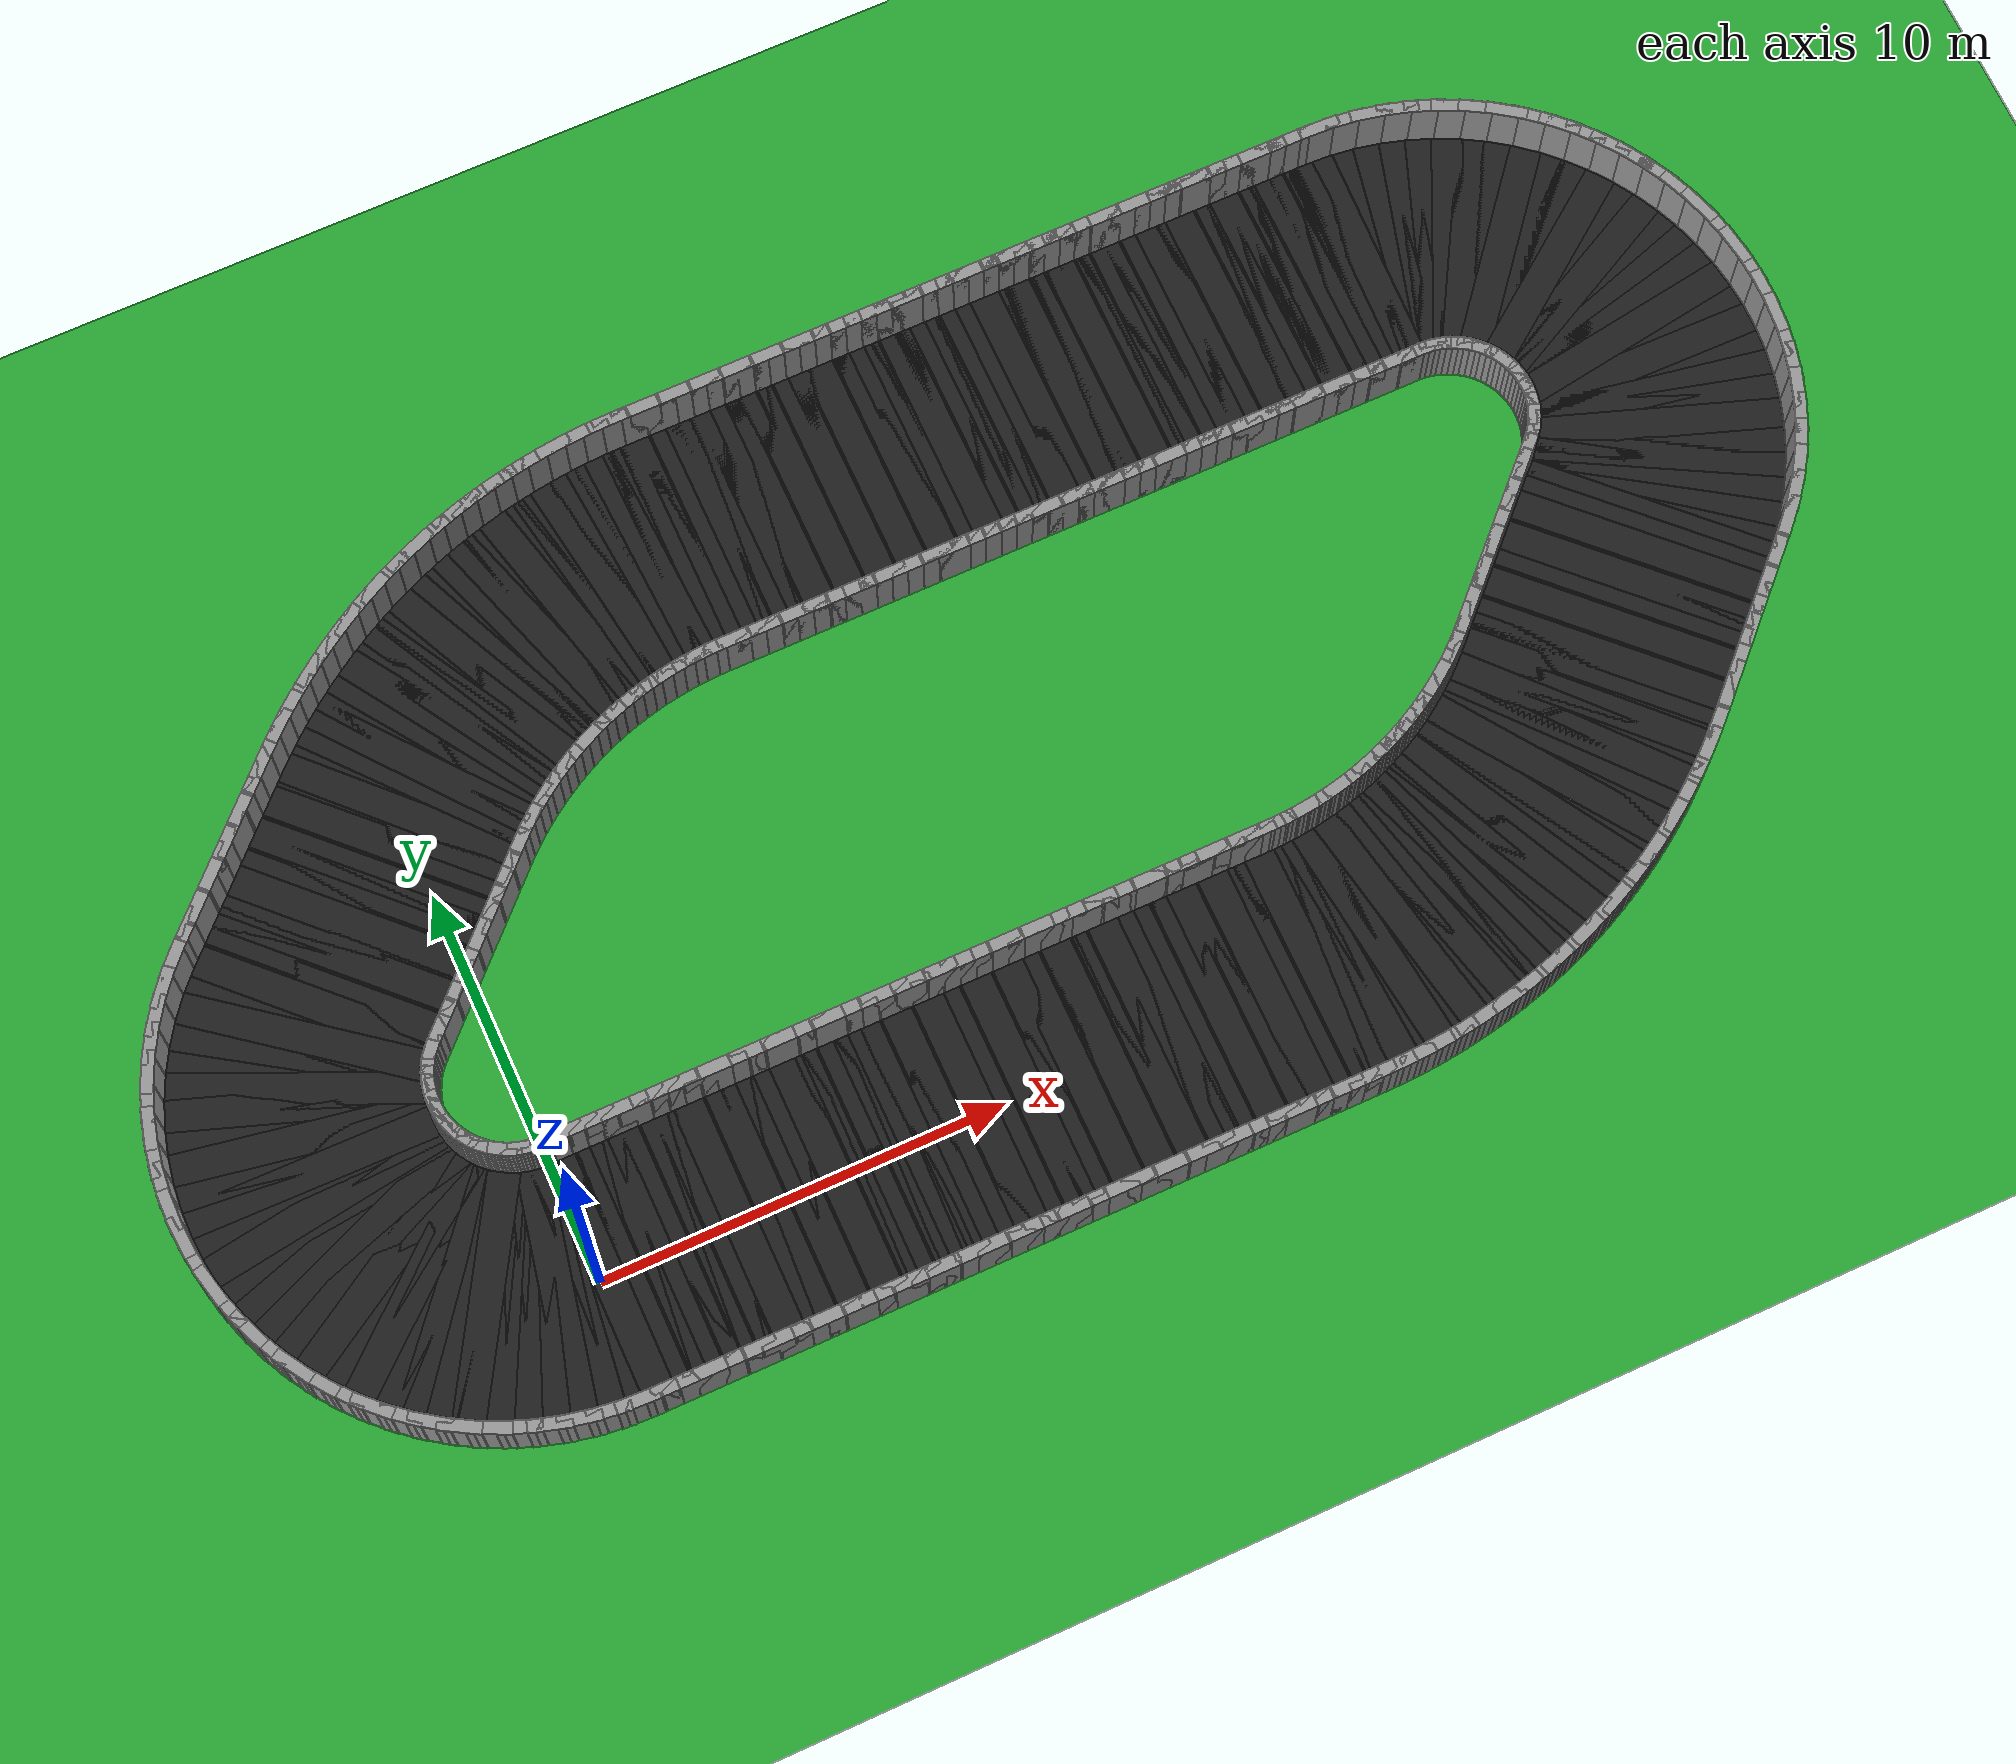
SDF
<?xml version="1.0" ?>
<sdf version="1.6">
  <world name="loop_road">
    <physics type="ode">
      <max_step_size>0.001</max_step_size>
      <real_time_factor>1.0</real_time_factor>
      <real_time_update_rate>1000</real_time_update_rate>
    </physics>
    <include><uri>model://sun</uri></include>

    <model name="ground_plane">
      <static>true</static>
      <link name="link">
        <collision name="collision">
          <surface><friction><ode><mu>100</mu><mu2>50</mu2></ode></friction></surface>
          <geometry><plane><normal>0 0 1</normal>
            <size>120 120</size></plane></geometry>
        </collision>
        <visual name="visual">
          <geometry><plane><normal>0 0 1</normal>
            <size>120 120</size></plane></geometry>
          <material><script>
            <uri>file://media/materials/scripts/gazebo.material</uri>
            <name>Gazebo/Green</name></script></material>
        </visual>
      </link>
    </model>

    <model name="asphalt_0">
      <static>true</static>
      <pose>0.200 0.000 0.005 0 0 0.00000</pose>
      <link name="link">
        <visual name="visual">
          <geometry><box><size>0.760 6.000 0.010</size></box></geometry>
          <material><script><uri>file://media/materials/scripts/gazebo.material</uri><name>Gazebo/Black</name></script></material>
        </visual>
      </link>
    </model>
    <model name="curbL_0">
      <static>true</static>
      <pose>0.200 3.150 0.750 0 0 0.00000</pose>
      <link name="link">
        <collision name="collision">
          <geometry><box><size>0.760 0.300 1.500</size></box></geometry>
        </collision>
        <visual name="visual">
          <geometry><box><size>0.760 0.300 1.500</size></box></geometry>
          <material><script><uri>file://media/materials/scripts/gazebo.material</uri><name>Gazebo/Grey</name></script></material>
        </visual>
      </link>
    </model>
    <model name="curbR_0">
      <static>true</static>
      <pose>0.200 -3.150 0.750 0 0 0.00000</pose>
      <link name="link">
        <collision name="collision">
          <geometry><box><size>0.760 0.300 1.500</size></box></geometry>
        </collision>
        <visual name="visual">
          <geometry><box><size>0.760 0.300 1.500</size></box></geometry>
          <material><script><uri>file://media/materials/scripts/gazebo.material</uri><name>Gazebo/Grey</name></script></material>
        </visual>
      </link>
    </model>
    <model name="asphalt_1">
      <static>true</static>
      <pose>0.600 0.000 0.005 0 0 0.00000</pose>
      <link name="link">
        <visual name="visual">
          <geometry><box><size>0.760 6.000 0.010</size></box></geometry>
          <material><script><uri>file://media/materials/scripts/gazebo.material</uri><name>Gazebo/Black</name></script></material>
        </visual>
      </link>
    </model>
    <model name="curbL_1">
      <static>true</static>
      <pose>0.600 3.150 0.750 0 0 0.00000</pose>
      <link name="link">
        <collision name="collision">
          <geometry><box><size>0.760 0.300 1.500</size></box></geometry>
        </collision>
        <visual name="visual">
          <geometry><box><size>0.760 0.300 1.500</size></box></geometry>
          <material><script><uri>file://media/materials/scripts/gazebo.material</uri><name>Gazebo/Grey</name></script></material>
        </visual>
      </link>
    </model>
    <model name="curbR_1">
      <static>true</static>
      <pose>0.600 -3.150 0.750 0 0 0.00000</pose>
      <link name="link">
        <collision name="collision">
          <geometry><box><size>0.760 0.300 1.500</size></box></geometry>
        </collision>
        <visual name="visual">
          <geometry><box><size>0.760 0.300 1.500</size></box></geometry>
          <material><script><uri>file://media/materials/scripts/gazebo.material</uri><name>Gazebo/Grey</name></script></material>
        </visual>
      </link>
    </model>
    <model name="asphalt_2">
      <static>true</static>
      <pose>1.000 0.000 0.005 0 0 0.00000</pose>
      <link name="link">
        <visual name="visual">
          <geometry><box><size>0.760 6.000 0.010</size></box></geometry>
          <material><script><uri>file://media/materials/scripts/gazebo.material</uri><name>Gazebo/Black</name></script></material>
        </visual>
      </link>
    </model>
    <model name="curbL_2">
      <static>true</static>
      <pose>1.000 3.150 0.750 0 0 0.00000</pose>
      <link name="link">
        <collision name="collision">
          <geometry><box><size>0.760 0.300 1.500</size></box></geometry>
        </collision>
        <visual name="visual">
          <geometry><box><size>0.760 0.300 1.500</size></box></geometry>
          <material><script><uri>file://media/materials/scripts/gazebo.material</uri><name>Gazebo/Grey</name></script></material>
        </visual>
      </link>
    </model>
    <model name="curbR_2">
      <static>true</static>
      <pose>1.000 -3.150 0.750 0 0 0.00000</pose>
      <link name="link">
        <collision name="collision">
          <geometry><box><size>0.760 0.300 1.500</size></box></geometry>
        </collision>
        <visual name="visual">
          <geometry><box><size>0.760 0.300 1.500</size></box></geometry>
          <material><script><uri>file://media/materials/scripts/gazebo.material</uri><name>Gazebo/Grey</name></script></material>
        </visual>
      </link>
    </model>
    <model name="asphalt_3">
      <static>true</static>
      <pose>1.400 0.000 0.005 0 0 0.00000</pose>
      <link name="link">
        <visual name="visual">
          <geometry><box><size>0.760 6.000 0.010</size></box></geometry>
          <material><script><uri>file://media/materials/scripts/gazebo.material</uri><name>Gazebo/Black</name></script></material>
        </visual>
      </link>
    </model>
    <model name="curbL_3">
      <static>true</static>
      <pose>1.400 3.150 0.750 0 0 0.00000</pose>
      <link name="link">
        <collision name="collision">
          <geometry><box><size>0.760 0.300 1.500</size></box></geometry>
        </collision>
        <visual name="visual">
          <geometry><box><size>0.760 0.300 1.500</size></box></geometry>
          <material><script><uri>file://media/materials/scripts/gazebo.material</uri><name>Gazebo/Grey</name></script></material>
        </visual>
      </link>
    </model>
    <model name="curbR_3">
      <static>true</static>
      <pose>1.400 -3.150 0.750 0 0 0.00000</pose>
      <link name="link">
        <collision name="collision">
          <geometry><box><size>0.760 0.300 1.500</size></box></geometry>
        </collision>
        <visual name="visual">
          <geometry><box><size>0.760 0.300 1.500</size></box></geometry>
          <material><script><uri>file://media/materials/scripts/gazebo.material</uri><name>Gazebo/Grey</name></script></material>
        </visual>
      </link>
    </model>
    <model name="asphalt_4">
      <static>true</static>
      <pose>1.800 0.000 0.005 0 0 0.00000</pose>
      <link name="link">
        <visual name="visual">
          <geometry><box><size>0.760 6.000 0.010</size></box></geometry>
          <material><script><uri>file://media/materials/scripts/gazebo.material</uri><name>Gazebo/Black</name></script></material>
        </visual>
      </link>
    </model>
    <model name="curbL_4">
      <static>true</static>
      <pose>1.800 3.150 0.750 0 0 0.00000</pose>
      <link name="link">
        <collision name="collision">
          <geometry><box><size>0.760 0.300 1.500</size></box></geometry>
        </collision>
        <visual name="visual">
          <geometry><box><size>0.760 0.300 1.500</size></box></geometry>
          <material><script><uri>file://media/materials/scripts/gazebo.material</uri><name>Gazebo/Grey</name></script></material>
        </visual>
      </link>
    </model>
    <model name="curbR_4">
      <static>true</static>
      <pose>1.800 -3.150 0.750 0 0 0.00000</pose>
      <link name="link">
        <collision name="collision">
          <geometry><box><size>0.760 0.300 1.500</size></box></geometry>
        </collision>
        <visual name="visual">
          <geometry><box><size>0.760 0.300 1.500</size></box></geometry>
          <material><script><uri>file://media/materials/scripts/gazebo.material</uri><name>Gazebo/Grey</name></script></material>
        </visual>
      </link>
    </model>
    <model name="asphalt_5">
      <static>true</static>
      <pose>2.200 0.000 0.005 0 0 0.00000</pose>
      <link name="link">
        <visual name="visual">
          <geometry><box><size>0.760 6.000 0.010</size></box></geometry>
          <material><script><uri>file://media/materials/scripts/gazebo.material</uri><name>Gazebo/Black</name></script></material>
        </visual>
      </link>
    </model>
    <model name="curbL_5">
      <static>true</static>
      <pose>2.200 3.150 0.750 0 0 0.00000</pose>
      <link name="link">
        <collision name="collision">
          <geometry><box><size>0.760 0.300 1.500</size></box></geometry>
        </collision>
        <visual name="visual">
          <geometry><box><size>0.760 0.300 1.500</size></box></geometry>
          <material><script><uri>file://media/materials/scripts/gazebo.material</uri><name>Gazebo/Grey</name></script></material>
        </visual>
      </link>
    </model>
    <model name="curbR_5">
      <static>true</static>
      <pose>2.200 -3.150 0.750 0 0 0.00000</pose>
      <link name="link">
        <collision name="collision">
          <geometry><box><size>0.760 0.300 1.500</size></box></geometry>
        </collision>
        <visual name="visual">
          <geometry><box><size>0.760 0.300 1.500</size></box></geometry>
          <material><script><uri>file://media/materials/scripts/gazebo.material</uri><name>Gazebo/Grey</name></script></material>
        </visual>
      </link>
    </model>
    <model name="asphalt_6">
      <static>true</static>
      <pose>2.600 0.000 0.005 0 0 0.00000</pose>
      <link name="link">
        <visual name="visual">
          <geometry><box><size>0.760 6.000 0.010</size></box></geometry>
          <material><script><uri>file://media/materials/scripts/gazebo.material</uri><name>Gazebo/Black</name></script></material>
        </visual>
      </link>
    </model>
    <model name="curbL_6">
      <static>true</static>
      <pose>2.600 3.150 0.750 0 0 0.00000</pose>
      <link name="link">
        <collision name="collision">
          <geometry><box><size>0.760 0.300 1.500</size></box></geometry>
        </collision>
        <visual name="visual">
          <geometry><box><size>0.760 0.300 1.500</size></box></geometry>
          <material><script><uri>file://media/materials/scripts/gazebo.material</uri><name>Gazebo/Grey</name></script></material>
        </visual>
      </link>
    </model>
    <model name="curbR_6">
      <static>true</static>
      <pose>2.600 -3.150 0.750 0 0 0.00000</pose>
      <link name="link">
        <collision name="collision">
          <geometry><box><size>0.760 0.300 1.500</size></box></geometry>
        </collision>
        <visual name="visual">
          <geometry><box><size>0.760 0.300 1.500</size></box></geometry>
          <material><script><uri>file://media/materials/scripts/gazebo.material</uri><name>Gazebo/Grey</name></script></material>
        </visual>
      </link>
    </model>
    <model name="asphalt_7">
      <static>true</static>
      <pose>3.000 0.000 0.005 0 0 0.00000</pose>
      <link name="link">
        <visual name="visual">
          <geometry><box><size>0.760 6.000 0.010</size></box></geometry>
          <material><script><uri>file://media/materials/scripts/gazebo.material</uri><name>Gazebo/Black</name></script></material>
        </visual>
      </link>
    </model>
    <model name="curbL_7">
      <static>true</static>
      <pose>3.000 3.150 0.750 0 0 0.00000</pose>
      <link name="link">
        <collision name="collision">
          <geometry><box><size>0.760 0.300 1.500</size></box></geometry>
        </collision>
        <visual name="visual">
          <geometry><box><size>0.760 0.300 1.500</size></box></geometry>
          <material><script><uri>file://media/materials/scripts/gazebo.material</uri><name>Gazebo/Grey</name></script></material>
        </visual>
      </link>
    </model>
    <model name="curbR_7">
      <static>true</static>
      <pose>3.000 -3.150 0.750 0 0 0.00000</pose>
      <link name="link">
        <collision name="collision">
          <geometry><box><size>0.760 0.300 1.500</size></box></geometry>
        </collision>
        <visual name="visual">
          <geometry><box><size>0.760 0.300 1.500</size></box></geometry>
          <material><script><uri>file://media/materials/scripts/gazebo.material</uri><name>Gazebo/Grey</name></script></material>
        </visual>
      </link>
    </model>
    <model name="asphalt_8">
      <static>true</static>
      <pose>3.400 0.000 0.005 0 0 0.00000</pose>
      <link name="link">
        <visual name="visual">
          <geometry><box><size>0.760 6.000 0.010</size></box></geometry>
          <material><script><uri>file://media/materials/scripts/gazebo.material</uri><name>Gazebo/Black</name></script></material>
        </visual>
      </link>
    </model>
    <model name="curbL_8">
      <static>true</static>
      <pose>3.400 3.150 0.750 0 0 0.00000</pose>
      <link name="link">
        <collision name="collision">
          <geometry><box><size>0.760 0.300 1.500</size></box></geometry>
        </collision>
        <visual name="visual">
          <geometry><box><size>0.760 0.300 1.500</size></box></geometry>
          <material><script><uri>file://media/materials/scripts/gazebo.material</uri><name>Gazebo/Grey</name></script></material>
        </visual>
      </link>
    </model>
    <model name="curbR_8">
      <static>true</static>
      <pose>3.400 -3.150 0.750 0 0 0.00000</pose>
      <link name="link">
        <collision name="collision">
          <geometry><box><size>0.760 0.300 1.500</size></box></geometry>
        </collision>
        <visual name="visual">
          <geometry><box><size>0.760 0.300 1.500</size></box></geometry>
          <material><script><uri>file://media/materials/scripts/gazebo.material</uri><name>Gazebo/Grey</name></script></material>
        </visual>
      </link>
    </model>
    <model name="asphalt_9">
      <static>true</static>
      <pose>3.800 0.000 0.005 0 0 0.00000</pose>
      <link name="link">
        <visual name="visual">
          <geometry><box><size>0.760 6.000 0.010</size></box></geometry>
          <material><script><uri>file://media/materials/scripts/gazebo.material</uri><name>Gazebo/Black</name></script></material>
        </visual>
      </link>
    </model>
    <model name="curbL_9">
      <static>true</static>
      <pose>3.800 3.150 0.750 0 0 0.00000</pose>
      <link name="link">
        <collision name="collision">
          <geometry><box><size>0.760 0.300 1.500</size></box></geometry>
        </collision>
        <visual name="visual">
          <geometry><box><size>0.760 0.300 1.500</size></box></geometry>
          <material><script><uri>file://media/materials/scripts/gazebo.material</uri><name>Gazebo/Grey</name></script></material>
        </visual>
      </link>
    </model>
    <model name="curbR_9">
      <static>true</static>
      <pose>3.800 -3.150 0.750 0 0 0.00000</pose>
      <link name="link">
        <collision name="collision">
          <geometry><box><size>0.760 0.300 1.500</size></box></geometry>
        </collision>
        <visual name="visual">
          <geometry><box><size>0.760 0.300 1.500</size></box></geometry>
          <material><script><uri>file://media/materials/scripts/gazebo.material</uri><name>Gazebo/Grey</name></script></material>
        </visual>
      </link>
    </model>
    <model name="asphalt_10">
      <static>true</static>
      <pose>4.200 0.000 0.005 0 0 0.00000</pose>
      <link name="link">
        <visual name="visual">
          <geometry><box><size>0.760 6.000 0.010</size></box></geometry>
          <material><script><uri>file://media/materials/scripts/gazebo.material</uri><name>Gazebo/Black</name></script></material>
        </visual>
      </link>
    </model>
    <model name="curbL_10">
      <static>true</static>
      <pose>4.200 3.150 0.750 0 0 0.00000</pose>
      <link name="link">
        <collision name="collision">
          <geometry><box><size>0.760 0.300 1.500</size></box></geometry>
        </collision>
        <visual name="visual">
          <geometry><box><size>0.760 0.300 1.500</size></box></geometry>
          <material><script><uri>file://media/materials/scripts/gazebo.material</uri><name>Gazebo/Grey</name></script></material>
        </visual>
      </link>
    </model>
    <model name="curbR_10">
      <static>true</static>
      <pose>4.200 -3.150 0.750 0 0 0.00000</pose>
      <link name="link">
        <collision name="collision">
          <geometry><box><size>0.760 0.300 1.500</size></box></geometry>
        </collision>
        <visual name="visual">
          <geometry><box><size>0.760 0.300 1.500</size></box></geometry>
          <material><script><uri>file://media/materials/scripts/gazebo.material</uri><name>Gazebo/Grey</name></script></material>
        </visual>
      </link>
    </model>
    <model name="asphalt_11">
      <static>true</static>
      <pose>4.600 0.000 0.005 0 0 0.00000</pose>
      <link name="link">
        <visual name="visual">
          <geometry><box><size>0.760 6.000 0.010</size></box></geometry>
          <material><script><uri>file://media/materials/scripts/gazebo.material</uri><name>Gazebo/Black</name></script></material>
        </visual>
      </link>
    </model>
    <model name="curbL_11">
      <static>true</static>
      <pose>4.600 3.150 0.750 0 0 0.00000</pose>
      <link name="link">
        <collision name="collision">
          <geometry><box><size>0.760 0.300 1.500</size></box></geometry>
        </collision>
        <visual name="visual">
          <geometry><box><size>0.760 0.300 1.500</size></box></geometry>
          <material><script><uri>file://media/materials/scripts/gazebo.material</uri><name>Gazebo/Grey</name></script></material>
        </visual>
      </link>
    </model>
    <model name="curbR_11">
      <static>true</static>
      <pose>4.600 -3.150 0.750 0 0 0.00000</pose>
      <link name="link">
        <collision name="collision">
          <geometry><box><size>0.760 0.300 1.500</size></box></geometry>
        </collision>
        <visual name="visual">
          <geometry><box><size>0.760 0.300 1.500</size></box></geometry>
          <material><script><uri>file://media/materials/scripts/gazebo.material</uri><name>Gazebo/Grey</name></script></material>
        </visual>
      </link>
    </model>
    <model name="asphalt_12">
      <static>true</static>
      <pose>5.000 0.000 0.005 0 0 0.00000</pose>
      <link name="link">
        <visual name="visual">
          <geometry><box><size>0.760 6.000 0.010</size></box></geometry>
          <material><script><uri>file://media/materials/scripts/gazebo.material</uri><name>Gazebo/Black</name></script></material>
        </visual>
      </link>
    </model>
    <model name="curbL_12">
      <static>true</static>
      <pose>5.000 3.150 0.750 0 0 0.00000</pose>
      <link name="link">
        <collision name="collision">
          <geometry><box><size>0.760 0.300 1.500</size></box></geometry>
        </collision>
        <visual name="visual">
          <geometry><box><size>0.760 0.300 1.500</size></box></geometry>
          <material><script><uri>file://media/materials/scripts/gazebo.material</uri><name>Gazebo/Grey</name></script></material>
        </visual>
      </link>
    </model>
    <model name="curbR_12">
      <static>true</static>
      <pose>5.000 -3.150 0.750 0 0 0.00000</pose>
      <link name="link">
        <collision name="collision">
          <geometry><box><size>0.760 0.300 1.500</size></box></geometry>
        </collision>
        <visual name="visual">
          <geometry><box><size>0.760 0.300 1.500</size></box></geometry>
          <material><script><uri>file://media/materials/scripts/gazebo.material</uri><name>Gazebo/Grey</name></script></material>
        </visual>
      </link>
    </model>
    <model name="asphalt_13">
      <static>true</static>
      <pose>5.400 0.000 0.005 0 0 0.00000</pose>
      <link name="link">
        <visual name="visual">
          <geometry><box><size>0.760 6.000 0.010</size></box></geometry>
          <material><script><uri>file://media/materials/scripts/gazebo.material</uri><name>Gazebo/Black</name></script></material>
        </visual>
      </link>
    </model>
    <model name="curbL_13">
      <static>true</static>
      <pose>5.400 3.150 0.750 0 0 0.00000</pose>
      <link name="link">
        <collision name="collision">
          <geometry><box><size>0.760 0.300 1.500</size></box></geometry>
        </collision>
        <visual name="visual">
          <geometry><box><size>0.760 0.300 1.500</size></box></geometry>
          <material><script><uri>file://media/materials/scripts/gazebo.material</uri><name>Gazebo/Grey</name></script></material>
        </visual>
      </link>
    </model>
    <model name="curbR_13">
      <static>true</static>
      <pose>5.400 -3.150 0.750 0 0 0.00000</pose>
      <link name="link">
        <collision name="collision">
          <geometry><box><size>0.760 0.300 1.500</size></box></geometry>
        </collision>
        <visual name="visual">
          <geometry><box><size>0.760 0.300 1.500</size></box></geometry>
          <material><script><uri>file://media/materials/scripts/gazebo.material</uri><name>Gazebo/Grey</name></script></material>
        </visual>
      </link>
    </model>
    <model name="asphalt_14">
      <static>true</static>
      <pose>5.800 0.000 0.005 0 0 0.00000</pose>
      <link name="link">
        <visual name="visual">
          <geometry><box><size>0.760 6.000 0.010</size></box></geometry>
          <material><script><uri>file://media/materials/scripts/gazebo.material</uri><name>Gazebo/Black</name></script></material>
        </visual>
      </link>
    </model>
    <model name="curbL_14">
      <static>true</static>
      <pose>5.800 3.150 0.750 0 0 0.00000</pose>
      <link name="link">
        <collision name="collision">
          <geometry><box><size>0.760 0.300 1.500</size></box></geometry>
        </collision>
        <visual name="visual">
          <geometry><box><size>0.760 0.300 1.500</size></box></geometry>
          <material><script><uri>file://media/materials/scripts/gazebo.material</uri><name>Gazebo/Grey</name></script></material>
        </visual>
      </link>
    </model>
    <model name="curbR_14">
      <static>true</static>
      <pose>5.800 -3.150 0.750 0 0 0.00000</pose>
      <link name="link">
        <collision name="collision">
          <geometry><box><size>0.760 0.300 1.500</size></box></geometry>
        </collision>
        <visual name="visual">
          <geometry><box><size>0.760 0.300 1.500</size></box></geometry>
          <material><script><uri>file://media/materials/scripts/gazebo.material</uri><name>Gazebo/Grey</name></script></material>
        </visual>
      </link>
    </model>
    <model name="asphalt_15">
      <static>true</static>
      <pose>6.200 0.000 0.005 0 0 0.00000</pose>
      <link name="link">
        <visual name="visual">
          <geometry><box><size>0.760 6.000 0.010</size></box></geometry>
          <material><script><uri>file://media/materials/scripts/gazebo.material</uri><name>Gazebo/Black</name></script></material>
        </visual>
      </link>
    </model>
    <model name="curbL_15">
      <static>true</static>
      <pose>6.200 3.150 0.750 0 0 0.00000</pose>
      <link name="link">
        <collision name="collision">
          <geometry><box><size>0.760 0.300 1.500</size></box></geometry>
        </collision>
        <visual name="visual">
          <geometry><box><size>0.760 0.300 1.500</size></box></geometry>
          <material><script><uri>file://media/materials/scripts/gazebo.material</uri><name>Gazebo/Grey</name></script></material>
        </visual>
      </link>
    </model>
    <model name="curbR_15">
      <static>true</static>
      <pose>6.200 -3.150 0.750 0 0 0.00000</pose>
      <link name="link">
        <collision name="collision">
          <geometry><box><size>0.760 0.300 1.500</size></box></geometry>
        </collision>
        <visual name="visual">
          <geometry><box><size>0.760 0.300 1.500</size></box></geometry>
          <material><script><uri>file://media/materials/scripts/gazebo.material</uri><name>Gazebo/Grey</name></script></material>
        </visual>
      </link>
    </model>
    <model name="asphalt_16">
      <static>true</static>
      <pose>6.600 0.000 0.005 0 0 0.00000</pose>
      <link name="link">
        <visual name="visual">
          <geometry><box><size>0.760 6.000 0.010</size></box></geometry>
          <material><script><uri>file://media/materials/scripts/gazebo.material</uri><name>Gazebo/Black</name></script></material>
        </visual>
      </link>
    </model>
    <model name="curbL_16">
      <static>true</static>
      <pose>6.600 3.150 0.750 0 0 0.00000</pose>
      <link name="link">
        <collision name="collision">
          <geometry><box><size>0.760 0.300 1.500</size></box></geometry>
        </collision>
        <visual name="visual">
          <geometry><box><size>0.760 0.300 1.500</size></box></geometry>
          <material><script><uri>file://media/materials/scripts/gazebo.material</uri><name>Gazebo/Grey</name></script></material>
        </visual>
      </link>
    </model>
    <model name="curbR_16">
      <static>true</static>
      <pose>6.600 -3.150 0.750 0 0 0.00000</pose>
      <link name="link">
        <collision name="collision">
          <geometry><box><size>0.760 0.300 1.500</size></box></geometry>
        </collision>
        <visual name="visual">
          <geometry><box><size>0.760 0.300 1.500</size></box></geometry>
          <material><script><uri>file://media/materials/scripts/gazebo.material</uri><name>Gazebo/Grey</name></script></material>
        </visual>
      </link>
    </model>
    <model name="asphalt_17">
      <static>true</static>
      <pose>7.000 0.000 0.005 0 0 0.00000</pose>
      <link name="link">
        <visual name="visual">
          <geometry><box><size>0.760 6.000 0.010</size></box></geometry>
          <material><script><uri>file://media/materials/scripts/gazebo.material</uri><name>Gazebo/Black</name></script></material>
        </visual>
      </link>
    </model>
    <model name="curbL_17">
      <static>true</static>
      <pose>7.000 3.150 0.750 0 0 0.00000</pose>
      <link name="link">
        <collision name="collision">
          <geometry><box><size>0.760 0.300 1.500</size></box></geometry>
        </collision>
        <visual name="visual">
          <geometry><box><size>0.760 0.300 1.500</size></box></geometry>
          <material><script><uri>file://media/materials/scripts/gazebo.material</uri><name>Gazebo/Grey</name></script></material>
        </visual>
      </link>
    </model>
    <model name="curbR_17">
      <static>true</static>
      <pose>7.000 -3.150 0.750 0 0 0.00000</pose>
      <link name="link">
        <collision name="collision">
          <geometry><box><size>0.760 0.300 1.500</size></box></geometry>
        </collision>
        <visual name="visual">
          <geometry><box><size>0.760 0.300 1.500</size></box></geometry>
          <material><script><uri>file://media/materials/scripts/gazebo.material</uri><name>Gazebo/Grey</name></script></material>
        </visual>
      </link>
    </model>
    <model name="asphalt_18">
      <static>true</static>
      <pose>7.400 0.000 0.005 0 0 0.00000</pose>
      <link name="link">
        <visual name="visual">
          <geometry><box><size>0.760 6.000 0.010</size></box></geometry>
          <material><script><uri>file://media/materials/scripts/gazebo.material</uri><name>Gazebo/Black</name></script></material>
        </visual>
      </link>
    </model>
    <model name="curbL_18">
      <static>true</static>
      <pose>7.400 3.150 0.750 0 0 0.00000</pose>
      <link name="link">
        <collision name="collision">
          <geometry><box><size>0.760 0.300 1.500</size></box></geometry>
        </collision>
        <visual name="visual">
          <geometry><box><size>0.760 0.300 1.500</size></box></geometry>
          <material><script><uri>file://media/materials/scripts/gazebo.material</uri><name>Gazebo/Grey</name></script></material>
        </visual>
      </link>
    </model>
    <model name="curbR_18">
      <static>true</static>
      <pose>7.400 -3.150 0.750 0 0 0.00000</pose>
      <link name="link">
        <collision name="collision">
          <geometry><box><size>0.760 0.300 1.500</size></box></geometry>
        </collision>
        <visual name="visual">
          <geometry><box><size>0.760 0.300 1.500</size></box></geometry>
          <material><script><uri>file://media/materials/scripts/gazebo.material</uri><name>Gazebo/Grey</name></script></material>
        </visual>
      </link>
    </model>
    <model name="asphalt_19">
      <static>true</static>
      <pose>7.800 0.000 0.005 0 0 0.00000</pose>
      <link name="link">
        <visual name="visual">
          <geometry><box><size>0.760 6.000 0.010</size></box></geometry>
          <material><script><uri>file://media/materials/scripts/gazebo.material</uri><name>Gazebo/Black</name></script></material>
        </visual>
      </link>
    </model>
    <model name="curbL_19">
      <static>true</static>
      <pose>7.800 3.150 0.750 0 0 0.00000</pose>
      <link name="link">
        <collision name="collision">
          <geometry><box><size>0.760 0.300 1.500</size></box></geometry>
        </collision>
        <visual name="visual">
          <geometry><box><size>0.760 0.300 1.500</size></box></geometry>
          <material><script><uri>file://media/materials/scripts/gazebo.material</uri><name>Gazebo/Grey</name></script></material>
        </visual>
      </link>
    </model>
    <model name="curbR_19">
      <static>true</static>
      <pose>7.800 -3.150 0.750 0 0 0.00000</pose>
      <link name="link">
        <collision name="collision">
          <geometry><box><size>0.760 0.300 1.500</size></box></geometry>
        </collision>
        <visual name="visual">
          <geometry><box><size>0.760 0.300 1.500</size></box></geometry>
          <material><script><uri>file://media/materials/scripts/gazebo.material</uri><name>Gazebo/Grey</name></script></material>
        </visual>
      </link>
    </model>
    <model name="asphalt_20">
      <static>true</static>
      <pose>8.200 0.000 0.005 0 0 0.00000</pose>
      <link name="link">
        <visual name="visual">
          <geometry><box><size>0.760 6.000 0.010</size></box></geometry>
          <material><script><uri>file://media/materials/scripts/gazebo.material</uri><name>Gazebo/Black</name></script></material>
        </visual>
      </link>
    </model>
    <model name="curbL_20">
      <static>true</static>
      <pose>8.200 3.150 0.750 0 0 0.00000</pose>
      <link name="link">
        <collision name="collision">
          <geometry><box><size>0.760 0.300 1.500</size></box></geometry>
        </collision>
        <visual name="visual">
          <geometry><box><size>0.760 0.300 1.500</size></box></geometry>
          <material><script><uri>file://media/materials/scripts/gazebo.material</uri><name>Gazebo/Grey</name></script></material>
        </visual>
      </link>
    </model>
    <model name="curbR_20">
      <static>true</static>
      <pose>8.200 -3.150 0.750 0 0 0.00000</pose>
      <link name="link">
        <collision name="collision">
          <geometry><box><size>0.760 0.300 1.500</size></box></geometry>
        </collision>
        <visual name="visual">
          <geometry><box><size>0.760 0.300 1.500</size></box></geometry>
          <material><script><uri>file://media/materials/scripts/gazebo.material</uri><name>Gazebo/Grey</name></script></material>
        </visual>
      </link>
    </model>
    <model name="asphalt_21">
      <static>true</static>
      <pose>8.600 0.000 0.005 0 0 0.00000</pose>
      <link name="link">
        <visual name="visual">
          <geometry><box><size>0.760 6.000 0.010</size></box></geometry>
          <material><script><uri>file://media/materials/scripts/gazebo.material</uri><name>Gazebo/Black</name></script></material>
        </visual>
      </link>
    </model>
    <model name="curbL_21">
      <static>true</static>
      <pose>8.600 3.150 0.750 0 0 0.00000</pose>
      <link name="link">
        <collision name="collision">
          <geometry><box><size>0.760 0.300 1.500</size></box></geometry>
        </collision>
        <visual name="visual">
          <geometry><box><size>0.760 0.300 1.500</size></box></geometry>
          <material><script><uri>file://media/materials/scripts/gazebo.material</uri><name>Gazebo/Grey</name></script></material>
        </visual>
      </link>
    </model>
    <model name="curbR_21">
      <static>true</static>
      <pose>8.600 -3.150 0.750 0 0 0.00000</pose>
      <link name="link">
        <collision name="collision">
          <geometry><box><size>0.760 0.300 1.500</size></box></geometry>
        </collision>
        <visual name="visual">
          <geometry><box><size>0.760 0.300 1.500</size></box></geometry>
          <material><script><uri>file://media/materials/scripts/gazebo.material</uri><name>Gazebo/Grey</name></script></material>
        </visual>
      </link>
    </model>
    <model name="asphalt_22">
      <static>true</static>
      <pose>9.000 0.000 0.005 0 0 0.00000</pose>
      <link name="link">
        <visual name="visual">
          <geometry><box><size>0.760 6.000 0.010</size></box></geometry>
          <material><script><uri>file://media/materials/scripts/gazebo.material</uri><name>Gazebo/Black</name></script></material>
        </visual>
      </link>
    </model>
    <model name="curbL_22">
      <static>true</static>
      <pose>9.000 3.150 0.750 0 0 0.00000</pose>
      <link name="link">
        <collision name="collision">
          <geometry><box><size>0.760 0.300 1.500</size></box></geometry>
        </collision>
        <visual name="visual">
          <geometry><box><size>0.760 0.300 1.500</size></box></geometry>
          <material><script><uri>file://media/materials/scripts/gazebo.material</uri><name>Gazebo/Grey</name></script></material>
        </visual>
      </link>
    </model>
    <model name="curbR_22">
      <static>true</static>
      <pose>9.000 -3.150 0.750 0 0 0.00000</pose>
      <link name="link">
        <collision name="collision">
          <geometry><box><size>0.760 0.300 1.500</size></box></geometry>
        </collision>
        <visual name="visual">
          <geometry><box><size>0.760 0.300 1.500</size></box></geometry>
          <material><script><uri>file://media/materials/scripts/gazebo.material</uri><name>Gazebo/Grey</name></script></material>
        </visual>
      </link>
    </model>
    <model name="asphalt_23">
      <static>true</static>
      <pose>9.400 0.000 0.005 0 0 0.00000</pose>
      <link name="link">
        <visual name="visual">
          <geometry><box><size>0.760 6.000 0.010</size></box></geometry>
          <material><script><uri>file://media/materials/scripts/gazebo.material</uri><name>Gazebo/Black</name></script></material>
        </visual>
      </link>
    </model>
    <model name="curbL_23">
      <static>true</static>
      <pose>9.400 3.150 0.750 0 0 0.00000</pose>
      <link name="link">
        <collision name="collision">
          <geometry><box><size>0.760 0.300 1.500</size></box></geometry>
        </collision>
        <visual name="visual">
          <geometry><box><size>0.760 0.300 1.500</size></box></geometry>
          <material><script><uri>file://media/materials/scripts/gazebo.material</uri><name>Gazebo/Grey</name></script></material>
        </visual>
      </link>
    </model>
    <model name="curbR_23">
      <static>true</static>
      <pose>9.400 -3.150 0.750 0 0 0.00000</pose>
      <link name="link">
        <collision name="collision">
          <geometry><box><size>0.760 0.300 1.500</size></box></geometry>
        </collision>
        <visual name="visual">
          <geometry><box><size>0.760 0.300 1.500</size></box></geometry>
          <material><script><uri>file://media/materials/scripts/gazebo.material</uri><name>Gazebo/Grey</name></script></material>
        </visual>
      </link>
    </model>
    <model name="asphalt_24">
      <static>true</static>
      <pose>9.800 0.000 0.005 0 0 0.00000</pose>
      <link name="link">
        <visual name="visual">
          <geometry><box><size>0.760 6.000 0.010</size></box></geometry>
          <material><script><uri>file://media/materials/scripts/gazebo.material</uri><name>Gazebo/Black</name></script></material>
        </visual>
      </link>
    </model>
    <model name="curbL_24">
      <static>true</static>
      <pose>9.800 3.150 0.750 0 0 0.00000</pose>
      <link name="link">
        <collision name="collision">
          <geometry><box><size>0.760 0.300 1.500</size></box></geometry>
        </collision>
        <visual name="visual">
          <geometry><box><size>0.760 0.300 1.500</size></box></geometry>
          <material><script><uri>file://media/materials/scripts/gazebo.material</uri><name>Gazebo/Grey</name></script></material>
        </visual>
      </link>
    </model>
    <model name="curbR_24">
      <static>true</static>
      <pose>9.800 -3.150 0.750 0 0 0.00000</pose>
      <link name="link">
        <collision name="collision">
          <geometry><box><size>0.760 0.300 1.500</size></box></geometry>
        </collision>
        <visual name="visual">
          <geometry><box><size>0.760 0.300 1.500</size></box></geometry>
          <material><script><uri>file://media/materials/scripts/gazebo.material</uri><name>Gazebo/Grey</name></script></material>
        </visual>
      </link>
    </model>
    <model name="asphalt_25">
      <static>true</static>
      <pose>10.200 0.000 0.005 0 0 0.00000</pose>
      <link name="link">
        <visual name="visual">
          <geometry><box><size>0.760 6.000 0.010</size></box></geometry>
          <material><script><uri>file://media/materials/scripts/gazebo.material</uri><name>Gazebo/Black</name></script></material>
        </visual>
      </link>
    </model>
    <model name="curbL_25">
      <static>true</static>
      <pose>10.200 3.150 0.750 0 0 0.00000</pose>
      <link name="link">
        <collision name="collision">
          <geometry><box><size>0.760 0.300 1.500</size></box></geometry>
        </collision>
        <visual name="visual">
          <geometry><box><size>0.760 0.300 1.500</size></box></geometry>
          <material><script><uri>file://media/materials/scripts/gazebo.material</uri><name>Gazebo/Grey</name></script></material>
        </visual>
      </link>
    </model>
    <model name="curbR_25">
      <static>true</static>
      <pose>10.200 -3.150 0.750 0 0 0.00000</pose>
      <link name="link">
        <collision name="collision">
          <geometry><box><size>0.760 0.300 1.500</size></box></geometry>
        </collision>
        <visual name="visual">
          <geometry><box><size>0.760 0.300 1.500</size></box></geometry>
          <material><script><uri>file://media/materials/scripts/gazebo.material</uri><name>Gazebo/Grey</name></script></material>
        </visual>
      </link>
    </model>
    <model name="asphalt_26">
      <static>true</static>
      <pose>10.600 0.000 0.005 0 0 0.00000</pose>
      <link name="link">
        <visual name="visual">
          <geometry><box><size>0.760 6.000 0.010</size></box></geometry>
          <material><script><uri>file://media/materials/scripts/gazebo.material</uri><name>Gazebo/Black</name></script></material>
        </visual>
      </link>
    </model>
    <model name="curbL_26">
      <static>true</static>
      <pose>10.600 3.150 0.750 0 0 0.00000</pose>
      <link name="link">
        <collision name="collision">
          <geometry><box><size>0.760 0.300 1.500</size></box></geometry>
        </collision>
        <visual name="visual">
          <geometry><box><size>0.760 0.300 1.500</size></box></geometry>
          <material><script><uri>file://media/materials/scripts/gazebo.material</uri><name>Gazebo/Grey</name></script></material>
        </visual>
      </link>
    </model>
    <model name="curbR_26">
      <static>true</static>
      <pose>10.600 -3.150 0.750 0 0 0.00000</pose>
      <link name="link">
        <collision name="collision">
          <geometry><box><size>0.760 0.300 1.500</size></box></geometry>
        </collision>
        <visual name="visual">
          <geometry><box><size>0.760 0.300 1.500</size></box></geometry>
          <material><script><uri>file://media/materials/scripts/gazebo.material</uri><name>Gazebo/Grey</name></script></material>
        </visual>
      </link>
    </model>
    <model name="asphalt_27">
      <static>true</static>
      <pose>11.000 0.000 0.005 0 0 0.00000</pose>
      <link name="link">
        <visual name="visual">
          <geometry><box><size>0.760 6.000 0.010</size></box></geometry>
          <material><script><uri>file://media/materials/scripts/gazebo.material</uri><name>Gazebo/Black</name></script></material>
        </visual>
      </link>
    </model>
    <model name="curbL_27">
      <static>true</static>
      <pose>11.000 3.150 0.750 0 0 0.00000</pose>
      <link name="link">
        <collision name="collision">
          <geometry><box><size>0.760 0.300 1.500</size></box></geometry>
        </collision>
        <visual name="visual">
          <geometry><box><size>0.760 0.300 1.500</size></box></geometry>
          <material><script><uri>file://media/materials/scripts/gazebo.material</uri><name>Gazebo/Grey</name></script></material>
        </visual>
      </link>
    </model>
    <model name="curbR_27">
      <static>true</static>
      <pose>11.000 -3.150 0.750 0 0 0.00000</pose>
      <link name="link">
        <collision name="collision">
          <geometry><box><size>0.760 0.300 1.500</size></box></geometry>
        </collision>
        <visual name="visual">
          <geometry><box><size>0.760 0.300 1.500</size></box></geometry>
          <material><script><uri>file://media/materials/scripts/gazebo.material</uri><name>Gazebo/Grey</name></script></material>
        </visual>
      </link>
    </model>
    <model name="asphalt_28">
      <static>true</static>
      <pose>11.400 0.000 0.005 0 0 0.00000</pose>
      <link name="link">
        <visual name="visual">
          <geometry><box><size>0.760 6.000 0.010</size></box></geometry>
          <material><script><uri>file://media/materials/scripts/gazebo.material</uri><name>Gazebo/Black</name></script></material>
        </visual>
      </link>
    </model>
    <model name="curbL_28">
      <static>true</static>
      <pose>11.400 3.150 0.750 0 0 0.00000</pose>
      <link name="link">
        <collision name="collision">
          <geometry><box><size>0.760 0.300 1.500</size></box></geometry>
        </collision>
        <visual name="visual">
          <geometry><box><size>0.760 0.300 1.500</size></box></geometry>
          <material><script><uri>file://media/materials/scripts/gazebo.material</uri><name>Gazebo/Grey</name></script></material>
        </visual>
      </link>
    </model>
    <model name="curbR_28">
      <static>true</static>
      <pose>11.400 -3.150 0.750 0 0 0.00000</pose>
      <link name="link">
        <collision name="collision">
          <geometry><box><size>0.760 0.300 1.500</size></box></geometry>
        </collision>
        <visual name="visual">
          <geometry><box><size>0.760 0.300 1.500</size></box></geometry>
          <material><script><uri>file://media/materials/scripts/gazebo.material</uri><name>Gazebo/Grey</name></script></material>
        </visual>
      </link>
    </model>
    <model name="asphalt_29">
      <static>true</static>
      <pose>11.800 0.000 0.005 0 0 0.00000</pose>
      <link name="link">
        <visual name="visual">
          <geometry><box><size>0.760 6.000 0.010</size></box></geometry>
          <material><script><uri>file://media/materials/scripts/gazebo.material</uri><name>Gazebo/Black</name></script></material>
        </visual>
      </link>
    </model>
    <model name="curbL_29">
      <static>true</static>
      <pose>11.800 3.150 0.750 0 0 0.00000</pose>
      <link name="link">
        <collision name="collision">
          <geometry><box><size>0.760 0.300 1.500</size></box></geometry>
        </collision>
        <visual name="visual">
          <geometry><box><size>0.760 0.300 1.500</size></box></geometry>
          <material><script><uri>file://media/materials/scripts/gazebo.material</uri><name>Gazebo/Grey</name></script></material>
        </visual>
      </link>
    </model>
    <model name="curbR_29">
      <static>true</static>
      <pose>11.800 -3.150 0.750 0 0 0.00000</pose>
      <link name="link">
        <collision name="collision">
          <geometry><box><size>0.760 0.300 1.500</size></box></geometry>
        </collision>
        <visual name="visual">
          <geometry><box><size>0.760 0.300 1.500</size></box></geometry>
          <material><script><uri>file://media/materials/scripts/gazebo.material</uri><name>Gazebo/Grey</name></script></material>
        </visual>
      </link>
    </model>
    <model name="asphalt_30">
      <static>true</static>
      <pose>12.200 0.000 0.005 0 0 0.00000</pose>
      <link name="link">
        <visual name="visual">
          <geometry><box><size>0.760 6.000 0.010</size></box></geometry>
          <material><script><uri>file://media/materials/scripts/gazebo.material</uri><name>Gazebo/Black</name></script></material>
        </visual>
      </link>
    </model>
    <model name="curbL_30">
      <static>true</static>
      <pose>12.200 3.150 0.750 0 0 0.00000</pose>
      <link name="link">
        <collision name="collision">
          <geometry><box><size>0.760 0.300 1.500</size></box></geometry>
        </collision>
        <visual name="visual">
          <geometry><box><size>0.760 0.300 1.500</size></box></geometry>
          <material><script><uri>file://media/materials/scripts/gazebo.material</uri><name>Gazebo/Grey</name></script></material>
        </visual>
      </link>
    </model>
    <model name="curbR_30">
      <static>true</static>
      <pose>12.200 -3.150 0.750 0 0 0.00000</pose>
      <link name="link">
        <collision name="collision">
          <geometry><box><size>0.760 0.300 1.500</size></box></geometry>
        </collision>
        <visual name="visual">
          <geometry><box><size>0.760 0.300 1.500</size></box></geometry>
          <material><script><uri>file://media/materials/scripts/gazebo.material</uri><name>Gazebo/Grey</name></script></material>
        </visual>
      </link>
    </model>
    <model name="asphalt_31">
      <static>true</static>
      <pose>12.600 0.000 0.005 0 0 0.00000</pose>
      <link name="link">
        <visual name="visual">
          <geometry><box><size>0.760 6.000 0.010</size></box></geometry>
          <material><script><uri>file://media/materials/scripts/gazebo.material</uri><name>Gazebo/Black</name></script></material>
        </visual>
      </link>
    </model>
    <model name="curbL_31">
      <static>true</static>
      <pose>12.600 3.150 0.750 0 0 0.00000</pose>
      <link name="link">
        <collision name="collision">
          <geometry><box><size>0.760 0.300 1.500</size></box></geometry>
        </collision>
        <visual name="visual">
          <geometry><box><size>0.760 0.300 1.500</size></box></geometry>
          <material><script><uri>file://media/materials/scripts/gazebo.material</uri><name>Gazebo/Grey</name></script></material>
        </visual>
      </link>
    </model>
    <model name="curbR_31">
      <static>true</static>
      <pose>12.600 -3.150 0.750 0 0 0.00000</pose>
      <link name="link">
        <collision name="collision">
          <geometry><box><size>0.760 0.300 1.500</size></box></geometry>
        </collision>
        <visual name="visual">
          <geometry><box><size>0.760 0.300 1.500</size></box></geometry>
          <material><script><uri>file://media/materials/scripts/gazebo.material</uri><name>Gazebo/Grey</name></script></material>
        </visual>
      </link>
    </model>
    <model name="asphalt_32">
      <static>true</static>
      <pose>13.000 0.000 0.005 0 0 0.00000</pose>
      <link name="link">
        <visual name="visual">
          <geometry><box><size>0.760 6.000 0.010</size></box></geometry>
          <material><script><uri>file://media/materials/scripts/gazebo.material</uri><name>Gazebo/Black</name></script></material>
        </visual>
      </link>
    </model>
    <model name="curbL_32">
      <static>true</static>
      <pose>13.000 3.150 0.750 0 0 0.00000</pose>
      <link name="link">
        <collision name="collision">
          <geometry><box><size>0.760 0.300 1.500</size></box></geometry>
        </collision>
        <visual name="visual">
          <geometry><box><size>0.760 0.300 1.500</size></box></geometry>
          <material><script><uri>file://media/materials/scripts/gazebo.material</uri><name>Gazebo/Grey</name></script></material>
        </visual>
      </link>
    </model>
    <model name="curbR_32">
      <static>true</static>
      <pose>13.000 -3.150 0.750 0 0 0.00000</pose>
      <link name="link">
        <collision name="collision">
          <geometry><box><size>0.760 0.300 1.500</size></box></geometry>
        </collision>
        <visual name="visual">
          <geometry><box><size>0.760 0.300 1.500</size></box></geometry>
          <material><script><uri>file://media/materials/scripts/gazebo.material</uri><name>Gazebo/Grey</name></script></material>
        </visual>
      </link>
    </model>
    <model name="asphalt_33">
      <static>true</static>
      <pose>13.400 0.000 0.005 0 0 0.00000</pose>
      <link name="link">
        <visual name="visual">
          <geometry><box><size>0.760 6.000 0.010</size></box></geometry>
          <material><script><uri>file://media/materials/scripts/gazebo.material</uri><name>Gazebo/Black</name></script></material>
        </visual>
      </link>
    </model>
    <model name="curbL_33">
      <static>true</static>
      <pose>13.400 3.150 0.750 0 0 0.00000</pose>
      <link name="link">
        <collision name="collision">
          <geometry><box><size>0.760 0.300 1.500</size></box></geometry>
        </collision>
        <visual name="visual">
          <geometry><box><size>0.760 0.300 1.500</size></box></geometry>
          <material><script><uri>file://media/materials/scripts/gazebo.material</uri><name>Gazebo/Grey</name></script></material>
        </visual>
      </link>
    </model>
    <model name="curbR_33">
      <static>true</static>
      <pose>13.400 -3.150 0.750 0 0 0.00000</pose>
      <link name="link">
        <collision name="collision">
          <geometry><box><size>0.760 0.300 1.500</size></box></geometry>
        </collision>
        <visual name="visual">
          <geometry><box><size>0.760 0.300 1.500</size></box></geometry>
          <material><script><uri>file://media/materials/scripts/gazebo.material</uri><name>Gazebo/Grey</name></script></material>
        </visual>
      </link>
    </model>
    <model name="asphalt_34">
      <static>true</static>
      <pose>13.800 0.000 0.005 0 0 0.00000</pose>
      <link name="link">
        <visual name="visual">
          <geometry><box><size>0.760 6.000 0.010</size></box></geometry>
          <material><script><uri>file://media/materials/scripts/gazebo.material</uri><name>Gazebo/Black</name></script></material>
        </visual>
      </link>
    </model>
    <model name="curbL_34">
      <static>true</static>
      <pose>13.800 3.150 0.750 0 0 0.00000</pose>
      <link name="link">
        <collision name="collision">
          <geometry><box><size>0.760 0.300 1.500</size></box></geometry>
        </collision>
        <visual name="visual">
          <geometry><box><size>0.760 0.300 1.500</size></box></geometry>
          <material><script><uri>file://media/materials/scripts/gazebo.material</uri><name>Gazebo/Grey</name></script></material>
        </visual>
      </link>
    </model>
    <model name="curbR_34">
      <static>true</static>
      <pose>13.800 -3.150 0.750 0 0 0.00000</pose>
      <link name="link">
        <collision name="collision">
          <geometry><box><size>0.760 0.300 1.500</size></box></geometry>
        </collision>
        <visual name="visual">
          <geometry><box><size>0.760 0.300 1.500</size></box></geometry>
          <material><script><uri>file://media/materials/scripts/gazebo.material</uri><name>Gazebo/Grey</name></script></material>
        </visual>
      </link>
    </model>
    <model name="asphalt_35">
      <static>true</static>
      <pose>14.200 0.000 0.005 0 0 0.00000</pose>
      <link name="link">
        <visual name="visual">
          <geometry><box><size>0.760 6.000 0.010</size></box></geometry>
          <material><script><uri>file://media/materials/scripts/gazebo.material</uri><name>Gazebo/Black</name></script></material>
        </visual>
      </link>
    </model>
    <model name="curbL_35">
      <static>true</static>
      <pose>14.200 3.150 0.750 0 0 0.00000</pose>
      <link name="link">
        <collision name="collision">
          <geometry><box><size>0.760 0.300 1.500</size></box></geometry>
        </collision>
        <visual name="visual">
          <geometry><box><size>0.760 0.300 1.500</size></box></geometry>
          <material><script><uri>file://media/materials/scripts/gazebo.material</uri><name>Gazebo/Grey</name></script></material>
        </visual>
      </link>
    </model>
    <model name="curbR_35">
      <static>true</static>
      <pose>14.200 -3.150 0.750 0 0 0.00000</pose>
      <link name="link">
        <collision name="collision">
          <geometry><box><size>0.760 0.300 1.500</size></box></geometry>
        </collision>
        <visual name="visual">
          <geometry><box><size>0.760 0.300 1.500</size></box></geometry>
          <material><script><uri>file://media/materials/scripts/gazebo.material</uri><name>Gazebo/Grey</name></script></material>
        </visual>
      </link>
    </model>
    <model name="asphalt_36">
      <static>true</static>
      <pose>14.600 0.000 0.005 0 0 0.00000</pose>
      <link name="link">
        <visual name="visual">
          <geometry><box><size>0.760 6.000 0.010</size></box></geometry>
          <material><script><uri>file://media/materials/scripts/gazebo.material</uri><name>Gazebo/Black</name></script></material>
        </visual>
      </link>
    </model>
    <model name="curbL_36">
      <static>true</static>
      <pose>14.600 3.150 0.750 0 0 0.00000</pose>
      <link name="link">
        <collision name="collision">
          <geometry><box><size>0.760 0.300 1.500</size></box></geometry>
        </collision>
        <visual name="visual">
          <geometry><box><size>0.760 0.300 1.500</size></box></geometry>
          <material><script><uri>file://media/materials/scripts/gazebo.material</uri><name>Gazebo/Grey</name></script></material>
        </visual>
      </link>
    </model>
    <model name="curbR_36">
      <static>true</static>
      <pose>14.600 -3.150 0.750 0 0 0.00000</pose>
      <link name="link">
        <collision name="collision">
          <geometry><box><size>0.760 0.300 1.500</size></box></geometry>
        </collision>
        <visual name="visual">
          <geometry><box><size>0.760 0.300 1.500</size></box></geometry>
          <material><script><uri>file://media/materials/scripts/gazebo.material</uri><name>Gazebo/Grey</name></script></material>
        </visual>
      </link>
    </model>
    <model name="asphalt_37">
      <static>true</static>
      <pose>15.000 0.000 0.005 0 0 0.00000</pose>
      <link name="link">
        <visual name="visual">
          <geometry><box><size>0.760 6.000 0.010</size></box></geometry>
          <material><script><uri>file://media/materials/scripts/gazebo.material</uri><name>Gazebo/Black</name></script></material>
        </visual>
      </link>
    </model>
    <model name="curbL_37">
      <static>true</static>
      <pose>15.000 3.150 0.750 0 0 0.00000</pose>
      <link name="link">
        <collision name="collision">
          <geometry><box><size>0.760 0.300 1.500</size></box></geometry>
        </collision>
        <visual name="visual">
          <geometry><box><size>0.760 0.300 1.500</size></box></geometry>
          <material><script><uri>file://media/materials/scripts/gazebo.material</uri><name>Gazebo/Grey</name></script></material>
        </visual>
      </link>
    </model>
    <model name="curbR_37">
      <static>true</static>
      <pose>15.000 -3.150 0.750 0 0 0.00000</pose>
      <link name="link">
        <collision name="collision">
          <geometry><box><size>0.760 0.300 1.500</size></box></geometry>
        </collision>
        <visual name="visual">
          <geometry><box><size>0.760 0.300 1.500</size></box></geometry>
          <material><script><uri>file://media/materials/scripts/gazebo.material</uri><name>Gazebo/Grey</name></script></material>
        </visual>
      </link>
    </model>
    <model name="asphalt_38">
      <static>true</static>
      <pose>15.400 0.000 0.005 0 0 0.00000</pose>
      <link name="link">
        <visual name="visual">
          <geometry><box><size>0.760 6.000 0.010</size></box></geometry>
          <material><script><uri>file://media/materials/scripts/gazebo.material</uri><name>Gazebo/Black</name></script></material>
        </visual>
      </link>
    </model>
    <model name="curbL_38">
      <static>true</static>
      <pose>15.400 3.150 0.750 0 0 0.00000</pose>
      <link name="link">
        <collision name="collision">
          <geometry><box><size>0.760 0.300 1.500</size></box></geometry>
        </collision>
        <visual name="visual">
          <geometry><box><size>0.760 0.300 1.500</size></box></geometry>
          <material><script><uri>file://media/materials/scripts/gazebo.material</uri><name>Gazebo/Grey</name></script></material>
        </visual>
      </link>
    </model>
    <model name="curbR_38">
      <static>true</static>
      <pose>15.400 -3.150 0.750 0 0 0.00000</pose>
      <link name="link">
        <collision name="collision">
          <geometry><box><size>0.760 0.300 1.500</size></box></geometry>
        </collision>
        <visual name="visual">
          <geometry><box><size>0.760 0.300 1.500</size></box></geometry>
          <material><script><uri>file://media/materials/scripts/gazebo.material</uri><name>Gazebo/Grey</name></script></material>
        </visual>
      </link>
    </model>
    <model name="asphalt_39">
      <static>true</static>
      <pose>15.800 0.000 0.005 0 0 0.00000</pose>
      <link name="link">
        <visual name="visual">
          <geometry><box><size>0.760 6.000 0.010</size></box></geometry>
          <material><script><uri>file://media/materials/scripts/gazebo.material</uri><name>Gazebo/Black</name></script></material>
        </visual>
      </link>
    </model>
    <model name="curbL_39">
      <static>true</static>
      <pose>15.800 3.150 0.750 0 0 0.00000</pose>
      <link name="link">
        <collision name="collision">
          <geometry><box><size>0.760 0.300 1.500</size></box></geometry>
        </collision>
        <visual name="visual">
          <geometry><box><size>0.760 0.300 1.500</size></box></geometry>
          <material><script><uri>file://media/materials/scripts/gazebo.material</uri><name>Gazebo/Grey</name></script></material>
        </visual>
      </link>
    </model>
    <model name="curbR_39">
      <static>true</static>
      <pose>15.800 -3.150 0.750 0 0 0.00000</pose>
      <link name="link">
        <collision name="collision">
          <geometry><box><size>0.760 0.300 1.500</size></box></geometry>
        </collision>
        <visual name="visual">
          <geometry><box><size>0.760 0.300 1.500</size></box></geometry>
          <material><script><uri>file://media/materials/scripts/gazebo.material</uri><name>Gazebo/Grey</name></script></material>
        </visual>
      </link>
    </model>
    <model name="asphalt_40">
      <static>true</static>
      <pose>16.200 0.000 0.005 0 0 0.00000</pose>
      <link name="link">
        <visual name="visual">
          <geometry><box><size>0.760 6.000 0.010</size></box></geometry>
          <material><script><uri>file://media/materials/scripts/gazebo.material</uri><name>Gazebo/Black</name></script></material>
        </visual>
      </link>
    </model>
    <model name="curbL_40">
      <static>true</static>
      <pose>16.200 3.150 0.750 0 0 0.00000</pose>
      <link name="link">
        <collision name="collision">
          <geometry><box><size>0.760 0.300 1.500</size></box></geometry>
        </collision>
        <visual name="visual">
          <geometry><box><size>0.760 0.300 1.500</size></box></geometry>
          <material><script><uri>file://media/materials/scripts/gazebo.material</uri><name>Gazebo/Grey</name></script></material>
        </visual>
      </link>
    </model>
    <model name="curbR_40">
      <static>true</static>
      <pose>16.200 -3.150 0.750 0 0 0.00000</pose>
      <link name="link">
        <collision name="collision">
          <geometry><box><size>0.760 0.300 1.500</size></box></geometry>
        </collision>
        <visual name="visual">
          <geometry><box><size>0.760 0.300 1.500</size></box></geometry>
          <material><script><uri>file://media/materials/scripts/gazebo.material</uri><name>Gazebo/Grey</name></script></material>
        </visual>
      </link>
    </model>
    <model name="asphalt_41">
      <static>true</static>
      <pose>16.600 0.000 0.005 0 0 0.00000</pose>
      <link name="link">
        <visual name="visual">
          <geometry><box><size>0.760 6.000 0.010</size></box></geometry>
          <material><script><uri>file://media/materials/scripts/gazebo.material</uri><name>Gazebo/Black</name></script></material>
        </visual>
      </link>
    </model>
    <model name="curbL_41">
      <static>true</static>
      <pose>16.600 3.150 0.750 0 0 0.00000</pose>
      <link name="link">
        <collision name="collision">
          <geometry><box><size>0.760 0.300 1.500</size></box></geometry>
        </collision>
        <visual name="visual">
          <geometry><box><size>0.760 0.300 1.500</size></box></geometry>
          <material><script><uri>file://media/materials/scripts/gazebo.material</uri><name>Gazebo/Grey</name></script></material>
        </visual>
      </link>
    </model>
    <model name="curbR_41">
      <static>true</static>
      <pose>16.600 -3.150 0.750 0 0 0.00000</pose>
      <link name="link">
        <collision name="collision">
          <geometry><box><size>0.760 0.300 1.500</size></box></geometry>
        </collision>
        <visual name="visual">
          <geometry><box><size>0.760 0.300 1.500</size></box></geometry>
          <material><script><uri>file://media/materials/scripts/gazebo.material</uri><name>Gazebo/Grey</name></script></material>
        </visual>
      </link>
    </model>
    <model name="asphalt_42">
      <static>true</static>
      <pose>17.000 0.000 0.005 0 0 0.00000</pose>
      <link name="link">
        <visual name="visual">
          <geometry><box><size>0.760 6.000 0.010</size></box></geometry>
          <material><script><uri>file://media/materials/scripts/gazebo.material</uri><name>Gazebo/Black</name></script></material>
        </visual>
      </link>
    </model>
    <model name="curbL_42">
      <static>true</static>
      <pose>17.000 3.150 0.750 0 0 0.00000</pose>
      <link name="link">
        <collision name="collision">
          <geometry><box><size>0.760 0.300 1.500</size></box></geometry>
        </collision>
        <visual name="visual">
          <geometry><box><size>0.760 0.300 1.500</size></box></geometry>
          <material><script><uri>file://media/materials/scripts/gazebo.material</uri><name>Gazebo/Grey</name></script></material>
        </visual>
      </link>
    </model>
    <model name="curbR_42">
      <static>true</static>
      <pose>17.000 -3.150 0.750 0 0 0.00000</pose>
      <link name="link">
        <collision name="collision">
          <geometry><box><size>0.760 0.300 1.500</size></box></geometry>
        </collision>
        <visual name="visual">
          <geometry><box><size>0.760 0.300 1.500</size></box></geometry>
          <material><script><uri>file://media/materials/scripts/gazebo.material</uri><name>Gazebo/Grey</name></script></material>
        </visual>
      </link>
    </model>
    <model name="asphalt_43">
      <static>true</static>
      <pose>17.400 0.000 0.005 0 0 0.00000</pose>
      <link name="link">
        <visual name="visual">
          <geometry><box><size>0.760 6.000 0.010</size></box></geometry>
          <material><script><uri>file://media/materials/scripts/gazebo.material</uri><name>Gazebo/Black</name></script></material>
        </visual>
      </link>
    </model>
    <model name="curbL_43">
      <static>true</static>
      <pose>17.400 3.150 0.750 0 0 0.00000</pose>
      <link name="link">
        <collision name="collision">
          <geometry><box><size>0.760 0.300 1.500</size></box></geometry>
        </collision>
        <visual name="visual">
          <geometry><box><size>0.760 0.300 1.500</size></box></geometry>
          <material><script><uri>file://media/materials/scripts/gazebo.material</uri><name>Gazebo/Grey</name></script></material>
        </visual>
      </link>
    </model>
    <model name="curbR_43">
      <static>true</static>
      <pose>17.400 -3.150 0.750 0 0 0.00000</pose>
      <link name="link">
        <collision name="collision">
          <geometry><box><size>0.760 0.300 1.500</size></box></geometry>
        </collision>
        <visual name="visual">
          <geometry><box><size>0.760 0.300 1.500</size></box></geometry>
          <material><script><uri>file://media/materials/scripts/gazebo.material</uri><name>Gazebo/Grey</name></script></material>
        </visual>
      </link>
    </model>
    <model name="asphalt_44">
      <static>true</static>
      <pose>17.800 0.000 0.005 0 0 0.00000</pose>
      <link name="link">
        <visual name="visual">
          <geometry><box><size>0.760 6.000 0.010</size></box></geometry>
          <material><script><uri>file://media/materials/scripts/gazebo.material</uri><name>Gazebo/Black</name></script></material>
        </visual>
      </link>
    </model>
    <model name="curbL_44">
      <static>true</static>
      <pose>17.800 3.150 0.750 0 0 0.00000</pose>
      <link name="link">
        <collision name="collision">
          <geometry><box><size>0.760 0.300 1.500</size></box></geometry>
        </collision>
        <visual name="visual">
          <geometry><box><size>0.760 0.300 1.500</size></box></geometry>
          <material><script><uri>file://media/materials/scripts/gazebo.material</uri><name>Gazebo/Grey</name></script></material>
        </visual>
      </link>
    </model>
    <model name="curbR_44">
      <static>true</static>
      <pose>17.800 -3.150 0.750 0 0 0.00000</pose>
      <link name="link">
        <collision name="collision">
          <geometry><box><size>0.760 0.300 1.500</size></box></geometry>
        </collision>
        <visual name="visual">
          <geometry><box><size>0.760 0.300 1.500</size></box></geometry>
          <material><script><uri>file://media/materials/scripts/gazebo.material</uri><name>Gazebo/Grey</name></script></material>
        </visual>
      </link>
    </model>
    <model name="asphalt_45">
      <static>true</static>
      <pose>18.196 0.003 0.005 0 0 0.01636</pose>
      <link name="link">
        <visual name="visual">
          <geometry><box><size>0.753 6.000 0.010</size></box></geometry>
          <material><script><uri>file://media/materials/scripts/gazebo.material</uri><name>Gazebo/Black</name></script></material>
        </visual>
      </link>
    </model>
    <model name="curbL_45">
      <static>true</static>
      <pose>18.145 3.152 0.750 0 0 0.01636</pose>
      <link name="link">
        <collision name="collision">
          <geometry><box><size>0.650 0.300 1.500</size></box></geometry>
        </collision>
        <visual name="visual">
          <geometry><box><size>0.650 0.300 1.500</size></box></geometry>
          <material><script><uri>file://media/materials/scripts/gazebo.material</uri><name>Gazebo/Grey</name></script></material>
        </visual>
      </link>
    </model>
    <model name="curbR_45">
      <static>true</static>
      <pose>18.248 -3.146 0.750 0 0 0.01636</pose>
      <link name="link">
        <collision name="collision">
          <geometry><box><size>0.856 0.300 1.500</size></box></geometry>
        </collision>
        <visual name="visual">
          <geometry><box><size>0.856 0.300 1.500</size></box></geometry>
          <material><script><uri>file://media/materials/scripts/gazebo.material</uri><name>Gazebo/Grey</name></script></material>
        </visual>
      </link>
    </model>
    <model name="asphalt_46">
      <static>true</static>
      <pose>18.589 0.016 0.005 0 0 0.04909</pose>
      <link name="link">
        <visual name="visual">
          <geometry><box><size>0.753 6.000 0.010</size></box></geometry>
          <material><script><uri>file://media/materials/scripts/gazebo.material</uri><name>Gazebo/Black</name></script></material>
        </visual>
      </link>
    </model>
    <model name="curbL_46">
      <static>true</static>
      <pose>18.434 3.162 0.750 0 0 0.04909</pose>
      <link name="link">
        <collision name="collision">
          <geometry><box><size>0.650 0.300 1.500</size></box></geometry>
        </collision>
        <visual name="visual">
          <geometry><box><size>0.650 0.300 1.500</size></box></geometry>
          <material><script><uri>file://media/materials/scripts/gazebo.material</uri><name>Gazebo/Grey</name></script></material>
        </visual>
      </link>
    </model>
    <model name="curbR_46">
      <static>true</static>
      <pose>18.743 -3.130 0.750 0 0 0.04909</pose>
      <link name="link">
        <collision name="collision">
          <geometry><box><size>0.856 0.300 1.500</size></box></geometry>
        </collision>
        <visual name="visual">
          <geometry><box><size>0.856 0.300 1.500</size></box></geometry>
          <material><script><uri>file://media/materials/scripts/gazebo.material</uri><name>Gazebo/Grey</name></script></material>
        </visual>
      </link>
    </model>
    <model name="asphalt_47">
      <static>true</static>
      <pose>18.981 0.042 0.005 0 0 0.08181</pose>
      <link name="link">
        <visual name="visual">
          <geometry><box><size>0.753 6.000 0.010</size></box></geometry>
          <material><script><uri>file://media/materials/scripts/gazebo.material</uri><name>Gazebo/Black</name></script></material>
        </visual>
      </link>
    </model>
    <model name="curbL_47">
      <static>true</static>
      <pose>18.723 3.181 0.750 0 0 0.08181</pose>
      <link name="link">
        <collision name="collision">
          <geometry><box><size>0.650 0.300 1.500</size></box></geometry>
        </collision>
        <visual name="visual">
          <geometry><box><size>0.650 0.300 1.500</size></box></geometry>
          <material><script><uri>file://media/materials/scripts/gazebo.material</uri><name>Gazebo/Grey</name></script></material>
        </visual>
      </link>
    </model>
    <model name="curbR_47">
      <static>true</static>
      <pose>19.238 -3.097 0.750 0 0 0.08181</pose>
      <link name="link">
        <collision name="collision">
          <geometry><box><size>0.856 0.300 1.500</size></box></geometry>
        </collision>
        <visual name="visual">
          <geometry><box><size>0.856 0.300 1.500</size></box></geometry>
          <material><script><uri>file://media/materials/scripts/gazebo.material</uri><name>Gazebo/Grey</name></script></material>
        </visual>
      </link>
    </model>
    <model name="asphalt_48">
      <static>true</static>
      <pose>19.371 0.080 0.005 0 0 0.11454</pose>
      <link name="link">
        <visual name="visual">
          <geometry><box><size>0.753 6.000 0.010</size></box></geometry>
          <material><script><uri>file://media/materials/scripts/gazebo.material</uri><name>Gazebo/Black</name></script></material>
        </visual>
      </link>
    </model>
    <model name="curbL_48">
      <static>true</static>
      <pose>19.011 3.209 0.750 0 0 0.11454</pose>
      <link name="link">
        <collision name="collision">
          <geometry><box><size>0.650 0.300 1.500</size></box></geometry>
        </collision>
        <visual name="visual">
          <geometry><box><size>0.650 0.300 1.500</size></box></geometry>
          <material><script><uri>file://media/materials/scripts/gazebo.material</uri><name>Gazebo/Grey</name></script></material>
        </visual>
      </link>
    </model>
    <model name="curbR_48">
      <static>true</static>
      <pose>19.731 -3.049 0.750 0 0 0.11454</pose>
      <link name="link">
        <collision name="collision">
          <geometry><box><size>0.856 0.300 1.500</size></box></geometry>
        </collision>
        <visual name="visual">
          <geometry><box><size>0.856 0.300 1.500</size></box></geometry>
          <material><script><uri>file://media/materials/scripts/gazebo.material</uri><name>Gazebo/Grey</name></script></material>
        </visual>
      </link>
    </model>
    <model name="asphalt_49">
      <static>true</static>
      <pose>19.761 0.131 0.005 0 0 0.14726</pose>
      <link name="link">
        <visual name="visual">
          <geometry><box><size>0.753 6.000 0.010</size></box></geometry>
          <material><script><uri>file://media/materials/scripts/gazebo.material</uri><name>Gazebo/Black</name></script></material>
        </visual>
      </link>
    </model>
    <model name="curbL_49">
      <static>true</static>
      <pose>19.298 3.247 0.750 0 0 0.14726</pose>
      <link name="link">
        <collision name="collision">
          <geometry><box><size>0.650 0.300 1.500</size></box></geometry>
        </collision>
        <visual name="visual">
          <geometry><box><size>0.650 0.300 1.500</size></box></geometry>
          <material><script><uri>file://media/materials/scripts/gazebo.material</uri><name>Gazebo/Grey</name></script></material>
        </visual>
      </link>
    </model>
    <model name="curbR_49">
      <static>true</static>
      <pose>20.223 -2.984 0.750 0 0 0.14726</pose>
      <link name="link">
        <collision name="collision">
          <geometry><box><size>0.856 0.300 1.500</size></box></geometry>
        </collision>
        <visual name="visual">
          <geometry><box><size>0.856 0.300 1.500</size></box></geometry>
          <material><script><uri>file://media/materials/scripts/gazebo.material</uri><name>Gazebo/Grey</name></script></material>
        </visual>
      </link>
    </model>
    <model name="asphalt_50">
      <static>true</static>
      <pose>20.148 0.195 0.005 0 0 0.17999</pose>
      <link name="link">
        <visual name="visual">
          <geometry><box><size>0.753 6.000 0.010</size></box></geometry>
          <material><script><uri>file://media/materials/scripts/gazebo.material</uri><name>Gazebo/Black</name></script></material>
        </visual>
      </link>
    </model>
    <model name="curbL_50">
      <static>true</static>
      <pose>19.584 3.294 0.750 0 0 0.17999</pose>
      <link name="link">
        <collision name="collision">
          <geometry><box><size>0.650 0.300 1.500</size></box></geometry>
        </collision>
        <visual name="visual">
          <geometry><box><size>0.650 0.300 1.500</size></box></geometry>
          <material><script><uri>file://media/materials/scripts/gazebo.material</uri><name>Gazebo/Grey</name></script></material>
        </visual>
      </link>
    </model>
    <model name="curbR_50">
      <static>true</static>
      <pose>20.712 -2.903 0.750 0 0 0.17999</pose>
      <link name="link">
        <collision name="collision">
          <geometry><box><size>0.856 0.300 1.500</size></box></geometry>
        </collision>
        <visual name="visual">
          <geometry><box><size>0.856 0.300 1.500</size></box></geometry>
          <material><script><uri>file://media/materials/scripts/gazebo.material</uri><name>Gazebo/Grey</name></script></material>
        </visual>
      </link>
    </model>
    <model name="asphalt_51">
      <static>true</static>
      <pose>20.533 0.272 0.005 0 0 0.21271</pose>
      <link name="link">
        <visual name="visual">
          <geometry><box><size>0.753 6.000 0.010</size></box></geometry>
          <material><script><uri>file://media/materials/scripts/gazebo.material</uri><name>Gazebo/Black</name></script></material>
        </visual>
      </link>
    </model>
    <model name="curbL_51">
      <static>true</static>
      <pose>19.868 3.351 0.750 0 0 0.21271</pose>
      <link name="link">
        <collision name="collision">
          <geometry><box><size>0.650 0.300 1.500</size></box></geometry>
        </collision>
        <visual name="visual">
          <geometry><box><size>0.650 0.300 1.500</size></box></geometry>
          <material><script><uri>file://media/materials/scripts/gazebo.material</uri><name>Gazebo/Grey</name></script></material>
        </visual>
      </link>
    </model>
    <model name="curbR_51">
      <static>true</static>
      <pose>21.198 -2.807 0.750 0 0 0.21271</pose>
      <link name="link">
        <collision name="collision">
          <geometry><box><size>0.856 0.300 1.500</size></box></geometry>
        </collision>
        <visual name="visual">
          <geometry><box><size>0.856 0.300 1.500</size></box></geometry>
          <material><script><uri>file://media/materials/scripts/gazebo.material</uri><name>Gazebo/Grey</name></script></material>
        </visual>
      </link>
    </model>
    <model name="asphalt_52">
      <static>true</static>
      <pose>20.916 0.361 0.005 0 0 0.24544</pose>
      <link name="link">
        <visual name="visual">
          <geometry><box><size>0.753 6.000 0.010</size></box></geometry>
          <material><script><uri>file://media/materials/scripts/gazebo.material</uri><name>Gazebo/Black</name></script></material>
        </visual>
      </link>
    </model>
    <model name="curbL_52">
      <static>true</static>
      <pose>20.150 3.416 0.750 0 0 0.24544</pose>
      <link name="link">
        <collision name="collision">
          <geometry><box><size>0.650 0.300 1.500</size></box></geometry>
        </collision>
        <visual name="visual">
          <geometry><box><size>0.650 0.300 1.500</size></box></geometry>
          <material><script><uri>file://media/materials/scripts/gazebo.material</uri><name>Gazebo/Grey</name></script></material>
        </visual>
      </link>
    </model>
    <model name="curbR_52">
      <static>true</static>
      <pose>21.681 -2.694 0.750 0 0 0.24544</pose>
      <link name="link">
        <collision name="collision">
          <geometry><box><size>0.856 0.300 1.500</size></box></geometry>
        </collision>
        <visual name="visual">
          <geometry><box><size>0.856 0.300 1.500</size></box></geometry>
          <material><script><uri>file://media/materials/scripts/gazebo.material</uri><name>Gazebo/Grey</name></script></material>
        </visual>
      </link>
    </model>
    <model name="asphalt_53">
      <static>true</static>
      <pose>21.295 0.463 0.005 0 0 0.27816</pose>
      <link name="link">
        <visual name="visual">
          <geometry><box><size>0.753 6.000 0.010</size></box></geometry>
          <material><script><uri>file://media/materials/scripts/gazebo.material</uri><name>Gazebo/Black</name></script></material>
        </visual>
      </link>
    </model>
    <model name="curbL_53">
      <static>true</static>
      <pose>20.430 3.491 0.750 0 0 0.27816</pose>
      <link name="link">
        <collision name="collision">
          <geometry><box><size>0.650 0.300 1.500</size></box></geometry>
        </collision>
        <visual name="visual">
          <geometry><box><size>0.650 0.300 1.500</size></box></geometry>
          <material><script><uri>file://media/materials/scripts/gazebo.material</uri><name>Gazebo/Grey</name></script></material>
        </visual>
      </link>
    </model>
    <model name="curbR_53">
      <static>true</static>
      <pose>22.160 -2.566 0.750 0 0 0.27816</pose>
      <link name="link">
        <collision name="collision">
          <geometry><box><size>0.856 0.300 1.500</size></box></geometry>
        </collision>
        <visual name="visual">
          <geometry><box><size>0.856 0.300 1.500</size></box></geometry>
          <material><script><uri>file://media/materials/scripts/gazebo.material</uri><name>Gazebo/Grey</name></script></material>
        </visual>
      </link>
    </model>
    <model name="asphalt_54">
      <static>true</static>
      <pose>21.671 0.577 0.005 0 0 0.31089</pose>
      <link name="link">
        <visual name="visual">
          <geometry><box><size>0.753 6.000 0.010</size></box></geometry>
          <material><script><uri>file://media/materials/scripts/gazebo.material</uri><name>Gazebo/Black</name></script></material>
        </visual>
      </link>
    </model>
    <model name="curbL_54">
      <static>true</static>
      <pose>20.707 3.575 0.750 0 0 0.31089</pose>
      <link name="link">
        <collision name="collision">
          <geometry><box><size>0.650 0.300 1.500</size></box></geometry>
        </collision>
        <visual name="visual">
          <geometry><box><size>0.650 0.300 1.500</size></box></geometry>
          <material><script><uri>file://media/materials/scripts/gazebo.material</uri><name>Gazebo/Grey</name></script></material>
        </visual>
      </link>
    </model>
    <model name="curbR_54">
      <static>true</static>
      <pose>22.634 -2.422 0.750 0 0 0.31089</pose>
      <link name="link">
        <collision name="collision">
          <geometry><box><size>0.856 0.300 1.500</size></box></geometry>
        </collision>
        <visual name="visual">
          <geometry><box><size>0.856 0.300 1.500</size></box></geometry>
          <material><script><uri>file://media/materials/scripts/gazebo.material</uri><name>Gazebo/Grey</name></script></material>
        </visual>
      </link>
    </model>
    <model name="asphalt_55">
      <static>true</static>
      <pose>22.042 0.703 0.005 0 0 0.34361</pose>
      <link name="link">
        <visual name="visual">
          <geometry><box><size>0.753 6.000 0.010</size></box></geometry>
          <material><script><uri>file://media/materials/scripts/gazebo.material</uri><name>Gazebo/Black</name></script></material>
        </visual>
      </link>
    </model>
    <model name="curbL_55">
      <static>true</static>
      <pose>20.981 3.668 0.750 0 0 0.34361</pose>
      <link name="link">
        <collision name="collision">
          <geometry><box><size>0.650 0.300 1.500</size></box></geometry>
        </collision>
        <visual name="visual">
          <geometry><box><size>0.650 0.300 1.500</size></box></geometry>
          <material><script><uri>file://media/materials/scripts/gazebo.material</uri><name>Gazebo/Grey</name></script></material>
        </visual>
      </link>
    </model>
    <model name="curbR_55">
      <static>true</static>
      <pose>23.103 -2.262 0.750 0 0 0.34361</pose>
      <link name="link">
        <collision name="collision">
          <geometry><box><size>0.856 0.300 1.500</size></box></geometry>
        </collision>
        <visual name="visual">
          <geometry><box><size>0.856 0.300 1.500</size></box></geometry>
          <material><script><uri>file://media/materials/scripts/gazebo.material</uri><name>Gazebo/Grey</name></script></material>
        </visual>
      </link>
    </model>
    <model name="asphalt_56">
      <static>true</static>
      <pose>22.410 0.841 0.005 0 0 0.37634</pose>
      <link name="link">
        <visual name="visual">
          <geometry><box><size>0.753 6.000 0.010</size></box></geometry>
          <material><script><uri>file://media/materials/scripts/gazebo.material</uri><name>Gazebo/Black</name></script></material>
        </visual>
      </link>
    </model>
    <model name="curbL_56">
      <static>true</static>
      <pose>21.252 3.770 0.750 0 0 0.37634</pose>
      <link name="link">
        <collision name="collision">
          <geometry><box><size>0.650 0.300 1.500</size></box></geometry>
        </collision>
        <visual name="visual">
          <geometry><box><size>0.650 0.300 1.500</size></box></geometry>
          <material><script><uri>file://media/materials/scripts/gazebo.material</uri><name>Gazebo/Grey</name></script></material>
        </visual>
      </link>
    </model>
    <model name="curbR_56">
      <static>true</static>
      <pose>23.567 -2.088 0.750 0 0 0.37634</pose>
      <link name="link">
        <collision name="collision">
          <geometry><box><size>0.856 0.300 1.500</size></box></geometry>
        </collision>
        <visual name="visual">
          <geometry><box><size>0.856 0.300 1.500</size></box></geometry>
          <material><script><uri>file://media/materials/scripts/gazebo.material</uri><name>Gazebo/Grey</name></script></material>
        </visual>
      </link>
    </model>
    <model name="asphalt_57">
      <static>true</static>
      <pose>22.773 0.992 0.005 0 0 0.40906</pose>
      <link name="link">
        <visual name="visual">
          <geometry><box><size>0.753 6.000 0.010</size></box></geometry>
          <material><script><uri>file://media/materials/scripts/gazebo.material</uri><name>Gazebo/Black</name></script></material>
        </visual>
      </link>
    </model>
    <model name="curbL_57">
      <static>true</static>
      <pose>21.520 3.881 0.750 0 0 0.40906</pose>
      <link name="link">
        <collision name="collision">
          <geometry><box><size>0.650 0.300 1.500</size></box></geometry>
        </collision>
        <visual name="visual">
          <geometry><box><size>0.650 0.300 1.500</size></box></geometry>
          <material><script><uri>file://media/materials/scripts/gazebo.material</uri><name>Gazebo/Grey</name></script></material>
        </visual>
      </link>
    </model>
    <model name="curbR_57">
      <static>true</static>
      <pose>24.025 -1.898 0.750 0 0 0.40906</pose>
      <link name="link">
        <collision name="collision">
          <geometry><box><size>0.856 0.300 1.500</size></box></geometry>
        </collision>
        <visual name="visual">
          <geometry><box><size>0.856 0.300 1.500</size></box></geometry>
          <material><script><uri>file://media/materials/scripts/gazebo.material</uri><name>Gazebo/Grey</name></script></material>
        </visual>
      </link>
    </model>
    <model name="asphalt_58">
      <static>true</static>
      <pose>23.130 1.154 0.005 0 0 0.44179</pose>
      <link name="link">
        <visual name="visual">
          <geometry><box><size>0.753 6.000 0.010</size></box></geometry>
          <material><script><uri>file://media/materials/scripts/gazebo.material</uri><name>Gazebo/Black</name></script></material>
        </visual>
      </link>
    </model>
    <model name="curbL_58">
      <static>true</static>
      <pose>21.784 4.001 0.750 0 0 0.44179</pose>
      <link name="link">
        <collision name="collision">
          <geometry><box><size>0.650 0.300 1.500</size></box></geometry>
        </collision>
        <visual name="visual">
          <geometry><box><size>0.650 0.300 1.500</size></box></geometry>
          <material><script><uri>file://media/materials/scripts/gazebo.material</uri><name>Gazebo/Grey</name></script></material>
        </visual>
      </link>
    </model>
    <model name="curbR_58">
      <static>true</static>
      <pose>24.477 -1.694 0.750 0 0 0.44179</pose>
      <link name="link">
        <collision name="collision">
          <geometry><box><size>0.856 0.300 1.500</size></box></geometry>
        </collision>
        <visual name="visual">
          <geometry><box><size>0.856 0.300 1.500</size></box></geometry>
          <material><script><uri>file://media/materials/scripts/gazebo.material</uri><name>Gazebo/Grey</name></script></material>
        </visual>
      </link>
    </model>
    <model name="asphalt_59">
      <static>true</static>
      <pose>23.482 1.327 0.005 0 0 0.47451</pose>
      <link name="link">
        <visual name="visual">
          <geometry><box><size>0.753 6.000 0.010</size></box></geometry>
          <material><script><uri>file://media/materials/scripts/gazebo.material</uri><name>Gazebo/Black</name></script></material>
        </visual>
      </link>
    </model>
    <model name="curbL_59">
      <static>true</static>
      <pose>22.043 4.129 0.750 0 0 0.47451</pose>
      <link name="link">
        <collision name="collision">
          <geometry><box><size>0.650 0.300 1.500</size></box></geometry>
        </collision>
        <visual name="visual">
          <geometry><box><size>0.650 0.300 1.500</size></box></geometry>
          <material><script><uri>file://media/materials/scripts/gazebo.material</uri><name>Gazebo/Grey</name></script></material>
        </visual>
      </link>
    </model>
    <model name="curbR_59">
      <static>true</static>
      <pose>24.921 -1.474 0.750 0 0 0.47451</pose>
      <link name="link">
        <collision name="collision">
          <geometry><box><size>0.856 0.300 1.500</size></box></geometry>
        </collision>
        <visual name="visual">
          <geometry><box><size>0.856 0.300 1.500</size></box></geometry>
          <material><script><uri>file://media/materials/scripts/gazebo.material</uri><name>Gazebo/Grey</name></script></material>
        </visual>
      </link>
    </model>
    <model name="asphalt_60">
      <static>true</static>
      <pose>23.829 1.512 0.005 0 0 0.50724</pose>
      <link name="link">
        <visual name="visual">
          <geometry><box><size>0.753 6.000 0.010</size></box></geometry>
          <material><script><uri>file://media/materials/scripts/gazebo.material</uri><name>Gazebo/Black</name></script></material>
        </visual>
      </link>
    </model>
    <model name="curbL_60">
      <static>true</static>
      <pose>22.299 4.265 0.750 0 0 0.50724</pose>
      <link name="link">
        <collision name="collision">
          <geometry><box><size>0.650 0.300 1.500</size></box></geometry>
        </collision>
        <visual name="visual">
          <geometry><box><size>0.650 0.300 1.500</size></box></geometry>
          <material><script><uri>file://media/materials/scripts/gazebo.material</uri><name>Gazebo/Grey</name></script></material>
        </visual>
      </link>
    </model>
    <model name="curbR_60">
      <static>true</static>
      <pose>25.359 -1.241 0.750 0 0 0.50724</pose>
      <link name="link">
        <collision name="collision">
          <geometry><box><size>0.856 0.300 1.500</size></box></geometry>
        </collision>
        <visual name="visual">
          <geometry><box><size>0.856 0.300 1.500</size></box></geometry>
          <material><script><uri>file://media/materials/scripts/gazebo.material</uri><name>Gazebo/Grey</name></script></material>
        </visual>
      </link>
    </model>
    <model name="asphalt_61">
      <static>true</static>
      <pose>24.169 1.709 0.005 0 0 0.53996</pose>
      <link name="link">
        <visual name="visual">
          <geometry><box><size>0.753 6.000 0.010</size></box></geometry>
          <material><script><uri>file://media/materials/scripts/gazebo.material</uri><name>Gazebo/Black</name></script></material>
        </visual>
      </link>
    </model>
    <model name="curbL_61">
      <static>true</static>
      <pose>22.549 4.410 0.750 0 0 0.53996</pose>
      <link name="link">
        <collision name="collision">
          <geometry><box><size>0.650 0.300 1.500</size></box></geometry>
        </collision>
        <visual name="visual">
          <geometry><box><size>0.650 0.300 1.500</size></box></geometry>
          <material><script><uri>file://media/materials/scripts/gazebo.material</uri><name>Gazebo/Grey</name></script></material>
        </visual>
      </link>
    </model>
    <model name="curbR_61">
      <static>true</static>
      <pose>25.788 -0.993 0.750 0 0 0.53996</pose>
      <link name="link">
        <collision name="collision">
          <geometry><box><size>0.856 0.300 1.500</size></box></geometry>
        </collision>
        <visual name="visual">
          <geometry><box><size>0.856 0.300 1.500</size></box></geometry>
          <material><script><uri>file://media/materials/scripts/gazebo.material</uri><name>Gazebo/Grey</name></script></material>
        </visual>
      </link>
    </model>
    <model name="asphalt_62">
      <static>true</static>
      <pose>24.502 1.916 0.005 0 0 0.57269</pose>
      <link name="link">
        <visual name="visual">
          <geometry><box><size>0.753 6.000 0.010</size></box></geometry>
          <material><script><uri>file://media/materials/scripts/gazebo.material</uri><name>Gazebo/Black</name></script></material>
        </visual>
      </link>
    </model>
    <model name="curbL_62">
      <static>true</static>
      <pose>22.795 4.563 0.750 0 0 0.57269</pose>
      <link name="link">
        <collision name="collision">
          <geometry><box><size>0.650 0.300 1.500</size></box></geometry>
        </collision>
        <visual name="visual">
          <geometry><box><size>0.650 0.300 1.500</size></box></geometry>
          <material><script><uri>file://media/materials/scripts/gazebo.material</uri><name>Gazebo/Grey</name></script></material>
        </visual>
      </link>
    </model>
    <model name="curbR_62">
      <static>true</static>
      <pose>26.209 -0.731 0.750 0 0 0.57269</pose>
      <link name="link">
        <collision name="collision">
          <geometry><box><size>0.856 0.300 1.500</size></box></geometry>
        </collision>
        <visual name="visual">
          <geometry><box><size>0.856 0.300 1.500</size></box></geometry>
          <material><script><uri>file://media/materials/scripts/gazebo.material</uri><name>Gazebo/Grey</name></script></material>
        </visual>
      </link>
    </model>
    <model name="asphalt_63">
      <static>true</static>
      <pose>24.829 2.134 0.005 0 0 0.60541</pose>
      <link name="link">
        <visual name="visual">
          <geometry><box><size>0.753 6.000 0.010</size></box></geometry>
          <material><script><uri>file://media/materials/scripts/gazebo.material</uri><name>Gazebo/Black</name></script></material>
        </visual>
      </link>
    </model>
    <model name="curbL_63">
      <static>true</static>
      <pose>23.036 4.724 0.750 0 0 0.60541</pose>
      <link name="link">
        <collision name="collision">
          <geometry><box><size>0.650 0.300 1.500</size></box></geometry>
        </collision>
        <visual name="visual">
          <geometry><box><size>0.650 0.300 1.500</size></box></geometry>
          <material><script><uri>file://media/materials/scripts/gazebo.material</uri><name>Gazebo/Grey</name></script></material>
        </visual>
      </link>
    </model>
    <model name="curbR_63">
      <static>true</static>
      <pose>26.621 -0.456 0.750 0 0 0.60541</pose>
      <link name="link">
        <collision name="collision">
          <geometry><box><size>0.856 0.300 1.500</size></box></geometry>
        </collision>
        <visual name="visual">
          <geometry><box><size>0.856 0.300 1.500</size></box></geometry>
          <material><script><uri>file://media/materials/scripts/gazebo.material</uri><name>Gazebo/Grey</name></script></material>
        </visual>
      </link>
    </model>
    <model name="asphalt_64">
      <static>true</static>
      <pose>25.148 2.363 0.005 0 0 0.63814</pose>
      <link name="link">
        <visual name="visual">
          <geometry><box><size>0.753 6.000 0.010</size></box></geometry>
          <material><script><uri>file://media/materials/scripts/gazebo.material</uri><name>Gazebo/Black</name></script></material>
        </visual>
      </link>
    </model>
    <model name="curbL_64">
      <static>true</static>
      <pose>23.272 4.893 0.750 0 0 0.63814</pose>
      <link name="link">
        <collision name="collision">
          <geometry><box><size>0.650 0.300 1.500</size></box></geometry>
        </collision>
        <visual name="visual">
          <geometry><box><size>0.650 0.300 1.500</size></box></geometry>
          <material><script><uri>file://media/materials/scripts/gazebo.material</uri><name>Gazebo/Grey</name></script></material>
        </visual>
      </link>
    </model>
    <model name="curbR_64">
      <static>true</static>
      <pose>27.024 -0.167 0.750 0 0 0.63814</pose>
      <link name="link">
        <collision name="collision">
          <geometry><box><size>0.856 0.300 1.500</size></box></geometry>
        </collision>
        <visual name="visual">
          <geometry><box><size>0.856 0.300 1.500</size></box></geometry>
          <material><script><uri>file://media/materials/scripts/gazebo.material</uri><name>Gazebo/Grey</name></script></material>
        </visual>
      </link>
    </model>
    <model name="asphalt_65">
      <static>true</static>
      <pose>25.459 2.602 0.005 0 0 0.67086</pose>
      <link name="link">
        <visual name="visual">
          <geometry><box><size>0.753 6.000 0.010</size></box></geometry>
          <material><script><uri>file://media/materials/scripts/gazebo.material</uri><name>Gazebo/Black</name></script></material>
        </visual>
      </link>
    </model>
    <model name="curbL_65">
      <static>true</static>
      <pose>23.501 5.069 0.750 0 0 0.67086</pose>
      <link name="link">
        <collision name="collision">
          <geometry><box><size>0.650 0.300 1.500</size></box></geometry>
        </collision>
        <visual name="visual">
          <geometry><box><size>0.650 0.300 1.500</size></box></geometry>
          <material><script><uri>file://media/materials/scripts/gazebo.material</uri><name>Gazebo/Grey</name></script></material>
        </visual>
      </link>
    </model>
    <model name="curbR_65">
      <static>true</static>
      <pose>27.417 0.135 0.750 0 0 0.67086</pose>
      <link name="link">
        <collision name="collision">
          <geometry><box><size>0.856 0.300 1.500</size></box></geometry>
        </collision>
        <visual name="visual">
          <geometry><box><size>0.856 0.300 1.500</size></box></geometry>
          <material><script><uri>file://media/materials/scripts/gazebo.material</uri><name>Gazebo/Grey</name></script></material>
        </visual>
      </link>
    </model>
    <model name="asphalt_66">
      <static>true</static>
      <pose>25.763 2.851 0.005 0 0 0.70359</pose>
      <link name="link">
        <visual name="visual">
          <geometry><box><size>0.753 6.000 0.010</size></box></geometry>
          <material><script><uri>file://media/materials/scripts/gazebo.material</uri><name>Gazebo/Black</name></script></material>
        </visual>
      </link>
    </model>
    <model name="curbL_66">
      <static>true</static>
      <pose>23.725 5.253 0.750 0 0 0.70359</pose>
      <link name="link">
        <collision name="collision">
          <geometry><box><size>0.650 0.300 1.500</size></box></geometry>
        </collision>
        <visual name="visual">
          <geometry><box><size>0.650 0.300 1.500</size></box></geometry>
          <material><script><uri>file://media/materials/scripts/gazebo.material</uri><name>Gazebo/Grey</name></script></material>
        </visual>
      </link>
    </model>
    <model name="curbR_66">
      <static>true</static>
      <pose>27.800 0.449 0.750 0 0 0.70359</pose>
      <link name="link">
        <collision name="collision">
          <geometry><box><size>0.856 0.300 1.500</size></box></geometry>
        </collision>
        <visual name="visual">
          <geometry><box><size>0.856 0.300 1.500</size></box></geometry>
          <material><script><uri>file://media/materials/scripts/gazebo.material</uri><name>Gazebo/Grey</name></script></material>
        </visual>
      </link>
    </model>
    <model name="asphalt_67">
      <static>true</static>
      <pose>26.058 3.110 0.005 0 0 0.73631</pose>
      <link name="link">
        <visual name="visual">
          <geometry><box><size>0.753 6.000 0.010</size></box></geometry>
          <material><script><uri>file://media/materials/scripts/gazebo.material</uri><name>Gazebo/Black</name></script></material>
        </visual>
      </link>
    </model>
    <model name="curbL_67">
      <static>true</static>
      <pose>23.943 5.444 0.750 0 0 0.73631</pose>
      <link name="link">
        <collision name="collision">
          <geometry><box><size>0.650 0.300 1.500</size></box></geometry>
        </collision>
        <visual name="visual">
          <geometry><box><size>0.650 0.300 1.500</size></box></geometry>
          <material><script><uri>file://media/materials/scripts/gazebo.material</uri><name>Gazebo/Grey</name></script></material>
        </visual>
      </link>
    </model>
    <model name="curbR_67">
      <static>true</static>
      <pose>28.173 0.776 0.750 0 0 0.73631</pose>
      <link name="link">
        <collision name="collision">
          <geometry><box><size>0.856 0.300 1.500</size></box></geometry>
        </collision>
        <visual name="visual">
          <geometry><box><size>0.856 0.300 1.500</size></box></geometry>
          <material><script><uri>file://media/materials/scripts/gazebo.material</uri><name>Gazebo/Grey</name></script></material>
        </visual>
      </link>
    </model>
    <model name="asphalt_68">
      <static>true</static>
      <pose>26.345 3.378 0.005 0 0 0.76904</pose>
      <link name="link">
        <visual name="visual">
          <geometry><box><size>0.753 6.000 0.010</size></box></geometry>
          <material><script><uri>file://media/materials/scripts/gazebo.material</uri><name>Gazebo/Black</name></script></material>
        </visual>
      </link>
    </model>
    <model name="curbL_68">
      <static>true</static>
      <pose>24.154 5.642 0.750 0 0 0.76904</pose>
      <link name="link">
        <collision name="collision">
          <geometry><box><size>0.650 0.300 1.500</size></box></geometry>
        </collision>
        <visual name="visual">
          <geometry><box><size>0.650 0.300 1.500</size></box></geometry>
          <material><script><uri>file://media/materials/scripts/gazebo.material</uri><name>Gazebo/Grey</name></script></material>
        </visual>
      </link>
    </model>
    <model name="curbR_68">
      <static>true</static>
      <pose>28.535 1.115 0.750 0 0 0.76904</pose>
      <link name="link">
        <collision name="collision">
          <geometry><box><size>0.856 0.300 1.500</size></box></geometry>
        </collision>
        <visual name="visual">
          <geometry><box><size>0.856 0.300 1.500</size></box></geometry>
          <material><script><uri>file://media/materials/scripts/gazebo.material</uri><name>Gazebo/Grey</name></script></material>
        </visual>
      </link>
    </model>
    <model name="asphalt_69">
      <static>true</static>
      <pose>26.633 3.662 0.005 0 0 0.78540</pose>
      <link name="link">
        <visual name="visual">
          <geometry><box><size>0.777 6.000 0.010</size></box></geometry>
          <material><script><uri>file://media/materials/scripts/gazebo.material</uri><name>Gazebo/Black</name></script></material>
        </visual>
      </link>
    </model>
    <model name="curbL_69">
      <static>true</static>
      <pose>24.406 5.890 0.750 0 0 0.78540</pose>
      <link name="link">
        <collision name="collision">
          <geometry><box><size>0.777 0.300 1.500</size></box></geometry>
        </collision>
        <visual name="visual">
          <geometry><box><size>0.777 0.300 1.500</size></box></geometry>
          <material><script><uri>file://media/materials/scripts/gazebo.material</uri><name>Gazebo/Grey</name></script></material>
        </visual>
      </link>
    </model>
    <model name="curbR_69">
      <static>true</static>
      <pose>28.860 1.435 0.750 0 0 0.78540</pose>
      <link name="link">
        <collision name="collision">
          <geometry><box><size>0.777 0.300 1.500</size></box></geometry>
        </collision>
        <visual name="visual">
          <geometry><box><size>0.777 0.300 1.500</size></box></geometry>
          <material><script><uri>file://media/materials/scripts/gazebo.material</uri><name>Gazebo/Grey</name></script></material>
        </visual>
      </link>
    </model>
    <model name="asphalt_70">
      <static>true</static>
      <pose>26.928 3.957 0.005 0 0 0.78540</pose>
      <link name="link">
        <visual name="visual">
          <geometry><box><size>0.777 6.000 0.010</size></box></geometry>
          <material><script><uri>file://media/materials/scripts/gazebo.material</uri><name>Gazebo/Black</name></script></material>
        </visual>
      </link>
    </model>
    <model name="curbL_70">
      <static>true</static>
      <pose>24.700 6.184 0.750 0 0 0.78540</pose>
      <link name="link">
        <collision name="collision">
          <geometry><box><size>0.777 0.300 1.500</size></box></geometry>
        </collision>
        <visual name="visual">
          <geometry><box><size>0.777 0.300 1.500</size></box></geometry>
          <material><script><uri>file://media/materials/scripts/gazebo.material</uri><name>Gazebo/Grey</name></script></material>
        </visual>
      </link>
    </model>
    <model name="curbR_70">
      <static>true</static>
      <pose>29.155 1.729 0.750 0 0 0.78540</pose>
      <link name="link">
        <collision name="collision">
          <geometry><box><size>0.777 0.300 1.500</size></box></geometry>
        </collision>
        <visual name="visual">
          <geometry><box><size>0.777 0.300 1.500</size></box></geometry>
          <material><script><uri>file://media/materials/scripts/gazebo.material</uri><name>Gazebo/Grey</name></script></material>
        </visual>
      </link>
    </model>
    <model name="asphalt_71">
      <static>true</static>
      <pose>27.222 4.251 0.005 0 0 0.78540</pose>
      <link name="link">
        <visual name="visual">
          <geometry><box><size>0.777 6.000 0.010</size></box></geometry>
          <material><script><uri>file://media/materials/scripts/gazebo.material</uri><name>Gazebo/Black</name></script></material>
        </visual>
      </link>
    </model>
    <model name="curbL_71">
      <static>true</static>
      <pose>24.995 6.479 0.750 0 0 0.78540</pose>
      <link name="link">
        <collision name="collision">
          <geometry><box><size>0.777 0.300 1.500</size></box></geometry>
        </collision>
        <visual name="visual">
          <geometry><box><size>0.777 0.300 1.500</size></box></geometry>
          <material><script><uri>file://media/materials/scripts/gazebo.material</uri><name>Gazebo/Grey</name></script></material>
        </visual>
      </link>
    </model>
    <model name="curbR_71">
      <static>true</static>
      <pose>29.450 2.024 0.750 0 0 0.78540</pose>
      <link name="link">
        <collision name="collision">
          <geometry><box><size>0.777 0.300 1.500</size></box></geometry>
        </collision>
        <visual name="visual">
          <geometry><box><size>0.777 0.300 1.500</size></box></geometry>
          <material><script><uri>file://media/materials/scripts/gazebo.material</uri><name>Gazebo/Grey</name></script></material>
        </visual>
      </link>
    </model>
    <model name="asphalt_72">
      <static>true</static>
      <pose>27.517 4.546 0.005 0 0 0.78540</pose>
      <link name="link">
        <visual name="visual">
          <geometry><box><size>0.777 6.000 0.010</size></box></geometry>
          <material><script><uri>file://media/materials/scripts/gazebo.material</uri><name>Gazebo/Black</name></script></material>
        </visual>
      </link>
    </model>
    <model name="curbL_72">
      <static>true</static>
      <pose>25.289 6.773 0.750 0 0 0.78540</pose>
      <link name="link">
        <collision name="collision">
          <geometry><box><size>0.777 0.300 1.500</size></box></geometry>
        </collision>
        <visual name="visual">
          <geometry><box><size>0.777 0.300 1.500</size></box></geometry>
          <material><script><uri>file://media/materials/scripts/gazebo.material</uri><name>Gazebo/Grey</name></script></material>
        </visual>
      </link>
    </model>
    <model name="curbR_72">
      <static>true</static>
      <pose>29.744 2.319 0.750 0 0 0.78540</pose>
      <link name="link">
        <collision name="collision">
          <geometry><box><size>0.777 0.300 1.500</size></box></geometry>
        </collision>
        <visual name="visual">
          <geometry><box><size>0.777 0.300 1.500</size></box></geometry>
          <material><script><uri>file://media/materials/scripts/gazebo.material</uri><name>Gazebo/Grey</name></script></material>
        </visual>
      </link>
    </model>
    <model name="asphalt_73">
      <static>true</static>
      <pose>27.811 4.841 0.005 0 0 0.78540</pose>
      <link name="link">
        <visual name="visual">
          <geometry><box><size>0.777 6.000 0.010</size></box></geometry>
          <material><script><uri>file://media/materials/scripts/gazebo.material</uri><name>Gazebo/Black</name></script></material>
        </visual>
      </link>
    </model>
    <model name="curbL_73">
      <static>true</static>
      <pose>25.584 7.068 0.750 0 0 0.78540</pose>
      <link name="link">
        <collision name="collision">
          <geometry><box><size>0.777 0.300 1.500</size></box></geometry>
        </collision>
        <visual name="visual">
          <geometry><box><size>0.777 0.300 1.500</size></box></geometry>
          <material><script><uri>file://media/materials/scripts/gazebo.material</uri><name>Gazebo/Grey</name></script></material>
        </visual>
      </link>
    </model>
    <model name="curbR_73">
      <static>true</static>
      <pose>30.039 2.613 0.750 0 0 0.78540</pose>
      <link name="link">
        <collision name="collision">
          <geometry><box><size>0.777 0.300 1.500</size></box></geometry>
        </collision>
        <visual name="visual">
          <geometry><box><size>0.777 0.300 1.500</size></box></geometry>
          <material><script><uri>file://media/materials/scripts/gazebo.material</uri><name>Gazebo/Grey</name></script></material>
        </visual>
      </link>
    </model>
    <model name="asphalt_74">
      <static>true</static>
      <pose>28.106 5.135 0.005 0 0 0.78540</pose>
      <link name="link">
        <visual name="visual">
          <geometry><box><size>0.777 6.000 0.010</size></box></geometry>
          <material><script><uri>file://media/materials/scripts/gazebo.material</uri><name>Gazebo/Black</name></script></material>
        </visual>
      </link>
    </model>
    <model name="curbL_74">
      <static>true</static>
      <pose>25.879 7.363 0.750 0 0 0.78540</pose>
      <link name="link">
        <collision name="collision">
          <geometry><box><size>0.777 0.300 1.500</size></box></geometry>
        </collision>
        <visual name="visual">
          <geometry><box><size>0.777 0.300 1.500</size></box></geometry>
          <material><script><uri>file://media/materials/scripts/gazebo.material</uri><name>Gazebo/Grey</name></script></material>
        </visual>
      </link>
    </model>
    <model name="curbR_74">
      <static>true</static>
      <pose>30.333 2.908 0.750 0 0 0.78540</pose>
      <link name="link">
        <collision name="collision">
          <geometry><box><size>0.777 0.300 1.500</size></box></geometry>
        </collision>
        <visual name="visual">
          <geometry><box><size>0.777 0.300 1.500</size></box></geometry>
          <material><script><uri>file://media/materials/scripts/gazebo.material</uri><name>Gazebo/Grey</name></script></material>
        </visual>
      </link>
    </model>
    <model name="asphalt_75">
      <static>true</static>
      <pose>28.401 5.430 0.005 0 0 0.78540</pose>
      <link name="link">
        <visual name="visual">
          <geometry><box><size>0.777 6.000 0.010</size></box></geometry>
          <material><script><uri>file://media/materials/scripts/gazebo.material</uri><name>Gazebo/Black</name></script></material>
        </visual>
      </link>
    </model>
    <model name="curbL_75">
      <static>true</static>
      <pose>26.173 7.657 0.750 0 0 0.78540</pose>
      <link name="link">
        <collision name="collision">
          <geometry><box><size>0.777 0.300 1.500</size></box></geometry>
        </collision>
        <visual name="visual">
          <geometry><box><size>0.777 0.300 1.500</size></box></geometry>
          <material><script><uri>file://media/materials/scripts/gazebo.material</uri><name>Gazebo/Grey</name></script></material>
        </visual>
      </link>
    </model>
    <model name="curbR_75">
      <static>true</static>
      <pose>30.628 3.203 0.750 0 0 0.78540</pose>
      <link name="link">
        <collision name="collision">
          <geometry><box><size>0.777 0.300 1.500</size></box></geometry>
        </collision>
        <visual name="visual">
          <geometry><box><size>0.777 0.300 1.500</size></box></geometry>
          <material><script><uri>file://media/materials/scripts/gazebo.material</uri><name>Gazebo/Grey</name></script></material>
        </visual>
      </link>
    </model>
    <model name="asphalt_76">
      <static>true</static>
      <pose>28.695 5.725 0.005 0 0 0.78540</pose>
      <link name="link">
        <visual name="visual">
          <geometry><box><size>0.777 6.000 0.010</size></box></geometry>
          <material><script><uri>file://media/materials/scripts/gazebo.material</uri><name>Gazebo/Black</name></script></material>
        </visual>
      </link>
    </model>
    <model name="curbL_76">
      <static>true</static>
      <pose>26.468 7.952 0.750 0 0 0.78540</pose>
      <link name="link">
        <collision name="collision">
          <geometry><box><size>0.777 0.300 1.500</size></box></geometry>
        </collision>
        <visual name="visual">
          <geometry><box><size>0.777 0.300 1.500</size></box></geometry>
          <material><script><uri>file://media/materials/scripts/gazebo.material</uri><name>Gazebo/Grey</name></script></material>
        </visual>
      </link>
    </model>
    <model name="curbR_76">
      <static>true</static>
      <pose>30.923 3.497 0.750 0 0 0.78540</pose>
      <link name="link">
        <collision name="collision">
          <geometry><box><size>0.777 0.300 1.500</size></box></geometry>
        </collision>
        <visual name="visual">
          <geometry><box><size>0.777 0.300 1.500</size></box></geometry>
          <material><script><uri>file://media/materials/scripts/gazebo.material</uri><name>Gazebo/Grey</name></script></material>
        </visual>
      </link>
    </model>
    <model name="asphalt_77">
      <static>true</static>
      <pose>28.990 6.019 0.005 0 0 0.78540</pose>
      <link name="link">
        <visual name="visual">
          <geometry><box><size>0.777 6.000 0.010</size></box></geometry>
          <material><script><uri>file://media/materials/scripts/gazebo.material</uri><name>Gazebo/Black</name></script></material>
        </visual>
      </link>
    </model>
    <model name="curbL_77">
      <static>true</static>
      <pose>26.763 8.247 0.750 0 0 0.78540</pose>
      <link name="link">
        <collision name="collision">
          <geometry><box><size>0.777 0.300 1.500</size></box></geometry>
        </collision>
        <visual name="visual">
          <geometry><box><size>0.777 0.300 1.500</size></box></geometry>
          <material><script><uri>file://media/materials/scripts/gazebo.material</uri><name>Gazebo/Grey</name></script></material>
        </visual>
      </link>
    </model>
    <model name="curbR_77">
      <static>true</static>
      <pose>31.217 3.792 0.750 0 0 0.78540</pose>
      <link name="link">
        <collision name="collision">
          <geometry><box><size>0.777 0.300 1.500</size></box></geometry>
        </collision>
        <visual name="visual">
          <geometry><box><size>0.777 0.300 1.500</size></box></geometry>
          <material><script><uri>file://media/materials/scripts/gazebo.material</uri><name>Gazebo/Grey</name></script></material>
        </visual>
      </link>
    </model>
    <model name="asphalt_78">
      <static>true</static>
      <pose>29.285 6.314 0.005 0 0 0.78540</pose>
      <link name="link">
        <visual name="visual">
          <geometry><box><size>0.777 6.000 0.010</size></box></geometry>
          <material><script><uri>file://media/materials/scripts/gazebo.material</uri><name>Gazebo/Black</name></script></material>
        </visual>
      </link>
    </model>
    <model name="curbL_78">
      <static>true</static>
      <pose>27.057 8.541 0.750 0 0 0.78540</pose>
      <link name="link">
        <collision name="collision">
          <geometry><box><size>0.777 0.300 1.500</size></box></geometry>
        </collision>
        <visual name="visual">
          <geometry><box><size>0.777 0.300 1.500</size></box></geometry>
          <material><script><uri>file://media/materials/scripts/gazebo.material</uri><name>Gazebo/Grey</name></script></material>
        </visual>
      </link>
    </model>
    <model name="curbR_78">
      <static>true</static>
      <pose>31.512 4.086 0.750 0 0 0.78540</pose>
      <link name="link">
        <collision name="collision">
          <geometry><box><size>0.777 0.300 1.500</size></box></geometry>
        </collision>
        <visual name="visual">
          <geometry><box><size>0.777 0.300 1.500</size></box></geometry>
          <material><script><uri>file://media/materials/scripts/gazebo.material</uri><name>Gazebo/Grey</name></script></material>
        </visual>
      </link>
    </model>
    <model name="asphalt_79">
      <static>true</static>
      <pose>29.579 6.608 0.005 0 0 0.78540</pose>
      <link name="link">
        <visual name="visual">
          <geometry><box><size>0.777 6.000 0.010</size></box></geometry>
          <material><script><uri>file://media/materials/scripts/gazebo.material</uri><name>Gazebo/Black</name></script></material>
        </visual>
      </link>
    </model>
    <model name="curbL_79">
      <static>true</static>
      <pose>27.352 8.836 0.750 0 0 0.78540</pose>
      <link name="link">
        <collision name="collision">
          <geometry><box><size>0.777 0.300 1.500</size></box></geometry>
        </collision>
        <visual name="visual">
          <geometry><box><size>0.777 0.300 1.500</size></box></geometry>
          <material><script><uri>file://media/materials/scripts/gazebo.material</uri><name>Gazebo/Grey</name></script></material>
        </visual>
      </link>
    </model>
    <model name="curbR_79">
      <static>true</static>
      <pose>31.807 4.381 0.750 0 0 0.78540</pose>
      <link name="link">
        <collision name="collision">
          <geometry><box><size>0.777 0.300 1.500</size></box></geometry>
        </collision>
        <visual name="visual">
          <geometry><box><size>0.777 0.300 1.500</size></box></geometry>
          <material><script><uri>file://media/materials/scripts/gazebo.material</uri><name>Gazebo/Grey</name></script></material>
        </visual>
      </link>
    </model>
    <model name="asphalt_80">
      <static>true</static>
      <pose>29.874 6.903 0.005 0 0 0.78540</pose>
      <link name="link">
        <visual name="visual">
          <geometry><box><size>0.777 6.000 0.010</size></box></geometry>
          <material><script><uri>file://media/materials/scripts/gazebo.material</uri><name>Gazebo/Black</name></script></material>
        </visual>
      </link>
    </model>
    <model name="curbL_80">
      <static>true</static>
      <pose>27.646 9.130 0.750 0 0 0.78540</pose>
      <link name="link">
        <collision name="collision">
          <geometry><box><size>0.777 0.300 1.500</size></box></geometry>
        </collision>
        <visual name="visual">
          <geometry><box><size>0.777 0.300 1.500</size></box></geometry>
          <material><script><uri>file://media/materials/scripts/gazebo.material</uri><name>Gazebo/Grey</name></script></material>
        </visual>
      </link>
    </model>
    <model name="curbR_80">
      <static>true</static>
      <pose>32.101 4.676 0.750 0 0 0.78540</pose>
      <link name="link">
        <collision name="collision">
          <geometry><box><size>0.777 0.300 1.500</size></box></geometry>
        </collision>
        <visual name="visual">
          <geometry><box><size>0.777 0.300 1.500</size></box></geometry>
          <material><script><uri>file://media/materials/scripts/gazebo.material</uri><name>Gazebo/Grey</name></script></material>
        </visual>
      </link>
    </model>
    <model name="asphalt_81">
      <static>true</static>
      <pose>30.159 7.200 0.005 0 0 0.82602</pose>
      <link name="link">
        <visual name="visual">
          <geometry><box><size>0.766 6.000 0.010</size></box></geometry>
          <material><script><uri>file://media/materials/scripts/gazebo.material</uri><name>Gazebo/Black</name></script></material>
        </visual>
      </link>
    </model>
    <model name="curbL_81">
      <static>true</static>
      <pose>27.845 9.333 0.750 0 0 0.82602</pose>
      <link name="link">
        <collision name="collision">
          <geometry><box><size>0.510 0.300 1.500</size></box></geometry>
        </collision>
        <visual name="visual">
          <geometry><box><size>0.510 0.300 1.500</size></box></geometry>
          <material><script><uri>file://media/materials/scripts/gazebo.material</uri><name>Gazebo/Grey</name></script></material>
        </visual>
      </link>
    </model>
    <model name="curbR_81">
      <static>true</static>
      <pose>32.473 5.066 0.750 0 0 0.82602</pose>
      <link name="link">
        <collision name="collision">
          <geometry><box><size>1.022 0.300 1.500</size></box></geometry>
        </collision>
        <visual name="visual">
          <geometry><box><size>1.022 0.300 1.500</size></box></geometry>
          <material><script><uri>file://media/materials/scripts/gazebo.material</uri><name>Gazebo/Grey</name></script></material>
        </visual>
      </link>
    </model>
    <model name="asphalt_82">
      <static>true</static>
      <pose>30.422 7.509 0.005 0 0 0.90727</pose>
      <link name="link">
        <visual name="visual">
          <geometry><box><size>0.766 6.000 0.010</size></box></geometry>
          <material><script><uri>file://media/materials/scripts/gazebo.material</uri><name>Gazebo/Black</name></script></material>
        </visual>
      </link>
    </model>
    <model name="curbL_82">
      <static>true</static>
      <pose>27.942 9.448 0.750 0 0 0.90727</pose>
      <link name="link">
        <collision name="collision">
          <geometry><box><size>0.510 0.300 1.500</size></box></geometry>
        </collision>
        <visual name="visual">
          <geometry><box><size>0.510 0.300 1.500</size></box></geometry>
          <material><script><uri>file://media/materials/scripts/gazebo.material</uri><name>Gazebo/Grey</name></script></material>
        </visual>
      </link>
    </model>
    <model name="curbR_82">
      <static>true</static>
      <pose>32.901 5.571 0.750 0 0 0.90727</pose>
      <link name="link">
        <collision name="collision">
          <geometry><box><size>1.022 0.300 1.500</size></box></geometry>
        </collision>
        <visual name="visual">
          <geometry><box><size>1.022 0.300 1.500</size></box></geometry>
          <material><script><uri>file://media/materials/scripts/gazebo.material</uri><name>Gazebo/Grey</name></script></material>
        </visual>
      </link>
    </model>
    <model name="asphalt_83">
      <static>true</static>
      <pose>30.658 7.839 0.005 0 0 0.98852</pose>
      <link name="link">
        <visual name="visual">
          <geometry><box><size>0.766 6.000 0.010</size></box></geometry>
          <material><script><uri>file://media/materials/scripts/gazebo.material</uri><name>Gazebo/Black</name></script></material>
        </visual>
      </link>
    </model>
    <model name="curbL_83">
      <static>true</static>
      <pose>28.030 9.570 0.750 0 0 0.98852</pose>
      <link name="link">
        <collision name="collision">
          <geometry><box><size>0.510 0.300 1.500</size></box></geometry>
        </collision>
        <visual name="visual">
          <geometry><box><size>0.510 0.300 1.500</size></box></geometry>
          <material><script><uri>file://media/materials/scripts/gazebo.material</uri><name>Gazebo/Grey</name></script></material>
        </visual>
      </link>
    </model>
    <model name="curbR_83">
      <static>true</static>
      <pose>33.287 6.108 0.750 0 0 0.98852</pose>
      <link name="link">
        <collision name="collision">
          <geometry><box><size>1.022 0.300 1.500</size></box></geometry>
        </collision>
        <visual name="visual">
          <geometry><box><size>1.022 0.300 1.500</size></box></geometry>
          <material><script><uri>file://media/materials/scripts/gazebo.material</uri><name>Gazebo/Grey</name></script></material>
        </visual>
      </link>
    </model>
    <model name="asphalt_84">
      <static>true</static>
      <pose>30.868 8.187 0.005 0 0 1.06977</pose>
      <link name="link">
        <visual name="visual">
          <geometry><box><size>0.766 6.000 0.010</size></box></geometry>
          <material><script><uri>file://media/materials/scripts/gazebo.material</uri><name>Gazebo/Black</name></script></material>
        </visual>
      </link>
    </model>
    <model name="curbL_84">
      <static>true</static>
      <pose>28.107 9.698 0.750 0 0 1.06977</pose>
      <link name="link">
        <collision name="collision">
          <geometry><box><size>0.510 0.300 1.500</size></box></geometry>
        </collision>
        <visual name="visual">
          <geometry><box><size>0.510 0.300 1.500</size></box></geometry>
          <material><script><uri>file://media/materials/scripts/gazebo.material</uri><name>Gazebo/Grey</name></script></material>
        </visual>
      </link>
    </model>
    <model name="curbR_84">
      <static>true</static>
      <pose>33.628 6.675 0.750 0 0 1.06977</pose>
      <link name="link">
        <collision name="collision">
          <geometry><box><size>1.022 0.300 1.500</size></box></geometry>
        </collision>
        <visual name="visual">
          <geometry><box><size>1.022 0.300 1.500</size></box></geometry>
          <material><script><uri>file://media/materials/scripts/gazebo.material</uri><name>Gazebo/Grey</name></script></material>
        </visual>
      </link>
    </model>
    <model name="asphalt_85">
      <static>true</static>
      <pose>31.048 8.550 0.005 0 0 1.15101</pose>
      <link name="link">
        <visual name="visual">
          <geometry><box><size>0.766 6.000 0.010</size></box></geometry>
          <material><script><uri>file://media/materials/scripts/gazebo.material</uri><name>Gazebo/Black</name></script></material>
        </visual>
      </link>
    </model>
    <model name="curbL_85">
      <static>true</static>
      <pose>28.174 9.833 0.750 0 0 1.15101</pose>
      <link name="link">
        <collision name="collision">
          <geometry><box><size>0.510 0.300 1.500</size></box></geometry>
        </collision>
        <visual name="visual">
          <geometry><box><size>0.510 0.300 1.500</size></box></geometry>
          <material><script><uri>file://media/materials/scripts/gazebo.material</uri><name>Gazebo/Grey</name></script></material>
        </visual>
      </link>
    </model>
    <model name="curbR_85">
      <static>true</static>
      <pose>33.922 7.267 0.750 0 0 1.15101</pose>
      <link name="link">
        <collision name="collision">
          <geometry><box><size>1.022 0.300 1.500</size></box></geometry>
        </collision>
        <visual name="visual">
          <geometry><box><size>1.022 0.300 1.500</size></box></geometry>
          <material><script><uri>file://media/materials/scripts/gazebo.material</uri><name>Gazebo/Grey</name></script></material>
        </visual>
      </link>
    </model>
    <model name="asphalt_86">
      <static>true</static>
      <pose>31.198 8.927 0.005 0 0 1.23226</pose>
      <link name="link">
        <visual name="visual">
          <geometry><box><size>0.766 6.000 0.010</size></box></geometry>
          <material><script><uri>file://media/materials/scripts/gazebo.material</uri><name>Gazebo/Black</name></script></material>
        </visual>
      </link>
    </model>
    <model name="curbL_86">
      <static>true</static>
      <pose>28.230 9.973 0.750 0 0 1.23226</pose>
      <link name="link">
        <collision name="collision">
          <geometry><box><size>0.510 0.300 1.500</size></box></geometry>
        </collision>
        <visual name="visual">
          <geometry><box><size>0.510 0.300 1.500</size></box></geometry>
          <material><script><uri>file://media/materials/scripts/gazebo.material</uri><name>Gazebo/Grey</name></script></material>
        </visual>
      </link>
    </model>
    <model name="curbR_86">
      <static>true</static>
      <pose>34.167 7.882 0.750 0 0 1.23226</pose>
      <link name="link">
        <collision name="collision">
          <geometry><box><size>1.022 0.300 1.500</size></box></geometry>
        </collision>
        <visual name="visual">
          <geometry><box><size>1.022 0.300 1.500</size></box></geometry>
          <material><script><uri>file://media/materials/scripts/gazebo.material</uri><name>Gazebo/Grey</name></script></material>
        </visual>
      </link>
    </model>
    <model name="asphalt_87">
      <static>true</static>
      <pose>31.317 9.315 0.005 0 0 1.31351</pose>
      <link name="link">
        <visual name="visual">
          <geometry><box><size>0.766 6.000 0.010</size></box></geometry>
          <material><script><uri>file://media/materials/scripts/gazebo.material</uri><name>Gazebo/Black</name></script></material>
        </visual>
      </link>
    </model>
    <model name="curbL_87">
      <static>true</static>
      <pose>28.274 10.116 0.750 0 0 1.31351</pose>
      <link name="link">
        <collision name="collision">
          <geometry><box><size>0.510 0.300 1.500</size></box></geometry>
        </collision>
        <visual name="visual">
          <geometry><box><size>0.510 0.300 1.500</size></box></geometry>
          <material><script><uri>file://media/materials/scripts/gazebo.material</uri><name>Gazebo/Grey</name></script></material>
        </visual>
      </link>
    </model>
    <model name="curbR_87">
      <static>true</static>
      <pose>34.361 8.514 0.750 0 0 1.31351</pose>
      <link name="link">
        <collision name="collision">
          <geometry><box><size>1.022 0.300 1.500</size></box></geometry>
        </collision>
        <visual name="visual">
          <geometry><box><size>1.022 0.300 1.500</size></box></geometry>
          <material><script><uri>file://media/materials/scripts/gazebo.material</uri><name>Gazebo/Grey</name></script></material>
        </visual>
      </link>
    </model>
    <model name="asphalt_88">
      <static>true</static>
      <pose>31.405 9.712 0.005 0 0 1.39476</pose>
      <link name="link">
        <visual name="visual">
          <geometry><box><size>0.766 6.000 0.010</size></box></geometry>
          <material><script><uri>file://media/materials/scripts/gazebo.material</uri><name>Gazebo/Black</name></script></material>
        </visual>
      </link>
    </model>
    <model name="curbL_88">
      <static>true</static>
      <pose>28.306 10.263 0.750 0 0 1.39476</pose>
      <link name="link">
        <collision name="collision">
          <geometry><box><size>0.510 0.300 1.500</size></box></geometry>
        </collision>
        <visual name="visual">
          <geometry><box><size>0.510 0.300 1.500</size></box></geometry>
          <material><script><uri>file://media/materials/scripts/gazebo.material</uri><name>Gazebo/Grey</name></script></material>
        </visual>
      </link>
    </model>
    <model name="curbR_88">
      <static>true</static>
      <pose>34.503 9.161 0.750 0 0 1.39476</pose>
      <link name="link">
        <collision name="collision">
          <geometry><box><size>1.022 0.300 1.500</size></box></geometry>
        </collision>
        <visual name="visual">
          <geometry><box><size>1.022 0.300 1.500</size></box></geometry>
          <material><script><uri>file://media/materials/scripts/gazebo.material</uri><name>Gazebo/Grey</name></script></material>
        </visual>
      </link>
    </model>
    <model name="asphalt_89">
      <static>true</static>
      <pose>31.460 10.114 0.005 0 0 1.47601</pose>
      <link name="link">
        <visual name="visual">
          <geometry><box><size>0.766 6.000 0.010</size></box></geometry>
          <material><script><uri>file://media/materials/scripts/gazebo.material</uri><name>Gazebo/Black</name></script></material>
        </visual>
      </link>
    </model>
    <model name="curbL_89">
      <static>true</static>
      <pose>28.326 10.412 0.750 0 0 1.47601</pose>
      <link name="link">
        <collision name="collision">
          <geometry><box><size>0.510 0.300 1.500</size></box></geometry>
        </collision>
        <visual name="visual">
          <geometry><box><size>0.510 0.300 1.500</size></box></geometry>
          <material><script><uri>file://media/materials/scripts/gazebo.material</uri><name>Gazebo/Grey</name></script></material>
        </visual>
      </link>
    </model>
    <model name="curbR_89">
      <static>true</static>
      <pose>34.593 9.816 0.750 0 0 1.47601</pose>
      <link name="link">
        <collision name="collision">
          <geometry><box><size>1.022 0.300 1.500</size></box></geometry>
        </collision>
        <visual name="visual">
          <geometry><box><size>1.022 0.300 1.500</size></box></geometry>
          <material><script><uri>file://media/materials/scripts/gazebo.material</uri><name>Gazebo/Grey</name></script></material>
        </visual>
      </link>
    </model>
    <model name="asphalt_90">
      <static>true</static>
      <pose>31.481 10.519 0.005 0 0 1.55725</pose>
      <link name="link">
        <visual name="visual">
          <geometry><box><size>0.766 6.000 0.010</size></box></geometry>
          <material><script><uri>file://media/materials/scripts/gazebo.material</uri><name>Gazebo/Black</name></script></material>
        </visual>
      </link>
    </model>
    <model name="curbL_90">
      <static>true</static>
      <pose>28.334 10.562 0.750 0 0 1.55725</pose>
      <link name="link">
        <collision name="collision">
          <geometry><box><size>0.510 0.300 1.500</size></box></geometry>
        </collision>
        <visual name="visual">
          <geometry><box><size>0.510 0.300 1.500</size></box></geometry>
          <material><script><uri>file://media/materials/scripts/gazebo.material</uri><name>Gazebo/Grey</name></script></material>
        </visual>
      </link>
    </model>
    <model name="curbR_90">
      <static>true</static>
      <pose>34.629 10.477 0.750 0 0 1.55725</pose>
      <link name="link">
        <collision name="collision">
          <geometry><box><size>1.022 0.300 1.500</size></box></geometry>
        </collision>
        <visual name="visual">
          <geometry><box><size>1.022 0.300 1.500</size></box></geometry>
          <material><script><uri>file://media/materials/scripts/gazebo.material</uri><name>Gazebo/Grey</name></script></material>
        </visual>
      </link>
    </model>
    <model name="asphalt_91">
      <static>true</static>
      <pose>31.470 10.925 0.005 0 0 1.63850</pose>
      <link name="link">
        <visual name="visual">
          <geometry><box><size>0.766 6.000 0.010</size></box></geometry>
          <material><script><uri>file://media/materials/scripts/gazebo.material</uri><name>Gazebo/Black</name></script></material>
        </visual>
      </link>
    </model>
    <model name="curbL_91">
      <static>true</static>
      <pose>28.330 10.712 0.750 0 0 1.63850</pose>
      <link name="link">
        <collision name="collision">
          <geometry><box><size>0.510 0.300 1.500</size></box></geometry>
        </collision>
        <visual name="visual">
          <geometry><box><size>0.510 0.300 1.500</size></box></geometry>
          <material><script><uri>file://media/materials/scripts/gazebo.material</uri><name>Gazebo/Grey</name></script></material>
        </visual>
      </link>
    </model>
    <model name="curbR_91">
      <static>true</static>
      <pose>34.611 11.138 0.750 0 0 1.63850</pose>
      <link name="link">
        <collision name="collision">
          <geometry><box><size>1.022 0.300 1.500</size></box></geometry>
        </collision>
        <visual name="visual">
          <geometry><box><size>1.022 0.300 1.500</size></box></geometry>
          <material><script><uri>file://media/materials/scripts/gazebo.material</uri><name>Gazebo/Grey</name></script></material>
        </visual>
      </link>
    </model>
    <model name="asphalt_92">
      <static>true</static>
      <pose>31.427 11.329 0.005 0 0 1.71975</pose>
      <link name="link">
        <visual name="visual">
          <geometry><box><size>0.766 6.000 0.010</size></box></geometry>
          <material><script><uri>file://media/materials/scripts/gazebo.material</uri><name>Gazebo/Black</name></script></material>
        </visual>
      </link>
    </model>
    <model name="curbL_92">
      <static>true</static>
      <pose>28.314 10.861 0.750 0 0 1.71975</pose>
      <link name="link">
        <collision name="collision">
          <geometry><box><size>0.510 0.300 1.500</size></box></geometry>
        </collision>
        <visual name="visual">
          <geometry><box><size>0.510 0.300 1.500</size></box></geometry>
          <material><script><uri>file://media/materials/scripts/gazebo.material</uri><name>Gazebo/Grey</name></script></material>
        </visual>
      </link>
    </model>
    <model name="curbR_92">
      <static>true</static>
      <pose>34.539 11.796 0.750 0 0 1.71975</pose>
      <link name="link">
        <collision name="collision">
          <geometry><box><size>1.022 0.300 1.500</size></box></geometry>
        </collision>
        <visual name="visual">
          <geometry><box><size>1.022 0.300 1.500</size></box></geometry>
          <material><script><uri>file://media/materials/scripts/gazebo.material</uri><name>Gazebo/Grey</name></script></material>
        </visual>
      </link>
    </model>
    <model name="asphalt_93">
      <static>true</static>
      <pose>31.350 11.727 0.005 0 0 1.80100</pose>
      <link name="link">
        <visual name="visual">
          <geometry><box><size>0.766 6.000 0.010</size></box></geometry>
          <material><script><uri>file://media/materials/scripts/gazebo.material</uri><name>Gazebo/Black</name></script></material>
        </visual>
      </link>
    </model>
    <model name="curbL_93">
      <static>true</static>
      <pose>28.286 11.009 0.750 0 0 1.80100</pose>
      <link name="link">
        <collision name="collision">
          <geometry><box><size>0.510 0.300 1.500</size></box></geometry>
        </collision>
        <visual name="visual">
          <geometry><box><size>0.510 0.300 1.500</size></box></geometry>
          <material><script><uri>file://media/materials/scripts/gazebo.material</uri><name>Gazebo/Grey</name></script></material>
        </visual>
      </link>
    </model>
    <model name="curbR_93">
      <static>true</static>
      <pose>34.414 12.445 0.750 0 0 1.80100</pose>
      <link name="link">
        <collision name="collision">
          <geometry><box><size>1.022 0.300 1.500</size></box></geometry>
        </collision>
        <visual name="visual">
          <geometry><box><size>1.022 0.300 1.500</size></box></geometry>
          <material><script><uri>file://media/materials/scripts/gazebo.material</uri><name>Gazebo/Grey</name></script></material>
        </visual>
      </link>
    </model>
    <model name="asphalt_94">
      <static>true</static>
      <pose>31.242 12.118 0.005 0 0 1.88225</pose>
      <link name="link">
        <visual name="visual">
          <geometry><box><size>0.766 6.000 0.010</size></box></geometry>
          <material><script><uri>file://media/materials/scripts/gazebo.material</uri><name>Gazebo/Black</name></script></material>
        </visual>
      </link>
    </model>
    <model name="curbL_94">
      <static>true</static>
      <pose>28.246 11.154 0.750 0 0 1.88225</pose>
      <link name="link">
        <collision name="collision">
          <geometry><box><size>0.510 0.300 1.500</size></box></geometry>
        </collision>
        <visual name="visual">
          <geometry><box><size>0.510 0.300 1.500</size></box></geometry>
          <material><script><uri>file://media/materials/scripts/gazebo.material</uri><name>Gazebo/Grey</name></script></material>
        </visual>
      </link>
    </model>
    <model name="curbR_94">
      <static>true</static>
      <pose>34.237 13.083 0.750 0 0 1.88225</pose>
      <link name="link">
        <collision name="collision">
          <geometry><box><size>1.022 0.300 1.500</size></box></geometry>
        </collision>
        <visual name="visual">
          <geometry><box><size>1.022 0.300 1.500</size></box></geometry>
          <material><script><uri>file://media/materials/scripts/gazebo.material</uri><name>Gazebo/Grey</name></script></material>
        </visual>
      </link>
    </model>
    <model name="asphalt_95">
      <static>true</static>
      <pose>31.102 12.499 0.005 0 0 1.96350</pose>
      <link name="link">
        <visual name="visual">
          <geometry><box><size>0.766 6.000 0.010</size></box></geometry>
          <material><script><uri>file://media/materials/scripts/gazebo.material</uri><name>Gazebo/Black</name></script></material>
        </visual>
      </link>
    </model>
    <model name="curbL_95">
      <static>true</static>
      <pose>28.194 11.295 0.750 0 0 1.96350</pose>
      <link name="link">
        <collision name="collision">
          <geometry><box><size>0.510 0.300 1.500</size></box></geometry>
        </collision>
        <visual name="visual">
          <geometry><box><size>0.510 0.300 1.500</size></box></geometry>
          <material><script><uri>file://media/materials/scripts/gazebo.material</uri><name>Gazebo/Grey</name></script></material>
        </visual>
      </link>
    </model>
    <model name="curbR_95">
      <static>true</static>
      <pose>34.009 13.704 0.750 0 0 1.96350</pose>
      <link name="link">
        <collision name="collision">
          <geometry><box><size>1.022 0.300 1.500</size></box></geometry>
        </collision>
        <visual name="visual">
          <geometry><box><size>1.022 0.300 1.500</size></box></geometry>
          <material><script><uri>file://media/materials/scripts/gazebo.material</uri><name>Gazebo/Grey</name></script></material>
        </visual>
      </link>
    </model>
    <model name="asphalt_96">
      <static>true</static>
      <pose>30.931 12.868 0.005 0 0 2.04474</pose>
      <link name="link">
        <visual name="visual">
          <geometry><box><size>0.766 6.000 0.010</size></box></geometry>
          <material><script><uri>file://media/materials/scripts/gazebo.material</uri><name>Gazebo/Black</name></script></material>
        </visual>
      </link>
    </model>
    <model name="curbL_96">
      <static>true</static>
      <pose>28.131 11.431 0.750 0 0 2.04474</pose>
      <link name="link">
        <collision name="collision">
          <geometry><box><size>0.510 0.300 1.500</size></box></geometry>
        </collision>
        <visual name="visual">
          <geometry><box><size>0.510 0.300 1.500</size></box></geometry>
          <material><script><uri>file://media/materials/scripts/gazebo.material</uri><name>Gazebo/Grey</name></script></material>
        </visual>
      </link>
    </model>
    <model name="curbR_96">
      <static>true</static>
      <pose>33.732 14.304 0.750 0 0 2.04474</pose>
      <link name="link">
        <collision name="collision">
          <geometry><box><size>1.022 0.300 1.500</size></box></geometry>
        </collision>
        <visual name="visual">
          <geometry><box><size>1.022 0.300 1.500</size></box></geometry>
          <material><script><uri>file://media/materials/scripts/gazebo.material</uri><name>Gazebo/Grey</name></script></material>
        </visual>
      </link>
    </model>
    <model name="asphalt_97">
      <static>true</static>
      <pose>30.731 13.221 0.005 0 0 2.12599</pose>
      <link name="link">
        <visual name="visual">
          <geometry><box><size>0.766 6.000 0.010</size></box></geometry>
          <material><script><uri>file://media/materials/scripts/gazebo.material</uri><name>Gazebo/Black</name></script></material>
        </visual>
      </link>
    </model>
    <model name="curbL_97">
      <static>true</static>
      <pose>28.057 11.562 0.750 0 0 2.12599</pose>
      <link name="link">
        <collision name="collision">
          <geometry><box><size>0.510 0.300 1.500</size></box></geometry>
        </collision>
        <visual name="visual">
          <geometry><box><size>0.510 0.300 1.500</size></box></geometry>
          <material><script><uri>file://media/materials/scripts/gazebo.material</uri><name>Gazebo/Grey</name></script></material>
        </visual>
      </link>
    </model>
    <model name="curbR_97">
      <static>true</static>
      <pose>33.406 14.880 0.750 0 0 2.12599</pose>
      <link name="link">
        <collision name="collision">
          <geometry><box><size>1.022 0.300 1.500</size></box></geometry>
        </collision>
        <visual name="visual">
          <geometry><box><size>1.022 0.300 1.500</size></box></geometry>
          <material><script><uri>file://media/materials/scripts/gazebo.material</uri><name>Gazebo/Grey</name></script></material>
        </visual>
      </link>
    </model>
    <model name="asphalt_98">
      <static>true</static>
      <pose>30.504 13.557 0.005 0 0 2.20724</pose>
      <link name="link">
        <visual name="visual">
          <geometry><box><size>0.766 6.000 0.010</size></box></geometry>
          <material><script><uri>file://media/materials/scripts/gazebo.material</uri><name>Gazebo/Black</name></script></material>
        </visual>
      </link>
    </model>
    <model name="curbL_98">
      <static>true</static>
      <pose>27.972 11.686 0.750 0 0 2.20724</pose>
      <link name="link">
        <collision name="collision">
          <geometry><box><size>0.510 0.300 1.500</size></box></geometry>
        </collision>
        <visual name="visual">
          <geometry><box><size>0.510 0.300 1.500</size></box></geometry>
          <material><script><uri>file://media/materials/scripts/gazebo.material</uri><name>Gazebo/Grey</name></script></material>
        </visual>
      </link>
    </model>
    <model name="curbR_98">
      <static>true</static>
      <pose>33.035 15.428 0.750 0 0 2.20724</pose>
      <link name="link">
        <collision name="collision">
          <geometry><box><size>1.022 0.300 1.500</size></box></geometry>
        </collision>
        <visual name="visual">
          <geometry><box><size>1.022 0.300 1.500</size></box></geometry>
          <material><script><uri>file://media/materials/scripts/gazebo.material</uri><name>Gazebo/Grey</name></script></material>
        </visual>
      </link>
    </model>
    <model name="asphalt_99">
      <static>true</static>
      <pose>30.249 13.873 0.005 0 0 2.28849</pose>
      <link name="link">
        <visual name="visual">
          <geometry><box><size>0.766 6.000 0.010</size></box></geometry>
          <material><script><uri>file://media/materials/scripts/gazebo.material</uri><name>Gazebo/Black</name></script></material>
        </visual>
      </link>
    </model>
    <model name="curbL_99">
      <static>true</static>
      <pose>27.878 11.803 0.750 0 0 2.28849</pose>
      <link name="link">
        <collision name="collision">
          <geometry><box><size>0.510 0.300 1.500</size></box></geometry>
        </collision>
        <visual name="visual">
          <geometry><box><size>0.510 0.300 1.500</size></box></geometry>
          <material><script><uri>file://media/materials/scripts/gazebo.material</uri><name>Gazebo/Grey</name></script></material>
        </visual>
      </link>
    </model>
    <model name="curbR_99">
      <static>true</static>
      <pose>32.620 15.943 0.750 0 0 2.28849</pose>
      <link name="link">
        <collision name="collision">
          <geometry><box><size>1.022 0.300 1.500</size></box></geometry>
        </collision>
        <visual name="visual">
          <geometry><box><size>1.022 0.300 1.500</size></box></geometry>
          <material><script><uri>file://media/materials/scripts/gazebo.material</uri><name>Gazebo/Grey</name></script></material>
        </visual>
      </link>
    </model>
    <model name="asphalt_100">
      <static>true</static>
      <pose>29.970 14.168 0.005 0 0 2.36974</pose>
      <link name="link">
        <visual name="visual">
          <geometry><box><size>0.766 6.000 0.010</size></box></geometry>
          <material><script><uri>file://media/materials/scripts/gazebo.material</uri><name>Gazebo/Black</name></script></material>
        </visual>
      </link>
    </model>
    <model name="curbL_100">
      <static>true</static>
      <pose>27.775 11.913 0.750 0 0 2.36974</pose>
      <link name="link">
        <collision name="collision">
          <geometry><box><size>0.510 0.300 1.500</size></box></geometry>
        </collision>
        <visual name="visual">
          <geometry><box><size>0.510 0.300 1.500</size></box></geometry>
          <material><script><uri>file://media/materials/scripts/gazebo.material</uri><name>Gazebo/Grey</name></script></material>
        </visual>
      </link>
    </model>
    <model name="curbR_100">
      <static>true</static>
      <pose>32.165 16.424 0.750 0 0 2.36974</pose>
      <link name="link">
        <collision name="collision">
          <geometry><box><size>1.022 0.300 1.500</size></box></geometry>
        </collision>
        <visual name="visual">
          <geometry><box><size>1.022 0.300 1.500</size></box></geometry>
          <material><script><uri>file://media/materials/scripts/gazebo.material</uri><name>Gazebo/Grey</name></script></material>
        </visual>
      </link>
    </model>
    <model name="asphalt_101">
      <static>true</static>
      <pose>29.668 14.439 0.005 0 0 2.45098</pose>
      <link name="link">
        <visual name="visual">
          <geometry><box><size>0.766 6.000 0.010</size></box></geometry>
          <material><script><uri>file://media/materials/scripts/gazebo.material</uri><name>Gazebo/Black</name></script></material>
        </visual>
      </link>
    </model>
    <model name="curbL_101">
      <static>true</static>
      <pose>27.663 12.013 0.750 0 0 2.45098</pose>
      <link name="link">
        <collision name="collision">
          <geometry><box><size>0.510 0.300 1.500</size></box></geometry>
        </collision>
        <visual name="visual">
          <geometry><box><size>0.510 0.300 1.500</size></box></geometry>
          <material><script><uri>file://media/materials/scripts/gazebo.material</uri><name>Gazebo/Grey</name></script></material>
        </visual>
      </link>
    </model>
    <model name="curbR_101">
      <static>true</static>
      <pose>31.673 16.865 0.750 0 0 2.45098</pose>
      <link name="link">
        <collision name="collision">
          <geometry><box><size>1.022 0.300 1.500</size></box></geometry>
        </collision>
        <visual name="visual">
          <geometry><box><size>1.022 0.300 1.500</size></box></geometry>
          <material><script><uri>file://media/materials/scripts/gazebo.material</uri><name>Gazebo/Grey</name></script></material>
        </visual>
      </link>
    </model>
    <model name="asphalt_102">
      <static>true</static>
      <pose>29.345 14.685 0.005 0 0 2.53223</pose>
      <link name="link">
        <visual name="visual">
          <geometry><box><size>0.766 6.000 0.010</size></box></geometry>
          <material><script><uri>file://media/materials/scripts/gazebo.material</uri><name>Gazebo/Black</name></script></material>
        </visual>
      </link>
    </model>
    <model name="curbL_102">
      <static>true</static>
      <pose>27.543 12.104 0.750 0 0 2.53223</pose>
      <link name="link">
        <collision name="collision">
          <geometry><box><size>0.510 0.300 1.500</size></box></geometry>
        </collision>
        <visual name="visual">
          <geometry><box><size>0.510 0.300 1.500</size></box></geometry>
          <material><script><uri>file://media/materials/scripts/gazebo.material</uri><name>Gazebo/Grey</name></script></material>
        </visual>
      </link>
    </model>
    <model name="curbR_102">
      <static>true</static>
      <pose>31.146 17.266 0.750 0 0 2.53223</pose>
      <link name="link">
        <collision name="collision">
          <geometry><box><size>1.022 0.300 1.500</size></box></geometry>
        </collision>
        <visual name="visual">
          <geometry><box><size>1.022 0.300 1.500</size></box></geometry>
          <material><script><uri>file://media/materials/scripts/gazebo.material</uri><name>Gazebo/Grey</name></script></material>
        </visual>
      </link>
    </model>
    <model name="asphalt_103">
      <static>true</static>
      <pose>29.003 14.903 0.005 0 0 2.61348</pose>
      <link name="link">
        <visual name="visual">
          <geometry><box><size>0.766 6.000 0.010</size></box></geometry>
          <material><script><uri>file://media/materials/scripts/gazebo.material</uri><name>Gazebo/Black</name></script></material>
        </visual>
      </link>
    </model>
    <model name="curbL_103">
      <static>true</static>
      <pose>27.417 12.185 0.750 0 0 2.61348</pose>
      <link name="link">
        <collision name="collision">
          <geometry><box><size>0.510 0.300 1.500</size></box></geometry>
        </collision>
        <visual name="visual">
          <geometry><box><size>0.510 0.300 1.500</size></box></geometry>
          <material><script><uri>file://media/materials/scripts/gazebo.material</uri><name>Gazebo/Grey</name></script></material>
        </visual>
      </link>
    </model>
    <model name="curbR_103">
      <static>true</static>
      <pose>30.589 17.622 0.750 0 0 2.61348</pose>
      <link name="link">
        <collision name="collision">
          <geometry><box><size>1.022 0.300 1.500</size></box></geometry>
        </collision>
        <visual name="visual">
          <geometry><box><size>1.022 0.300 1.500</size></box></geometry>
          <material><script><uri>file://media/materials/scripts/gazebo.material</uri><name>Gazebo/Grey</name></script></material>
        </visual>
      </link>
    </model>
    <model name="asphalt_104">
      <static>true</static>
      <pose>28.644 15.093 0.005 0 0 2.69473</pose>
      <link name="link">
        <visual name="visual">
          <geometry><box><size>0.766 6.000 0.010</size></box></geometry>
          <material><script><uri>file://media/materials/scripts/gazebo.material</uri><name>Gazebo/Black</name></script></material>
        </visual>
      </link>
    </model>
    <model name="curbL_104">
      <static>true</static>
      <pose>27.284 12.255 0.750 0 0 2.69473</pose>
      <link name="link">
        <collision name="collision">
          <geometry><box><size>0.510 0.300 1.500</size></box></geometry>
        </collision>
        <visual name="visual">
          <geometry><box><size>0.510 0.300 1.500</size></box></geometry>
          <material><script><uri>file://media/materials/scripts/gazebo.material</uri><name>Gazebo/Grey</name></script></material>
        </visual>
      </link>
    </model>
    <model name="curbR_104">
      <static>true</static>
      <pose>30.004 17.932 0.750 0 0 2.69473</pose>
      <link name="link">
        <collision name="collision">
          <geometry><box><size>1.022 0.300 1.500</size></box></geometry>
        </collision>
        <visual name="visual">
          <geometry><box><size>1.022 0.300 1.500</size></box></geometry>
          <material><script><uri>file://media/materials/scripts/gazebo.material</uri><name>Gazebo/Grey</name></script></material>
        </visual>
      </link>
    </model>
    <model name="asphalt_105">
      <static>true</static>
      <pose>28.271 15.254 0.005 0 0 2.77598</pose>
      <link name="link">
        <visual name="visual">
          <geometry><box><size>0.766 6.000 0.010</size></box></geometry>
          <material><script><uri>file://media/materials/scripts/gazebo.material</uri><name>Gazebo/Black</name></script></material>
        </visual>
      </link>
    </model>
    <model name="curbL_105">
      <static>true</static>
      <pose>27.146 12.314 0.750 0 0 2.77598</pose>
      <link name="link">
        <collision name="collision">
          <geometry><box><size>0.510 0.300 1.500</size></box></geometry>
        </collision>
        <visual name="visual">
          <geometry><box><size>0.510 0.300 1.500</size></box></geometry>
          <material><script><uri>file://media/materials/scripts/gazebo.material</uri><name>Gazebo/Grey</name></script></material>
        </visual>
      </link>
    </model>
    <model name="curbR_105">
      <static>true</static>
      <pose>29.397 18.193 0.750 0 0 2.77598</pose>
      <link name="link">
        <collision name="collision">
          <geometry><box><size>1.022 0.300 1.500</size></box></geometry>
        </collision>
        <visual name="visual">
          <geometry><box><size>1.022 0.300 1.500</size></box></geometry>
          <material><script><uri>file://media/materials/scripts/gazebo.material</uri><name>Gazebo/Grey</name></script></material>
        </visual>
      </link>
    </model>
    <model name="asphalt_106">
      <static>true</static>
      <pose>27.887 15.383 0.005 0 0 2.85722</pose>
      <link name="link">
        <visual name="visual">
          <geometry><box><size>0.766 6.000 0.010</size></box></geometry>
          <material><script><uri>file://media/materials/scripts/gazebo.material</uri><name>Gazebo/Black</name></script></material>
        </visual>
      </link>
    </model>
    <model name="curbL_106">
      <static>true</static>
      <pose>27.004 12.362 0.750 0 0 2.85722</pose>
      <link name="link">
        <collision name="collision">
          <geometry><box><size>0.510 0.300 1.500</size></box></geometry>
        </collision>
        <visual name="visual">
          <geometry><box><size>0.510 0.300 1.500</size></box></geometry>
          <material><script><uri>file://media/materials/scripts/gazebo.material</uri><name>Gazebo/Grey</name></script></material>
        </visual>
      </link>
    </model>
    <model name="curbR_106">
      <static>true</static>
      <pose>28.770 18.404 0.750 0 0 2.85722</pose>
      <link name="link">
        <collision name="collision">
          <geometry><box><size>1.022 0.300 1.500</size></box></geometry>
        </collision>
        <visual name="visual">
          <geometry><box><size>1.022 0.300 1.500</size></box></geometry>
          <material><script><uri>file://media/materials/scripts/gazebo.material</uri><name>Gazebo/Grey</name></script></material>
        </visual>
      </link>
    </model>
    <model name="asphalt_107">
      <static>true</static>
      <pose>27.493 15.481 0.005 0 0 2.93847</pose>
      <link name="link">
        <visual name="visual">
          <geometry><box><size>0.766 6.000 0.010</size></box></geometry>
          <material><script><uri>file://media/materials/scripts/gazebo.material</uri><name>Gazebo/Black</name></script></material>
        </visual>
      </link>
    </model>
    <model name="curbL_107">
      <static>true</static>
      <pose>26.858 12.399 0.750 0 0 2.93847</pose>
      <link name="link">
        <collision name="collision">
          <geometry><box><size>0.510 0.300 1.500</size></box></geometry>
        </collision>
        <visual name="visual">
          <geometry><box><size>0.510 0.300 1.500</size></box></geometry>
          <material><script><uri>file://media/materials/scripts/gazebo.material</uri><name>Gazebo/Grey</name></script></material>
        </visual>
      </link>
    </model>
    <model name="curbR_107">
      <static>true</static>
      <pose>28.128 18.564 0.750 0 0 2.93847</pose>
      <link name="link">
        <collision name="collision">
          <geometry><box><size>1.022 0.300 1.500</size></box></geometry>
        </collision>
        <visual name="visual">
          <geometry><box><size>1.022 0.300 1.500</size></box></geometry>
          <material><script><uri>file://media/materials/scripts/gazebo.material</uri><name>Gazebo/Grey</name></script></material>
        </visual>
      </link>
    </model>
    <model name="asphalt_108">
      <static>true</static>
      <pose>27.092 15.547 0.005 0 0 3.01972</pose>
      <link name="link">
        <visual name="visual">
          <geometry><box><size>0.766 6.000 0.010</size></box></geometry>
          <material><script><uri>file://media/materials/scripts/gazebo.material</uri><name>Gazebo/Black</name></script></material>
        </visual>
      </link>
    </model>
    <model name="curbL_108">
      <static>true</static>
      <pose>26.710 12.423 0.750 0 0 3.01972</pose>
      <link name="link">
        <collision name="collision">
          <geometry><box><size>0.510 0.300 1.500</size></box></geometry>
        </collision>
        <visual name="visual">
          <geometry><box><size>0.510 0.300 1.500</size></box></geometry>
          <material><script><uri>file://media/materials/scripts/gazebo.material</uri><name>Gazebo/Grey</name></script></material>
        </visual>
      </link>
    </model>
    <model name="curbR_108">
      <static>true</static>
      <pose>27.475 18.671 0.750 0 0 3.01972</pose>
      <link name="link">
        <collision name="collision">
          <geometry><box><size>1.022 0.300 1.500</size></box></geometry>
        </collision>
        <visual name="visual">
          <geometry><box><size>1.022 0.300 1.500</size></box></geometry>
          <material><script><uri>file://media/materials/scripts/gazebo.material</uri><name>Gazebo/Grey</name></script></material>
        </visual>
      </link>
    </model>
    <model name="asphalt_109">
      <static>true</static>
      <pose>26.688 15.580 0.005 0 0 3.10097</pose>
      <link name="link">
        <visual name="visual">
          <geometry><box><size>0.766 6.000 0.010</size></box></geometry>
          <material><script><uri>file://media/materials/scripts/gazebo.material</uri><name>Gazebo/Black</name></script></material>
        </visual>
      </link>
    </model>
    <model name="curbL_109">
      <static>true</static>
      <pose>26.560 12.435 0.750 0 0 3.10097</pose>
      <link name="link">
        <collision name="collision">
          <geometry><box><size>0.510 0.300 1.500</size></box></geometry>
        </collision>
        <visual name="visual">
          <geometry><box><size>0.510 0.300 1.500</size></box></geometry>
          <material><script><uri>file://media/materials/scripts/gazebo.material</uri><name>Gazebo/Grey</name></script></material>
        </visual>
      </link>
    </model>
    <model name="curbR_109">
      <static>true</static>
      <pose>26.815 18.725 0.750 0 0 3.10097</pose>
      <link name="link">
        <collision name="collision">
          <geometry><box><size>1.022 0.300 1.500</size></box></geometry>
        </collision>
        <visual name="visual">
          <geometry><box><size>1.022 0.300 1.500</size></box></geometry>
          <material><script><uri>file://media/materials/scripts/gazebo.material</uri><name>Gazebo/Grey</name></script></material>
        </visual>
      </link>
    </model>
    <model name="asphalt_110">
      <static>true</static>
      <pose>26.285 15.588 0.005 0 0 3.14159</pose>
      <link name="link">
        <visual name="visual">
          <geometry><box><size>0.760 6.000 0.010</size></box></geometry>
          <material><script><uri>file://media/materials/scripts/gazebo.material</uri><name>Gazebo/Black</name></script></material>
        </visual>
      </link>
    </model>
    <model name="curbL_110">
      <static>true</static>
      <pose>26.285 12.438 0.750 0 0 3.14159</pose>
      <link name="link">
        <collision name="collision">
          <geometry><box><size>0.760 0.300 1.500</size></box></geometry>
        </collision>
        <visual name="visual">
          <geometry><box><size>0.760 0.300 1.500</size></box></geometry>
          <material><script><uri>file://media/materials/scripts/gazebo.material</uri><name>Gazebo/Grey</name></script></material>
        </visual>
      </link>
    </model>
    <model name="curbR_110">
      <static>true</static>
      <pose>26.285 18.738 0.750 0 0 3.14159</pose>
      <link name="link">
        <collision name="collision">
          <geometry><box><size>0.760 0.300 1.500</size></box></geometry>
        </collision>
        <visual name="visual">
          <geometry><box><size>0.760 0.300 1.500</size></box></geometry>
          <material><script><uri>file://media/materials/scripts/gazebo.material</uri><name>Gazebo/Grey</name></script></material>
        </visual>
      </link>
    </model>
    <model name="asphalt_111">
      <static>true</static>
      <pose>25.885 15.588 0.005 0 0 3.14159</pose>
      <link name="link">
        <visual name="visual">
          <geometry><box><size>0.760 6.000 0.010</size></box></geometry>
          <material><script><uri>file://media/materials/scripts/gazebo.material</uri><name>Gazebo/Black</name></script></material>
        </visual>
      </link>
    </model>
    <model name="curbL_111">
      <static>true</static>
      <pose>25.885 12.438 0.750 0 0 3.14159</pose>
      <link name="link">
        <collision name="collision">
          <geometry><box><size>0.760 0.300 1.500</size></box></geometry>
        </collision>
        <visual name="visual">
          <geometry><box><size>0.760 0.300 1.500</size></box></geometry>
          <material><script><uri>file://media/materials/scripts/gazebo.material</uri><name>Gazebo/Grey</name></script></material>
        </visual>
      </link>
    </model>
    <model name="curbR_111">
      <static>true</static>
      <pose>25.885 18.738 0.750 0 0 3.14159</pose>
      <link name="link">
        <collision name="collision">
          <geometry><box><size>0.760 0.300 1.500</size></box></geometry>
        </collision>
        <visual name="visual">
          <geometry><box><size>0.760 0.300 1.500</size></box></geometry>
          <material><script><uri>file://media/materials/scripts/gazebo.material</uri><name>Gazebo/Grey</name></script></material>
        </visual>
      </link>
    </model>
    <model name="asphalt_112">
      <static>true</static>
      <pose>25.485 15.588 0.005 0 0 3.14159</pose>
      <link name="link">
        <visual name="visual">
          <geometry><box><size>0.760 6.000 0.010</size></box></geometry>
          <material><script><uri>file://media/materials/scripts/gazebo.material</uri><name>Gazebo/Black</name></script></material>
        </visual>
      </link>
    </model>
    <model name="curbL_112">
      <static>true</static>
      <pose>25.485 12.438 0.750 0 0 3.14159</pose>
      <link name="link">
        <collision name="collision">
          <geometry><box><size>0.760 0.300 1.500</size></box></geometry>
        </collision>
        <visual name="visual">
          <geometry><box><size>0.760 0.300 1.500</size></box></geometry>
          <material><script><uri>file://media/materials/scripts/gazebo.material</uri><name>Gazebo/Grey</name></script></material>
        </visual>
      </link>
    </model>
    <model name="curbR_112">
      <static>true</static>
      <pose>25.485 18.738 0.750 0 0 3.14159</pose>
      <link name="link">
        <collision name="collision">
          <geometry><box><size>0.760 0.300 1.500</size></box></geometry>
        </collision>
        <visual name="visual">
          <geometry><box><size>0.760 0.300 1.500</size></box></geometry>
          <material><script><uri>file://media/materials/scripts/gazebo.material</uri><name>Gazebo/Grey</name></script></material>
        </visual>
      </link>
    </model>
    <model name="asphalt_113">
      <static>true</static>
      <pose>25.085 15.588 0.005 0 0 3.14159</pose>
      <link name="link">
        <visual name="visual">
          <geometry><box><size>0.760 6.000 0.010</size></box></geometry>
          <material><script><uri>file://media/materials/scripts/gazebo.material</uri><name>Gazebo/Black</name></script></material>
        </visual>
      </link>
    </model>
    <model name="curbL_113">
      <static>true</static>
      <pose>25.085 12.438 0.750 0 0 3.14159</pose>
      <link name="link">
        <collision name="collision">
          <geometry><box><size>0.760 0.300 1.500</size></box></geometry>
        </collision>
        <visual name="visual">
          <geometry><box><size>0.760 0.300 1.500</size></box></geometry>
          <material><script><uri>file://media/materials/scripts/gazebo.material</uri><name>Gazebo/Grey</name></script></material>
        </visual>
      </link>
    </model>
    <model name="curbR_113">
      <static>true</static>
      <pose>25.085 18.738 0.750 0 0 3.14159</pose>
      <link name="link">
        <collision name="collision">
          <geometry><box><size>0.760 0.300 1.500</size></box></geometry>
        </collision>
        <visual name="visual">
          <geometry><box><size>0.760 0.300 1.500</size></box></geometry>
          <material><script><uri>file://media/materials/scripts/gazebo.material</uri><name>Gazebo/Grey</name></script></material>
        </visual>
      </link>
    </model>
    <model name="asphalt_114">
      <static>true</static>
      <pose>24.685 15.588 0.005 0 0 3.14159</pose>
      <link name="link">
        <visual name="visual">
          <geometry><box><size>0.760 6.000 0.010</size></box></geometry>
          <material><script><uri>file://media/materials/scripts/gazebo.material</uri><name>Gazebo/Black</name></script></material>
        </visual>
      </link>
    </model>
    <model name="curbL_114">
      <static>true</static>
      <pose>24.685 12.438 0.750 0 0 3.14159</pose>
      <link name="link">
        <collision name="collision">
          <geometry><box><size>0.760 0.300 1.500</size></box></geometry>
        </collision>
        <visual name="visual">
          <geometry><box><size>0.760 0.300 1.500</size></box></geometry>
          <material><script><uri>file://media/materials/scripts/gazebo.material</uri><name>Gazebo/Grey</name></script></material>
        </visual>
      </link>
    </model>
    <model name="curbR_114">
      <static>true</static>
      <pose>24.685 18.738 0.750 0 0 3.14159</pose>
      <link name="link">
        <collision name="collision">
          <geometry><box><size>0.760 0.300 1.500</size></box></geometry>
        </collision>
        <visual name="visual">
          <geometry><box><size>0.760 0.300 1.500</size></box></geometry>
          <material><script><uri>file://media/materials/scripts/gazebo.material</uri><name>Gazebo/Grey</name></script></material>
        </visual>
      </link>
    </model>
    <model name="asphalt_115">
      <static>true</static>
      <pose>24.285 15.588 0.005 0 0 3.14159</pose>
      <link name="link">
        <visual name="visual">
          <geometry><box><size>0.760 6.000 0.010</size></box></geometry>
          <material><script><uri>file://media/materials/scripts/gazebo.material</uri><name>Gazebo/Black</name></script></material>
        </visual>
      </link>
    </model>
    <model name="curbL_115">
      <static>true</static>
      <pose>24.285 12.438 0.750 0 0 3.14159</pose>
      <link name="link">
        <collision name="collision">
          <geometry><box><size>0.760 0.300 1.500</size></box></geometry>
        </collision>
        <visual name="visual">
          <geometry><box><size>0.760 0.300 1.500</size></box></geometry>
          <material><script><uri>file://media/materials/scripts/gazebo.material</uri><name>Gazebo/Grey</name></script></material>
        </visual>
      </link>
    </model>
    <model name="curbR_115">
      <static>true</static>
      <pose>24.285 18.738 0.750 0 0 3.14159</pose>
      <link name="link">
        <collision name="collision">
          <geometry><box><size>0.760 0.300 1.500</size></box></geometry>
        </collision>
        <visual name="visual">
          <geometry><box><size>0.760 0.300 1.500</size></box></geometry>
          <material><script><uri>file://media/materials/scripts/gazebo.material</uri><name>Gazebo/Grey</name></script></material>
        </visual>
      </link>
    </model>
    <model name="asphalt_116">
      <static>true</static>
      <pose>23.885 15.588 0.005 0 0 3.14159</pose>
      <link name="link">
        <visual name="visual">
          <geometry><box><size>0.760 6.000 0.010</size></box></geometry>
          <material><script><uri>file://media/materials/scripts/gazebo.material</uri><name>Gazebo/Black</name></script></material>
        </visual>
      </link>
    </model>
    <model name="curbL_116">
      <static>true</static>
      <pose>23.885 12.438 0.750 0 0 3.14159</pose>
      <link name="link">
        <collision name="collision">
          <geometry><box><size>0.760 0.300 1.500</size></box></geometry>
        </collision>
        <visual name="visual">
          <geometry><box><size>0.760 0.300 1.500</size></box></geometry>
          <material><script><uri>file://media/materials/scripts/gazebo.material</uri><name>Gazebo/Grey</name></script></material>
        </visual>
      </link>
    </model>
    <model name="curbR_116">
      <static>true</static>
      <pose>23.885 18.738 0.750 0 0 3.14159</pose>
      <link name="link">
        <collision name="collision">
          <geometry><box><size>0.760 0.300 1.500</size></box></geometry>
        </collision>
        <visual name="visual">
          <geometry><box><size>0.760 0.300 1.500</size></box></geometry>
          <material><script><uri>file://media/materials/scripts/gazebo.material</uri><name>Gazebo/Grey</name></script></material>
        </visual>
      </link>
    </model>
    <model name="asphalt_117">
      <static>true</static>
      <pose>23.485 15.588 0.005 0 0 3.14159</pose>
      <link name="link">
        <visual name="visual">
          <geometry><box><size>0.760 6.000 0.010</size></box></geometry>
          <material><script><uri>file://media/materials/scripts/gazebo.material</uri><name>Gazebo/Black</name></script></material>
        </visual>
      </link>
    </model>
    <model name="curbL_117">
      <static>true</static>
      <pose>23.485 12.438 0.750 0 0 3.14159</pose>
      <link name="link">
        <collision name="collision">
          <geometry><box><size>0.760 0.300 1.500</size></box></geometry>
        </collision>
        <visual name="visual">
          <geometry><box><size>0.760 0.300 1.500</size></box></geometry>
          <material><script><uri>file://media/materials/scripts/gazebo.material</uri><name>Gazebo/Grey</name></script></material>
        </visual>
      </link>
    </model>
    <model name="curbR_117">
      <static>true</static>
      <pose>23.485 18.738 0.750 0 0 3.14159</pose>
      <link name="link">
        <collision name="collision">
          <geometry><box><size>0.760 0.300 1.500</size></box></geometry>
        </collision>
        <visual name="visual">
          <geometry><box><size>0.760 0.300 1.500</size></box></geometry>
          <material><script><uri>file://media/materials/scripts/gazebo.material</uri><name>Gazebo/Grey</name></script></material>
        </visual>
      </link>
    </model>
    <model name="asphalt_118">
      <static>true</static>
      <pose>23.085 15.588 0.005 0 0 3.14159</pose>
      <link name="link">
        <visual name="visual">
          <geometry><box><size>0.760 6.000 0.010</size></box></geometry>
          <material><script><uri>file://media/materials/scripts/gazebo.material</uri><name>Gazebo/Black</name></script></material>
        </visual>
      </link>
    </model>
    <model name="curbL_118">
      <static>true</static>
      <pose>23.085 12.438 0.750 0 0 3.14159</pose>
      <link name="link">
        <collision name="collision">
          <geometry><box><size>0.760 0.300 1.500</size></box></geometry>
        </collision>
        <visual name="visual">
          <geometry><box><size>0.760 0.300 1.500</size></box></geometry>
          <material><script><uri>file://media/materials/scripts/gazebo.material</uri><name>Gazebo/Grey</name></script></material>
        </visual>
      </link>
    </model>
    <model name="curbR_118">
      <static>true</static>
      <pose>23.085 18.738 0.750 0 0 3.14159</pose>
      <link name="link">
        <collision name="collision">
          <geometry><box><size>0.760 0.300 1.500</size></box></geometry>
        </collision>
        <visual name="visual">
          <geometry><box><size>0.760 0.300 1.500</size></box></geometry>
          <material><script><uri>file://media/materials/scripts/gazebo.material</uri><name>Gazebo/Grey</name></script></material>
        </visual>
      </link>
    </model>
    <model name="asphalt_119">
      <static>true</static>
      <pose>22.685 15.588 0.005 0 0 3.14159</pose>
      <link name="link">
        <visual name="visual">
          <geometry><box><size>0.760 6.000 0.010</size></box></geometry>
          <material><script><uri>file://media/materials/scripts/gazebo.material</uri><name>Gazebo/Black</name></script></material>
        </visual>
      </link>
    </model>
    <model name="curbL_119">
      <static>true</static>
      <pose>22.685 12.438 0.750 0 0 3.14159</pose>
      <link name="link">
        <collision name="collision">
          <geometry><box><size>0.760 0.300 1.500</size></box></geometry>
        </collision>
        <visual name="visual">
          <geometry><box><size>0.760 0.300 1.500</size></box></geometry>
          <material><script><uri>file://media/materials/scripts/gazebo.material</uri><name>Gazebo/Grey</name></script></material>
        </visual>
      </link>
    </model>
    <model name="curbR_119">
      <static>true</static>
      <pose>22.685 18.738 0.750 0 0 3.14159</pose>
      <link name="link">
        <collision name="collision">
          <geometry><box><size>0.760 0.300 1.500</size></box></geometry>
        </collision>
        <visual name="visual">
          <geometry><box><size>0.760 0.300 1.500</size></box></geometry>
          <material><script><uri>file://media/materials/scripts/gazebo.material</uri><name>Gazebo/Grey</name></script></material>
        </visual>
      </link>
    </model>
    <model name="asphalt_120">
      <static>true</static>
      <pose>22.285 15.588 0.005 0 0 3.14159</pose>
      <link name="link">
        <visual name="visual">
          <geometry><box><size>0.760 6.000 0.010</size></box></geometry>
          <material><script><uri>file://media/materials/scripts/gazebo.material</uri><name>Gazebo/Black</name></script></material>
        </visual>
      </link>
    </model>
    <model name="curbL_120">
      <static>true</static>
      <pose>22.285 12.438 0.750 0 0 3.14159</pose>
      <link name="link">
        <collision name="collision">
          <geometry><box><size>0.760 0.300 1.500</size></box></geometry>
        </collision>
        <visual name="visual">
          <geometry><box><size>0.760 0.300 1.500</size></box></geometry>
          <material><script><uri>file://media/materials/scripts/gazebo.material</uri><name>Gazebo/Grey</name></script></material>
        </visual>
      </link>
    </model>
    <model name="curbR_120">
      <static>true</static>
      <pose>22.285 18.738 0.750 0 0 3.14159</pose>
      <link name="link">
        <collision name="collision">
          <geometry><box><size>0.760 0.300 1.500</size></box></geometry>
        </collision>
        <visual name="visual">
          <geometry><box><size>0.760 0.300 1.500</size></box></geometry>
          <material><script><uri>file://media/materials/scripts/gazebo.material</uri><name>Gazebo/Grey</name></script></material>
        </visual>
      </link>
    </model>
    <model name="asphalt_121">
      <static>true</static>
      <pose>21.885 15.588 0.005 0 0 3.14159</pose>
      <link name="link">
        <visual name="visual">
          <geometry><box><size>0.760 6.000 0.010</size></box></geometry>
          <material><script><uri>file://media/materials/scripts/gazebo.material</uri><name>Gazebo/Black</name></script></material>
        </visual>
      </link>
    </model>
    <model name="curbL_121">
      <static>true</static>
      <pose>21.885 12.438 0.750 0 0 3.14159</pose>
      <link name="link">
        <collision name="collision">
          <geometry><box><size>0.760 0.300 1.500</size></box></geometry>
        </collision>
        <visual name="visual">
          <geometry><box><size>0.760 0.300 1.500</size></box></geometry>
          <material><script><uri>file://media/materials/scripts/gazebo.material</uri><name>Gazebo/Grey</name></script></material>
        </visual>
      </link>
    </model>
    <model name="curbR_121">
      <static>true</static>
      <pose>21.885 18.738 0.750 0 0 3.14159</pose>
      <link name="link">
        <collision name="collision">
          <geometry><box><size>0.760 0.300 1.500</size></box></geometry>
        </collision>
        <visual name="visual">
          <geometry><box><size>0.760 0.300 1.500</size></box></geometry>
          <material><script><uri>file://media/materials/scripts/gazebo.material</uri><name>Gazebo/Grey</name></script></material>
        </visual>
      </link>
    </model>
    <model name="asphalt_122">
      <static>true</static>
      <pose>21.485 15.588 0.005 0 0 3.14159</pose>
      <link name="link">
        <visual name="visual">
          <geometry><box><size>0.760 6.000 0.010</size></box></geometry>
          <material><script><uri>file://media/materials/scripts/gazebo.material</uri><name>Gazebo/Black</name></script></material>
        </visual>
      </link>
    </model>
    <model name="curbL_122">
      <static>true</static>
      <pose>21.485 12.438 0.750 0 0 3.14159</pose>
      <link name="link">
        <collision name="collision">
          <geometry><box><size>0.760 0.300 1.500</size></box></geometry>
        </collision>
        <visual name="visual">
          <geometry><box><size>0.760 0.300 1.500</size></box></geometry>
          <material><script><uri>file://media/materials/scripts/gazebo.material</uri><name>Gazebo/Grey</name></script></material>
        </visual>
      </link>
    </model>
    <model name="curbR_122">
      <static>true</static>
      <pose>21.485 18.738 0.750 0 0 3.14159</pose>
      <link name="link">
        <collision name="collision">
          <geometry><box><size>0.760 0.300 1.500</size></box></geometry>
        </collision>
        <visual name="visual">
          <geometry><box><size>0.760 0.300 1.500</size></box></geometry>
          <material><script><uri>file://media/materials/scripts/gazebo.material</uri><name>Gazebo/Grey</name></script></material>
        </visual>
      </link>
    </model>
    <model name="asphalt_123">
      <static>true</static>
      <pose>21.085 15.588 0.005 0 0 3.14159</pose>
      <link name="link">
        <visual name="visual">
          <geometry><box><size>0.760 6.000 0.010</size></box></geometry>
          <material><script><uri>file://media/materials/scripts/gazebo.material</uri><name>Gazebo/Black</name></script></material>
        </visual>
      </link>
    </model>
    <model name="curbL_123">
      <static>true</static>
      <pose>21.085 12.438 0.750 0 0 3.14159</pose>
      <link name="link">
        <collision name="collision">
          <geometry><box><size>0.760 0.300 1.500</size></box></geometry>
        </collision>
        <visual name="visual">
          <geometry><box><size>0.760 0.300 1.500</size></box></geometry>
          <material><script><uri>file://media/materials/scripts/gazebo.material</uri><name>Gazebo/Grey</name></script></material>
        </visual>
      </link>
    </model>
    <model name="curbR_123">
      <static>true</static>
      <pose>21.085 18.738 0.750 0 0 3.14159</pose>
      <link name="link">
        <collision name="collision">
          <geometry><box><size>0.760 0.300 1.500</size></box></geometry>
        </collision>
        <visual name="visual">
          <geometry><box><size>0.760 0.300 1.500</size></box></geometry>
          <material><script><uri>file://media/materials/scripts/gazebo.material</uri><name>Gazebo/Grey</name></script></material>
        </visual>
      </link>
    </model>
    <model name="asphalt_124">
      <static>true</static>
      <pose>20.685 15.588 0.005 0 0 3.14159</pose>
      <link name="link">
        <visual name="visual">
          <geometry><box><size>0.760 6.000 0.010</size></box></geometry>
          <material><script><uri>file://media/materials/scripts/gazebo.material</uri><name>Gazebo/Black</name></script></material>
        </visual>
      </link>
    </model>
    <model name="curbL_124">
      <static>true</static>
      <pose>20.685 12.438 0.750 0 0 3.14159</pose>
      <link name="link">
        <collision name="collision">
          <geometry><box><size>0.760 0.300 1.500</size></box></geometry>
        </collision>
        <visual name="visual">
          <geometry><box><size>0.760 0.300 1.500</size></box></geometry>
          <material><script><uri>file://media/materials/scripts/gazebo.material</uri><name>Gazebo/Grey</name></script></material>
        </visual>
      </link>
    </model>
    <model name="curbR_124">
      <static>true</static>
      <pose>20.685 18.738 0.750 0 0 3.14159</pose>
      <link name="link">
        <collision name="collision">
          <geometry><box><size>0.760 0.300 1.500</size></box></geometry>
        </collision>
        <visual name="visual">
          <geometry><box><size>0.760 0.300 1.500</size></box></geometry>
          <material><script><uri>file://media/materials/scripts/gazebo.material</uri><name>Gazebo/Grey</name></script></material>
        </visual>
      </link>
    </model>
    <model name="asphalt_125">
      <static>true</static>
      <pose>20.285 15.588 0.005 0 0 3.14159</pose>
      <link name="link">
        <visual name="visual">
          <geometry><box><size>0.760 6.000 0.010</size></box></geometry>
          <material><script><uri>file://media/materials/scripts/gazebo.material</uri><name>Gazebo/Black</name></script></material>
        </visual>
      </link>
    </model>
    <model name="curbL_125">
      <static>true</static>
      <pose>20.285 12.438 0.750 0 0 3.14159</pose>
      <link name="link">
        <collision name="collision">
          <geometry><box><size>0.760 0.300 1.500</size></box></geometry>
        </collision>
        <visual name="visual">
          <geometry><box><size>0.760 0.300 1.500</size></box></geometry>
          <material><script><uri>file://media/materials/scripts/gazebo.material</uri><name>Gazebo/Grey</name></script></material>
        </visual>
      </link>
    </model>
    <model name="curbR_125">
      <static>true</static>
      <pose>20.285 18.738 0.750 0 0 3.14159</pose>
      <link name="link">
        <collision name="collision">
          <geometry><box><size>0.760 0.300 1.500</size></box></geometry>
        </collision>
        <visual name="visual">
          <geometry><box><size>0.760 0.300 1.500</size></box></geometry>
          <material><script><uri>file://media/materials/scripts/gazebo.material</uri><name>Gazebo/Grey</name></script></material>
        </visual>
      </link>
    </model>
    <model name="asphalt_126">
      <static>true</static>
      <pose>19.885 15.588 0.005 0 0 3.14159</pose>
      <link name="link">
        <visual name="visual">
          <geometry><box><size>0.760 6.000 0.010</size></box></geometry>
          <material><script><uri>file://media/materials/scripts/gazebo.material</uri><name>Gazebo/Black</name></script></material>
        </visual>
      </link>
    </model>
    <model name="curbL_126">
      <static>true</static>
      <pose>19.885 12.438 0.750 0 0 3.14159</pose>
      <link name="link">
        <collision name="collision">
          <geometry><box><size>0.760 0.300 1.500</size></box></geometry>
        </collision>
        <visual name="visual">
          <geometry><box><size>0.760 0.300 1.500</size></box></geometry>
          <material><script><uri>file://media/materials/scripts/gazebo.material</uri><name>Gazebo/Grey</name></script></material>
        </visual>
      </link>
    </model>
    <model name="curbR_126">
      <static>true</static>
      <pose>19.885 18.738 0.750 0 0 3.14159</pose>
      <link name="link">
        <collision name="collision">
          <geometry><box><size>0.760 0.300 1.500</size></box></geometry>
        </collision>
        <visual name="visual">
          <geometry><box><size>0.760 0.300 1.500</size></box></geometry>
          <material><script><uri>file://media/materials/scripts/gazebo.material</uri><name>Gazebo/Grey</name></script></material>
        </visual>
      </link>
    </model>
    <model name="asphalt_127">
      <static>true</static>
      <pose>19.485 15.588 0.005 0 0 3.14159</pose>
      <link name="link">
        <visual name="visual">
          <geometry><box><size>0.760 6.000 0.010</size></box></geometry>
          <material><script><uri>file://media/materials/scripts/gazebo.material</uri><name>Gazebo/Black</name></script></material>
        </visual>
      </link>
    </model>
    <model name="curbL_127">
      <static>true</static>
      <pose>19.485 12.438 0.750 0 0 3.14159</pose>
      <link name="link">
        <collision name="collision">
          <geometry><box><size>0.760 0.300 1.500</size></box></geometry>
        </collision>
        <visual name="visual">
          <geometry><box><size>0.760 0.300 1.500</size></box></geometry>
          <material><script><uri>file://media/materials/scripts/gazebo.material</uri><name>Gazebo/Grey</name></script></material>
        </visual>
      </link>
    </model>
    <model name="curbR_127">
      <static>true</static>
      <pose>19.485 18.738 0.750 0 0 3.14159</pose>
      <link name="link">
        <collision name="collision">
          <geometry><box><size>0.760 0.300 1.500</size></box></geometry>
        </collision>
        <visual name="visual">
          <geometry><box><size>0.760 0.300 1.500</size></box></geometry>
          <material><script><uri>file://media/materials/scripts/gazebo.material</uri><name>Gazebo/Grey</name></script></material>
        </visual>
      </link>
    </model>
    <model name="asphalt_128">
      <static>true</static>
      <pose>19.085 15.588 0.005 0 0 3.14159</pose>
      <link name="link">
        <visual name="visual">
          <geometry><box><size>0.760 6.000 0.010</size></box></geometry>
          <material><script><uri>file://media/materials/scripts/gazebo.material</uri><name>Gazebo/Black</name></script></material>
        </visual>
      </link>
    </model>
    <model name="curbL_128">
      <static>true</static>
      <pose>19.085 12.438 0.750 0 0 3.14159</pose>
      <link name="link">
        <collision name="collision">
          <geometry><box><size>0.760 0.300 1.500</size></box></geometry>
        </collision>
        <visual name="visual">
          <geometry><box><size>0.760 0.300 1.500</size></box></geometry>
          <material><script><uri>file://media/materials/scripts/gazebo.material</uri><name>Gazebo/Grey</name></script></material>
        </visual>
      </link>
    </model>
    <model name="curbR_128">
      <static>true</static>
      <pose>19.085 18.738 0.750 0 0 3.14159</pose>
      <link name="link">
        <collision name="collision">
          <geometry><box><size>0.760 0.300 1.500</size></box></geometry>
        </collision>
        <visual name="visual">
          <geometry><box><size>0.760 0.300 1.500</size></box></geometry>
          <material><script><uri>file://media/materials/scripts/gazebo.material</uri><name>Gazebo/Grey</name></script></material>
        </visual>
      </link>
    </model>
    <model name="asphalt_129">
      <static>true</static>
      <pose>18.685 15.588 0.005 0 0 3.14159</pose>
      <link name="link">
        <visual name="visual">
          <geometry><box><size>0.760 6.000 0.010</size></box></geometry>
          <material><script><uri>file://media/materials/scripts/gazebo.material</uri><name>Gazebo/Black</name></script></material>
        </visual>
      </link>
    </model>
    <model name="curbL_129">
      <static>true</static>
      <pose>18.685 12.438 0.750 0 0 3.14159</pose>
      <link name="link">
        <collision name="collision">
          <geometry><box><size>0.760 0.300 1.500</size></box></geometry>
        </collision>
        <visual name="visual">
          <geometry><box><size>0.760 0.300 1.500</size></box></geometry>
          <material><script><uri>file://media/materials/scripts/gazebo.material</uri><name>Gazebo/Grey</name></script></material>
        </visual>
      </link>
    </model>
    <model name="curbR_129">
      <static>true</static>
      <pose>18.685 18.738 0.750 0 0 3.14159</pose>
      <link name="link">
        <collision name="collision">
          <geometry><box><size>0.760 0.300 1.500</size></box></geometry>
        </collision>
        <visual name="visual">
          <geometry><box><size>0.760 0.300 1.500</size></box></geometry>
          <material><script><uri>file://media/materials/scripts/gazebo.material</uri><name>Gazebo/Grey</name></script></material>
        </visual>
      </link>
    </model>
    <model name="asphalt_130">
      <static>true</static>
      <pose>18.285 15.588 0.005 0 0 3.14159</pose>
      <link name="link">
        <visual name="visual">
          <geometry><box><size>0.760 6.000 0.010</size></box></geometry>
          <material><script><uri>file://media/materials/scripts/gazebo.material</uri><name>Gazebo/Black</name></script></material>
        </visual>
      </link>
    </model>
    <model name="curbL_130">
      <static>true</static>
      <pose>18.285 12.438 0.750 0 0 3.14159</pose>
      <link name="link">
        <collision name="collision">
          <geometry><box><size>0.760 0.300 1.500</size></box></geometry>
        </collision>
        <visual name="visual">
          <geometry><box><size>0.760 0.300 1.500</size></box></geometry>
          <material><script><uri>file://media/materials/scripts/gazebo.material</uri><name>Gazebo/Grey</name></script></material>
        </visual>
      </link>
    </model>
    <model name="curbR_130">
      <static>true</static>
      <pose>18.285 18.738 0.750 0 0 3.14159</pose>
      <link name="link">
        <collision name="collision">
          <geometry><box><size>0.760 0.300 1.500</size></box></geometry>
        </collision>
        <visual name="visual">
          <geometry><box><size>0.760 0.300 1.500</size></box></geometry>
          <material><script><uri>file://media/materials/scripts/gazebo.material</uri><name>Gazebo/Grey</name></script></material>
        </visual>
      </link>
    </model>
    <model name="asphalt_131">
      <static>true</static>
      <pose>17.885 15.588 0.005 0 0 3.14159</pose>
      <link name="link">
        <visual name="visual">
          <geometry><box><size>0.760 6.000 0.010</size></box></geometry>
          <material><script><uri>file://media/materials/scripts/gazebo.material</uri><name>Gazebo/Black</name></script></material>
        </visual>
      </link>
    </model>
    <model name="curbL_131">
      <static>true</static>
      <pose>17.885 12.438 0.750 0 0 3.14159</pose>
      <link name="link">
        <collision name="collision">
          <geometry><box><size>0.760 0.300 1.500</size></box></geometry>
        </collision>
        <visual name="visual">
          <geometry><box><size>0.760 0.300 1.500</size></box></geometry>
          <material><script><uri>file://media/materials/scripts/gazebo.material</uri><name>Gazebo/Grey</name></script></material>
        </visual>
      </link>
    </model>
    <model name="curbR_131">
      <static>true</static>
      <pose>17.885 18.738 0.750 0 0 3.14159</pose>
      <link name="link">
        <collision name="collision">
          <geometry><box><size>0.760 0.300 1.500</size></box></geometry>
        </collision>
        <visual name="visual">
          <geometry><box><size>0.760 0.300 1.500</size></box></geometry>
          <material><script><uri>file://media/materials/scripts/gazebo.material</uri><name>Gazebo/Grey</name></script></material>
        </visual>
      </link>
    </model>
    <model name="asphalt_132">
      <static>true</static>
      <pose>17.485 15.588 0.005 0 0 3.14159</pose>
      <link name="link">
        <visual name="visual">
          <geometry><box><size>0.760 6.000 0.010</size></box></geometry>
          <material><script><uri>file://media/materials/scripts/gazebo.material</uri><name>Gazebo/Black</name></script></material>
        </visual>
      </link>
    </model>
    <model name="curbL_132">
      <static>true</static>
      <pose>17.485 12.438 0.750 0 0 3.14159</pose>
      <link name="link">
        <collision name="collision">
          <geometry><box><size>0.760 0.300 1.500</size></box></geometry>
        </collision>
        <visual name="visual">
          <geometry><box><size>0.760 0.300 1.500</size></box></geometry>
          <material><script><uri>file://media/materials/scripts/gazebo.material</uri><name>Gazebo/Grey</name></script></material>
        </visual>
      </link>
    </model>
    <model name="curbR_132">
      <static>true</static>
      <pose>17.485 18.738 0.750 0 0 3.14159</pose>
      <link name="link">
        <collision name="collision">
          <geometry><box><size>0.760 0.300 1.500</size></box></geometry>
        </collision>
        <visual name="visual">
          <geometry><box><size>0.760 0.300 1.500</size></box></geometry>
          <material><script><uri>file://media/materials/scripts/gazebo.material</uri><name>Gazebo/Grey</name></script></material>
        </visual>
      </link>
    </model>
    <model name="asphalt_133">
      <static>true</static>
      <pose>17.085 15.588 0.005 0 0 3.14159</pose>
      <link name="link">
        <visual name="visual">
          <geometry><box><size>0.760 6.000 0.010</size></box></geometry>
          <material><script><uri>file://media/materials/scripts/gazebo.material</uri><name>Gazebo/Black</name></script></material>
        </visual>
      </link>
    </model>
    <model name="curbL_133">
      <static>true</static>
      <pose>17.085 12.438 0.750 0 0 3.14159</pose>
      <link name="link">
        <collision name="collision">
          <geometry><box><size>0.760 0.300 1.500</size></box></geometry>
        </collision>
        <visual name="visual">
          <geometry><box><size>0.760 0.300 1.500</size></box></geometry>
          <material><script><uri>file://media/materials/scripts/gazebo.material</uri><name>Gazebo/Grey</name></script></material>
        </visual>
      </link>
    </model>
    <model name="curbR_133">
      <static>true</static>
      <pose>17.085 18.738 0.750 0 0 3.14159</pose>
      <link name="link">
        <collision name="collision">
          <geometry><box><size>0.760 0.300 1.500</size></box></geometry>
        </collision>
        <visual name="visual">
          <geometry><box><size>0.760 0.300 1.500</size></box></geometry>
          <material><script><uri>file://media/materials/scripts/gazebo.material</uri><name>Gazebo/Grey</name></script></material>
        </visual>
      </link>
    </model>
    <model name="asphalt_134">
      <static>true</static>
      <pose>16.685 15.588 0.005 0 0 3.14159</pose>
      <link name="link">
        <visual name="visual">
          <geometry><box><size>0.760 6.000 0.010</size></box></geometry>
          <material><script><uri>file://media/materials/scripts/gazebo.material</uri><name>Gazebo/Black</name></script></material>
        </visual>
      </link>
    </model>
    <model name="curbL_134">
      <static>true</static>
      <pose>16.685 12.438 0.750 0 0 3.14159</pose>
      <link name="link">
        <collision name="collision">
          <geometry><box><size>0.760 0.300 1.500</size></box></geometry>
        </collision>
        <visual name="visual">
          <geometry><box><size>0.760 0.300 1.500</size></box></geometry>
          <material><script><uri>file://media/materials/scripts/gazebo.material</uri><name>Gazebo/Grey</name></script></material>
        </visual>
      </link>
    </model>
    <model name="curbR_134">
      <static>true</static>
      <pose>16.685 18.738 0.750 0 0 3.14159</pose>
      <link name="link">
        <collision name="collision">
          <geometry><box><size>0.760 0.300 1.500</size></box></geometry>
        </collision>
        <visual name="visual">
          <geometry><box><size>0.760 0.300 1.500</size></box></geometry>
          <material><script><uri>file://media/materials/scripts/gazebo.material</uri><name>Gazebo/Grey</name></script></material>
        </visual>
      </link>
    </model>
    <model name="asphalt_135">
      <static>true</static>
      <pose>16.285 15.588 0.005 0 0 3.14159</pose>
      <link name="link">
        <visual name="visual">
          <geometry><box><size>0.760 6.000 0.010</size></box></geometry>
          <material><script><uri>file://media/materials/scripts/gazebo.material</uri><name>Gazebo/Black</name></script></material>
        </visual>
      </link>
    </model>
    <model name="curbL_135">
      <static>true</static>
      <pose>16.285 12.438 0.750 0 0 3.14159</pose>
      <link name="link">
        <collision name="collision">
          <geometry><box><size>0.760 0.300 1.500</size></box></geometry>
        </collision>
        <visual name="visual">
          <geometry><box><size>0.760 0.300 1.500</size></box></geometry>
          <material><script><uri>file://media/materials/scripts/gazebo.material</uri><name>Gazebo/Grey</name></script></material>
        </visual>
      </link>
    </model>
    <model name="curbR_135">
      <static>true</static>
      <pose>16.285 18.738 0.750 0 0 3.14159</pose>
      <link name="link">
        <collision name="collision">
          <geometry><box><size>0.760 0.300 1.500</size></box></geometry>
        </collision>
        <visual name="visual">
          <geometry><box><size>0.760 0.300 1.500</size></box></geometry>
          <material><script><uri>file://media/materials/scripts/gazebo.material</uri><name>Gazebo/Grey</name></script></material>
        </visual>
      </link>
    </model>
    <model name="asphalt_136">
      <static>true</static>
      <pose>15.885 15.588 0.005 0 0 3.14159</pose>
      <link name="link">
        <visual name="visual">
          <geometry><box><size>0.760 6.000 0.010</size></box></geometry>
          <material><script><uri>file://media/materials/scripts/gazebo.material</uri><name>Gazebo/Black</name></script></material>
        </visual>
      </link>
    </model>
    <model name="curbL_136">
      <static>true</static>
      <pose>15.885 12.438 0.750 0 0 3.14159</pose>
      <link name="link">
        <collision name="collision">
          <geometry><box><size>0.760 0.300 1.500</size></box></geometry>
        </collision>
        <visual name="visual">
          <geometry><box><size>0.760 0.300 1.500</size></box></geometry>
          <material><script><uri>file://media/materials/scripts/gazebo.material</uri><name>Gazebo/Grey</name></script></material>
        </visual>
      </link>
    </model>
    <model name="curbR_136">
      <static>true</static>
      <pose>15.885 18.738 0.750 0 0 3.14159</pose>
      <link name="link">
        <collision name="collision">
          <geometry><box><size>0.760 0.300 1.500</size></box></geometry>
        </collision>
        <visual name="visual">
          <geometry><box><size>0.760 0.300 1.500</size></box></geometry>
          <material><script><uri>file://media/materials/scripts/gazebo.material</uri><name>Gazebo/Grey</name></script></material>
        </visual>
      </link>
    </model>
    <model name="asphalt_137">
      <static>true</static>
      <pose>15.485 15.588 0.005 0 0 3.14159</pose>
      <link name="link">
        <visual name="visual">
          <geometry><box><size>0.760 6.000 0.010</size></box></geometry>
          <material><script><uri>file://media/materials/scripts/gazebo.material</uri><name>Gazebo/Black</name></script></material>
        </visual>
      </link>
    </model>
    <model name="curbL_137">
      <static>true</static>
      <pose>15.485 12.438 0.750 0 0 3.14159</pose>
      <link name="link">
        <collision name="collision">
          <geometry><box><size>0.760 0.300 1.500</size></box></geometry>
        </collision>
        <visual name="visual">
          <geometry><box><size>0.760 0.300 1.500</size></box></geometry>
          <material><script><uri>file://media/materials/scripts/gazebo.material</uri><name>Gazebo/Grey</name></script></material>
        </visual>
      </link>
    </model>
    <model name="curbR_137">
      <static>true</static>
      <pose>15.485 18.738 0.750 0 0 3.14159</pose>
      <link name="link">
        <collision name="collision">
          <geometry><box><size>0.760 0.300 1.500</size></box></geometry>
        </collision>
        <visual name="visual">
          <geometry><box><size>0.760 0.300 1.500</size></box></geometry>
          <material><script><uri>file://media/materials/scripts/gazebo.material</uri><name>Gazebo/Grey</name></script></material>
        </visual>
      </link>
    </model>
    <model name="asphalt_138">
      <static>true</static>
      <pose>15.085 15.588 0.005 0 0 3.14159</pose>
      <link name="link">
        <visual name="visual">
          <geometry><box><size>0.760 6.000 0.010</size></box></geometry>
          <material><script><uri>file://media/materials/scripts/gazebo.material</uri><name>Gazebo/Black</name></script></material>
        </visual>
      </link>
    </model>
    <model name="curbL_138">
      <static>true</static>
      <pose>15.085 12.438 0.750 0 0 3.14159</pose>
      <link name="link">
        <collision name="collision">
          <geometry><box><size>0.760 0.300 1.500</size></box></geometry>
        </collision>
        <visual name="visual">
          <geometry><box><size>0.760 0.300 1.500</size></box></geometry>
          <material><script><uri>file://media/materials/scripts/gazebo.material</uri><name>Gazebo/Grey</name></script></material>
        </visual>
      </link>
    </model>
    <model name="curbR_138">
      <static>true</static>
      <pose>15.085 18.738 0.750 0 0 3.14159</pose>
      <link name="link">
        <collision name="collision">
          <geometry><box><size>0.760 0.300 1.500</size></box></geometry>
        </collision>
        <visual name="visual">
          <geometry><box><size>0.760 0.300 1.500</size></box></geometry>
          <material><script><uri>file://media/materials/scripts/gazebo.material</uri><name>Gazebo/Grey</name></script></material>
        </visual>
      </link>
    </model>
    <model name="asphalt_139">
      <static>true</static>
      <pose>14.685 15.588 0.005 0 0 3.14159</pose>
      <link name="link">
        <visual name="visual">
          <geometry><box><size>0.760 6.000 0.010</size></box></geometry>
          <material><script><uri>file://media/materials/scripts/gazebo.material</uri><name>Gazebo/Black</name></script></material>
        </visual>
      </link>
    </model>
    <model name="curbL_139">
      <static>true</static>
      <pose>14.685 12.438 0.750 0 0 3.14159</pose>
      <link name="link">
        <collision name="collision">
          <geometry><box><size>0.760 0.300 1.500</size></box></geometry>
        </collision>
        <visual name="visual">
          <geometry><box><size>0.760 0.300 1.500</size></box></geometry>
          <material><script><uri>file://media/materials/scripts/gazebo.material</uri><name>Gazebo/Grey</name></script></material>
        </visual>
      </link>
    </model>
    <model name="curbR_139">
      <static>true</static>
      <pose>14.685 18.738 0.750 0 0 3.14159</pose>
      <link name="link">
        <collision name="collision">
          <geometry><box><size>0.760 0.300 1.500</size></box></geometry>
        </collision>
        <visual name="visual">
          <geometry><box><size>0.760 0.300 1.500</size></box></geometry>
          <material><script><uri>file://media/materials/scripts/gazebo.material</uri><name>Gazebo/Grey</name></script></material>
        </visual>
      </link>
    </model>
    <model name="asphalt_140">
      <static>true</static>
      <pose>14.285 15.588 0.005 0 0 3.14159</pose>
      <link name="link">
        <visual name="visual">
          <geometry><box><size>0.760 6.000 0.010</size></box></geometry>
          <material><script><uri>file://media/materials/scripts/gazebo.material</uri><name>Gazebo/Black</name></script></material>
        </visual>
      </link>
    </model>
    <model name="curbL_140">
      <static>true</static>
      <pose>14.285 12.438 0.750 0 0 3.14159</pose>
      <link name="link">
        <collision name="collision">
          <geometry><box><size>0.760 0.300 1.500</size></box></geometry>
        </collision>
        <visual name="visual">
          <geometry><box><size>0.760 0.300 1.500</size></box></geometry>
          <material><script><uri>file://media/materials/scripts/gazebo.material</uri><name>Gazebo/Grey</name></script></material>
        </visual>
      </link>
    </model>
    <model name="curbR_140">
      <static>true</static>
      <pose>14.285 18.738 0.750 0 0 3.14159</pose>
      <link name="link">
        <collision name="collision">
          <geometry><box><size>0.760 0.300 1.500</size></box></geometry>
        </collision>
        <visual name="visual">
          <geometry><box><size>0.760 0.300 1.500</size></box></geometry>
          <material><script><uri>file://media/materials/scripts/gazebo.material</uri><name>Gazebo/Grey</name></script></material>
        </visual>
      </link>
    </model>
    <model name="asphalt_141">
      <static>true</static>
      <pose>13.885 15.588 0.005 0 0 3.14159</pose>
      <link name="link">
        <visual name="visual">
          <geometry><box><size>0.760 6.000 0.010</size></box></geometry>
          <material><script><uri>file://media/materials/scripts/gazebo.material</uri><name>Gazebo/Black</name></script></material>
        </visual>
      </link>
    </model>
    <model name="curbL_141">
      <static>true</static>
      <pose>13.885 12.438 0.750 0 0 3.14159</pose>
      <link name="link">
        <collision name="collision">
          <geometry><box><size>0.760 0.300 1.500</size></box></geometry>
        </collision>
        <visual name="visual">
          <geometry><box><size>0.760 0.300 1.500</size></box></geometry>
          <material><script><uri>file://media/materials/scripts/gazebo.material</uri><name>Gazebo/Grey</name></script></material>
        </visual>
      </link>
    </model>
    <model name="curbR_141">
      <static>true</static>
      <pose>13.885 18.738 0.750 0 0 3.14159</pose>
      <link name="link">
        <collision name="collision">
          <geometry><box><size>0.760 0.300 1.500</size></box></geometry>
        </collision>
        <visual name="visual">
          <geometry><box><size>0.760 0.300 1.500</size></box></geometry>
          <material><script><uri>file://media/materials/scripts/gazebo.material</uri><name>Gazebo/Grey</name></script></material>
        </visual>
      </link>
    </model>
    <model name="asphalt_142">
      <static>true</static>
      <pose>13.485 15.588 0.005 0 0 3.14159</pose>
      <link name="link">
        <visual name="visual">
          <geometry><box><size>0.760 6.000 0.010</size></box></geometry>
          <material><script><uri>file://media/materials/scripts/gazebo.material</uri><name>Gazebo/Black</name></script></material>
        </visual>
      </link>
    </model>
    <model name="curbL_142">
      <static>true</static>
      <pose>13.485 12.438 0.750 0 0 3.14159</pose>
      <link name="link">
        <collision name="collision">
          <geometry><box><size>0.760 0.300 1.500</size></box></geometry>
        </collision>
        <visual name="visual">
          <geometry><box><size>0.760 0.300 1.500</size></box></geometry>
          <material><script><uri>file://media/materials/scripts/gazebo.material</uri><name>Gazebo/Grey</name></script></material>
        </visual>
      </link>
    </model>
    <model name="curbR_142">
      <static>true</static>
      <pose>13.485 18.738 0.750 0 0 3.14159</pose>
      <link name="link">
        <collision name="collision">
          <geometry><box><size>0.760 0.300 1.500</size></box></geometry>
        </collision>
        <visual name="visual">
          <geometry><box><size>0.760 0.300 1.500</size></box></geometry>
          <material><script><uri>file://media/materials/scripts/gazebo.material</uri><name>Gazebo/Grey</name></script></material>
        </visual>
      </link>
    </model>
    <model name="asphalt_143">
      <static>true</static>
      <pose>13.085 15.588 0.005 0 0 3.14159</pose>
      <link name="link">
        <visual name="visual">
          <geometry><box><size>0.760 6.000 0.010</size></box></geometry>
          <material><script><uri>file://media/materials/scripts/gazebo.material</uri><name>Gazebo/Black</name></script></material>
        </visual>
      </link>
    </model>
    <model name="curbL_143">
      <static>true</static>
      <pose>13.085 12.438 0.750 0 0 3.14159</pose>
      <link name="link">
        <collision name="collision">
          <geometry><box><size>0.760 0.300 1.500</size></box></geometry>
        </collision>
        <visual name="visual">
          <geometry><box><size>0.760 0.300 1.500</size></box></geometry>
          <material><script><uri>file://media/materials/scripts/gazebo.material</uri><name>Gazebo/Grey</name></script></material>
        </visual>
      </link>
    </model>
    <model name="curbR_143">
      <static>true</static>
      <pose>13.085 18.738 0.750 0 0 3.14159</pose>
      <link name="link">
        <collision name="collision">
          <geometry><box><size>0.760 0.300 1.500</size></box></geometry>
        </collision>
        <visual name="visual">
          <geometry><box><size>0.760 0.300 1.500</size></box></geometry>
          <material><script><uri>file://media/materials/scripts/gazebo.material</uri><name>Gazebo/Grey</name></script></material>
        </visual>
      </link>
    </model>
    <model name="asphalt_144">
      <static>true</static>
      <pose>12.685 15.588 0.005 0 0 3.14159</pose>
      <link name="link">
        <visual name="visual">
          <geometry><box><size>0.760 6.000 0.010</size></box></geometry>
          <material><script><uri>file://media/materials/scripts/gazebo.material</uri><name>Gazebo/Black</name></script></material>
        </visual>
      </link>
    </model>
    <model name="curbL_144">
      <static>true</static>
      <pose>12.685 12.438 0.750 0 0 3.14159</pose>
      <link name="link">
        <collision name="collision">
          <geometry><box><size>0.760 0.300 1.500</size></box></geometry>
        </collision>
        <visual name="visual">
          <geometry><box><size>0.760 0.300 1.500</size></box></geometry>
          <material><script><uri>file://media/materials/scripts/gazebo.material</uri><name>Gazebo/Grey</name></script></material>
        </visual>
      </link>
    </model>
    <model name="curbR_144">
      <static>true</static>
      <pose>12.685 18.738 0.750 0 0 3.14159</pose>
      <link name="link">
        <collision name="collision">
          <geometry><box><size>0.760 0.300 1.500</size></box></geometry>
        </collision>
        <visual name="visual">
          <geometry><box><size>0.760 0.300 1.500</size></box></geometry>
          <material><script><uri>file://media/materials/scripts/gazebo.material</uri><name>Gazebo/Grey</name></script></material>
        </visual>
      </link>
    </model>
    <model name="asphalt_145">
      <static>true</static>
      <pose>12.285 15.588 0.005 0 0 3.14159</pose>
      <link name="link">
        <visual name="visual">
          <geometry><box><size>0.760 6.000 0.010</size></box></geometry>
          <material><script><uri>file://media/materials/scripts/gazebo.material</uri><name>Gazebo/Black</name></script></material>
        </visual>
      </link>
    </model>
    <model name="curbL_145">
      <static>true</static>
      <pose>12.285 12.438 0.750 0 0 3.14159</pose>
      <link name="link">
        <collision name="collision">
          <geometry><box><size>0.760 0.300 1.500</size></box></geometry>
        </collision>
        <visual name="visual">
          <geometry><box><size>0.760 0.300 1.500</size></box></geometry>
          <material><script><uri>file://media/materials/scripts/gazebo.material</uri><name>Gazebo/Grey</name></script></material>
        </visual>
      </link>
    </model>
    <model name="curbR_145">
      <static>true</static>
      <pose>12.285 18.738 0.750 0 0 3.14159</pose>
      <link name="link">
        <collision name="collision">
          <geometry><box><size>0.760 0.300 1.500</size></box></geometry>
        </collision>
        <visual name="visual">
          <geometry><box><size>0.760 0.300 1.500</size></box></geometry>
          <material><script><uri>file://media/materials/scripts/gazebo.material</uri><name>Gazebo/Grey</name></script></material>
        </visual>
      </link>
    </model>
    <model name="asphalt_146">
      <static>true</static>
      <pose>11.885 15.588 0.005 0 0 3.14159</pose>
      <link name="link">
        <visual name="visual">
          <geometry><box><size>0.760 6.000 0.010</size></box></geometry>
          <material><script><uri>file://media/materials/scripts/gazebo.material</uri><name>Gazebo/Black</name></script></material>
        </visual>
      </link>
    </model>
    <model name="curbL_146">
      <static>true</static>
      <pose>11.885 12.438 0.750 0 0 3.14159</pose>
      <link name="link">
        <collision name="collision">
          <geometry><box><size>0.760 0.300 1.500</size></box></geometry>
        </collision>
        <visual name="visual">
          <geometry><box><size>0.760 0.300 1.500</size></box></geometry>
          <material><script><uri>file://media/materials/scripts/gazebo.material</uri><name>Gazebo/Grey</name></script></material>
        </visual>
      </link>
    </model>
    <model name="curbR_146">
      <static>true</static>
      <pose>11.885 18.738 0.750 0 0 3.14159</pose>
      <link name="link">
        <collision name="collision">
          <geometry><box><size>0.760 0.300 1.500</size></box></geometry>
        </collision>
        <visual name="visual">
          <geometry><box><size>0.760 0.300 1.500</size></box></geometry>
          <material><script><uri>file://media/materials/scripts/gazebo.material</uri><name>Gazebo/Grey</name></script></material>
        </visual>
      </link>
    </model>
    <model name="asphalt_147">
      <static>true</static>
      <pose>11.485 15.588 0.005 0 0 3.14159</pose>
      <link name="link">
        <visual name="visual">
          <geometry><box><size>0.760 6.000 0.010</size></box></geometry>
          <material><script><uri>file://media/materials/scripts/gazebo.material</uri><name>Gazebo/Black</name></script></material>
        </visual>
      </link>
    </model>
    <model name="curbL_147">
      <static>true</static>
      <pose>11.485 12.438 0.750 0 0 3.14159</pose>
      <link name="link">
        <collision name="collision">
          <geometry><box><size>0.760 0.300 1.500</size></box></geometry>
        </collision>
        <visual name="visual">
          <geometry><box><size>0.760 0.300 1.500</size></box></geometry>
          <material><script><uri>file://media/materials/scripts/gazebo.material</uri><name>Gazebo/Grey</name></script></material>
        </visual>
      </link>
    </model>
    <model name="curbR_147">
      <static>true</static>
      <pose>11.485 18.738 0.750 0 0 3.14159</pose>
      <link name="link">
        <collision name="collision">
          <geometry><box><size>0.760 0.300 1.500</size></box></geometry>
        </collision>
        <visual name="visual">
          <geometry><box><size>0.760 0.300 1.500</size></box></geometry>
          <material><script><uri>file://media/materials/scripts/gazebo.material</uri><name>Gazebo/Grey</name></script></material>
        </visual>
      </link>
    </model>
    <model name="asphalt_148">
      <static>true</static>
      <pose>11.085 15.588 0.005 0 0 3.14159</pose>
      <link name="link">
        <visual name="visual">
          <geometry><box><size>0.760 6.000 0.010</size></box></geometry>
          <material><script><uri>file://media/materials/scripts/gazebo.material</uri><name>Gazebo/Black</name></script></material>
        </visual>
      </link>
    </model>
    <model name="curbL_148">
      <static>true</static>
      <pose>11.085 12.438 0.750 0 0 3.14159</pose>
      <link name="link">
        <collision name="collision">
          <geometry><box><size>0.760 0.300 1.500</size></box></geometry>
        </collision>
        <visual name="visual">
          <geometry><box><size>0.760 0.300 1.500</size></box></geometry>
          <material><script><uri>file://media/materials/scripts/gazebo.material</uri><name>Gazebo/Grey</name></script></material>
        </visual>
      </link>
    </model>
    <model name="curbR_148">
      <static>true</static>
      <pose>11.085 18.738 0.750 0 0 3.14159</pose>
      <link name="link">
        <collision name="collision">
          <geometry><box><size>0.760 0.300 1.500</size></box></geometry>
        </collision>
        <visual name="visual">
          <geometry><box><size>0.760 0.300 1.500</size></box></geometry>
          <material><script><uri>file://media/materials/scripts/gazebo.material</uri><name>Gazebo/Grey</name></script></material>
        </visual>
      </link>
    </model>
    <model name="asphalt_149">
      <static>true</static>
      <pose>10.685 15.588 0.005 0 0 3.14159</pose>
      <link name="link">
        <visual name="visual">
          <geometry><box><size>0.760 6.000 0.010</size></box></geometry>
          <material><script><uri>file://media/materials/scripts/gazebo.material</uri><name>Gazebo/Black</name></script></material>
        </visual>
      </link>
    </model>
    <model name="curbL_149">
      <static>true</static>
      <pose>10.685 12.438 0.750 0 0 3.14159</pose>
      <link name="link">
        <collision name="collision">
          <geometry><box><size>0.760 0.300 1.500</size></box></geometry>
        </collision>
        <visual name="visual">
          <geometry><box><size>0.760 0.300 1.500</size></box></geometry>
          <material><script><uri>file://media/materials/scripts/gazebo.material</uri><name>Gazebo/Grey</name></script></material>
        </visual>
      </link>
    </model>
    <model name="curbR_149">
      <static>true</static>
      <pose>10.685 18.738 0.750 0 0 3.14159</pose>
      <link name="link">
        <collision name="collision">
          <geometry><box><size>0.760 0.300 1.500</size></box></geometry>
        </collision>
        <visual name="visual">
          <geometry><box><size>0.760 0.300 1.500</size></box></geometry>
          <material><script><uri>file://media/materials/scripts/gazebo.material</uri><name>Gazebo/Grey</name></script></material>
        </visual>
      </link>
    </model>
    <model name="asphalt_150">
      <static>true</static>
      <pose>10.285 15.588 0.005 0 0 3.14159</pose>
      <link name="link">
        <visual name="visual">
          <geometry><box><size>0.760 6.000 0.010</size></box></geometry>
          <material><script><uri>file://media/materials/scripts/gazebo.material</uri><name>Gazebo/Black</name></script></material>
        </visual>
      </link>
    </model>
    <model name="curbL_150">
      <static>true</static>
      <pose>10.285 12.438 0.750 0 0 3.14159</pose>
      <link name="link">
        <collision name="collision">
          <geometry><box><size>0.760 0.300 1.500</size></box></geometry>
        </collision>
        <visual name="visual">
          <geometry><box><size>0.760 0.300 1.500</size></box></geometry>
          <material><script><uri>file://media/materials/scripts/gazebo.material</uri><name>Gazebo/Grey</name></script></material>
        </visual>
      </link>
    </model>
    <model name="curbR_150">
      <static>true</static>
      <pose>10.285 18.738 0.750 0 0 3.14159</pose>
      <link name="link">
        <collision name="collision">
          <geometry><box><size>0.760 0.300 1.500</size></box></geometry>
        </collision>
        <visual name="visual">
          <geometry><box><size>0.760 0.300 1.500</size></box></geometry>
          <material><script><uri>file://media/materials/scripts/gazebo.material</uri><name>Gazebo/Grey</name></script></material>
        </visual>
      </link>
    </model>
    <model name="asphalt_151">
      <static>true</static>
      <pose>9.885 15.588 0.005 0 0 3.14159</pose>
      <link name="link">
        <visual name="visual">
          <geometry><box><size>0.760 6.000 0.010</size></box></geometry>
          <material><script><uri>file://media/materials/scripts/gazebo.material</uri><name>Gazebo/Black</name></script></material>
        </visual>
      </link>
    </model>
    <model name="curbL_151">
      <static>true</static>
      <pose>9.885 12.438 0.750 0 0 3.14159</pose>
      <link name="link">
        <collision name="collision">
          <geometry><box><size>0.760 0.300 1.500</size></box></geometry>
        </collision>
        <visual name="visual">
          <geometry><box><size>0.760 0.300 1.500</size></box></geometry>
          <material><script><uri>file://media/materials/scripts/gazebo.material</uri><name>Gazebo/Grey</name></script></material>
        </visual>
      </link>
    </model>
    <model name="curbR_151">
      <static>true</static>
      <pose>9.885 18.738 0.750 0 0 3.14159</pose>
      <link name="link">
        <collision name="collision">
          <geometry><box><size>0.760 0.300 1.500</size></box></geometry>
        </collision>
        <visual name="visual">
          <geometry><box><size>0.760 0.300 1.500</size></box></geometry>
          <material><script><uri>file://media/materials/scripts/gazebo.material</uri><name>Gazebo/Grey</name></script></material>
        </visual>
      </link>
    </model>
    <model name="asphalt_152">
      <static>true</static>
      <pose>9.485 15.588 0.005 0 0 3.14159</pose>
      <link name="link">
        <visual name="visual">
          <geometry><box><size>0.760 6.000 0.010</size></box></geometry>
          <material><script><uri>file://media/materials/scripts/gazebo.material</uri><name>Gazebo/Black</name></script></material>
        </visual>
      </link>
    </model>
    <model name="curbL_152">
      <static>true</static>
      <pose>9.485 12.438 0.750 0 0 3.14159</pose>
      <link name="link">
        <collision name="collision">
          <geometry><box><size>0.760 0.300 1.500</size></box></geometry>
        </collision>
        <visual name="visual">
          <geometry><box><size>0.760 0.300 1.500</size></box></geometry>
          <material><script><uri>file://media/materials/scripts/gazebo.material</uri><name>Gazebo/Grey</name></script></material>
        </visual>
      </link>
    </model>
    <model name="curbR_152">
      <static>true</static>
      <pose>9.485 18.738 0.750 0 0 3.14159</pose>
      <link name="link">
        <collision name="collision">
          <geometry><box><size>0.760 0.300 1.500</size></box></geometry>
        </collision>
        <visual name="visual">
          <geometry><box><size>0.760 0.300 1.500</size></box></geometry>
          <material><script><uri>file://media/materials/scripts/gazebo.material</uri><name>Gazebo/Grey</name></script></material>
        </visual>
      </link>
    </model>
    <model name="asphalt_153">
      <static>true</static>
      <pose>9.085 15.588 0.005 0 0 3.14159</pose>
      <link name="link">
        <visual name="visual">
          <geometry><box><size>0.760 6.000 0.010</size></box></geometry>
          <material><script><uri>file://media/materials/scripts/gazebo.material</uri><name>Gazebo/Black</name></script></material>
        </visual>
      </link>
    </model>
    <model name="curbL_153">
      <static>true</static>
      <pose>9.085 12.438 0.750 0 0 3.14159</pose>
      <link name="link">
        <collision name="collision">
          <geometry><box><size>0.760 0.300 1.500</size></box></geometry>
        </collision>
        <visual name="visual">
          <geometry><box><size>0.760 0.300 1.500</size></box></geometry>
          <material><script><uri>file://media/materials/scripts/gazebo.material</uri><name>Gazebo/Grey</name></script></material>
        </visual>
      </link>
    </model>
    <model name="curbR_153">
      <static>true</static>
      <pose>9.085 18.738 0.750 0 0 3.14159</pose>
      <link name="link">
        <collision name="collision">
          <geometry><box><size>0.760 0.300 1.500</size></box></geometry>
        </collision>
        <visual name="visual">
          <geometry><box><size>0.760 0.300 1.500</size></box></geometry>
          <material><script><uri>file://media/materials/scripts/gazebo.material</uri><name>Gazebo/Grey</name></script></material>
        </visual>
      </link>
    </model>
    <model name="asphalt_154">
      <static>true</static>
      <pose>8.685 15.588 0.005 0 0 3.14159</pose>
      <link name="link">
        <visual name="visual">
          <geometry><box><size>0.760 6.000 0.010</size></box></geometry>
          <material><script><uri>file://media/materials/scripts/gazebo.material</uri><name>Gazebo/Black</name></script></material>
        </visual>
      </link>
    </model>
    <model name="curbL_154">
      <static>true</static>
      <pose>8.685 12.438 0.750 0 0 3.14159</pose>
      <link name="link">
        <collision name="collision">
          <geometry><box><size>0.760 0.300 1.500</size></box></geometry>
        </collision>
        <visual name="visual">
          <geometry><box><size>0.760 0.300 1.500</size></box></geometry>
          <material><script><uri>file://media/materials/scripts/gazebo.material</uri><name>Gazebo/Grey</name></script></material>
        </visual>
      </link>
    </model>
    <model name="curbR_154">
      <static>true</static>
      <pose>8.685 18.738 0.750 0 0 3.14159</pose>
      <link name="link">
        <collision name="collision">
          <geometry><box><size>0.760 0.300 1.500</size></box></geometry>
        </collision>
        <visual name="visual">
          <geometry><box><size>0.760 0.300 1.500</size></box></geometry>
          <material><script><uri>file://media/materials/scripts/gazebo.material</uri><name>Gazebo/Grey</name></script></material>
        </visual>
      </link>
    </model>
    <model name="asphalt_155">
      <static>true</static>
      <pose>8.288 15.585 0.005 0 0 -3.12523</pose>
      <link name="link">
        <visual name="visual">
          <geometry><box><size>0.753 6.000 0.010</size></box></geometry>
          <material><script><uri>file://media/materials/scripts/gazebo.material</uri><name>Gazebo/Black</name></script></material>
        </visual>
      </link>
    </model>
    <model name="curbL_155">
      <static>true</static>
      <pose>8.340 12.436 0.750 0 0 -3.12523</pose>
      <link name="link">
        <collision name="collision">
          <geometry><box><size>0.650 0.300 1.500</size></box></geometry>
        </collision>
        <visual name="visual">
          <geometry><box><size>0.650 0.300 1.500</size></box></geometry>
          <material><script><uri>file://media/materials/scripts/gazebo.material</uri><name>Gazebo/Grey</name></script></material>
        </visual>
      </link>
    </model>
    <model name="curbR_155">
      <static>true</static>
      <pose>8.237 18.734 0.750 0 0 -3.12523</pose>
      <link name="link">
        <collision name="collision">
          <geometry><box><size>0.856 0.300 1.500</size></box></geometry>
        </collision>
        <visual name="visual">
          <geometry><box><size>0.856 0.300 1.500</size></box></geometry>
          <material><script><uri>file://media/materials/scripts/gazebo.material</uri><name>Gazebo/Grey</name></script></material>
        </visual>
      </link>
    </model>
    <model name="asphalt_156">
      <static>true</static>
      <pose>7.896 15.572 0.005 0 0 -3.09251</pose>
      <link name="link">
        <visual name="visual">
          <geometry><box><size>0.753 6.000 0.010</size></box></geometry>
          <material><script><uri>file://media/materials/scripts/gazebo.material</uri><name>Gazebo/Black</name></script></material>
        </visual>
      </link>
    </model>
    <model name="curbL_156">
      <static>true</static>
      <pose>8.050 12.426 0.750 0 0 -3.09251</pose>
      <link name="link">
        <collision name="collision">
          <geometry><box><size>0.650 0.300 1.500</size></box></geometry>
        </collision>
        <visual name="visual">
          <geometry><box><size>0.650 0.300 1.500</size></box></geometry>
          <material><script><uri>file://media/materials/scripts/gazebo.material</uri><name>Gazebo/Grey</name></script></material>
        </visual>
      </link>
    </model>
    <model name="curbR_156">
      <static>true</static>
      <pose>7.741 18.718 0.750 0 0 -3.09251</pose>
      <link name="link">
        <collision name="collision">
          <geometry><box><size>0.856 0.300 1.500</size></box></geometry>
        </collision>
        <visual name="visual">
          <geometry><box><size>0.856 0.300 1.500</size></box></geometry>
          <material><script><uri>file://media/materials/scripts/gazebo.material</uri><name>Gazebo/Grey</name></script></material>
        </visual>
      </link>
    </model>
    <model name="asphalt_157">
      <static>true</static>
      <pose>7.504 15.547 0.005 0 0 -3.05978</pose>
      <link name="link">
        <visual name="visual">
          <geometry><box><size>0.753 6.000 0.010</size></box></geometry>
          <material><script><uri>file://media/materials/scripts/gazebo.material</uri><name>Gazebo/Black</name></script></material>
        </visual>
      </link>
    </model>
    <model name="curbL_157">
      <static>true</static>
      <pose>7.762 12.408 0.750 0 0 -3.05978</pose>
      <link name="link">
        <collision name="collision">
          <geometry><box><size>0.650 0.300 1.500</size></box></geometry>
        </collision>
        <visual name="visual">
          <geometry><box><size>0.650 0.300 1.500</size></box></geometry>
          <material><script><uri>file://media/materials/scripts/gazebo.material</uri><name>Gazebo/Grey</name></script></material>
        </visual>
      </link>
    </model>
    <model name="curbR_157">
      <static>true</static>
      <pose>7.247 18.686 0.750 0 0 -3.05978</pose>
      <link name="link">
        <collision name="collision">
          <geometry><box><size>0.856 0.300 1.500</size></box></geometry>
        </collision>
        <visual name="visual">
          <geometry><box><size>0.856 0.300 1.500</size></box></geometry>
          <material><script><uri>file://media/materials/scripts/gazebo.material</uri><name>Gazebo/Grey</name></script></material>
        </visual>
      </link>
    </model>
    <model name="asphalt_158">
      <static>true</static>
      <pose>7.113 15.508 0.005 0 0 -3.02706</pose>
      <link name="link">
        <visual name="visual">
          <geometry><box><size>0.753 6.000 0.010</size></box></geometry>
          <material><script><uri>file://media/materials/scripts/gazebo.material</uri><name>Gazebo/Black</name></script></material>
        </visual>
      </link>
    </model>
    <model name="curbL_158">
      <static>true</static>
      <pose>7.473 12.379 0.750 0 0 -3.02706</pose>
      <link name="link">
        <collision name="collision">
          <geometry><box><size>0.650 0.300 1.500</size></box></geometry>
        </collision>
        <visual name="visual">
          <geometry><box><size>0.650 0.300 1.500</size></box></geometry>
          <material><script><uri>file://media/materials/scripts/gazebo.material</uri><name>Gazebo/Grey</name></script></material>
        </visual>
      </link>
    </model>
    <model name="curbR_158">
      <static>true</static>
      <pose>6.753 18.637 0.750 0 0 -3.02706</pose>
      <link name="link">
        <collision name="collision">
          <geometry><box><size>0.856 0.300 1.500</size></box></geometry>
        </collision>
        <visual name="visual">
          <geometry><box><size>0.856 0.300 1.500</size></box></geometry>
          <material><script><uri>file://media/materials/scripts/gazebo.material</uri><name>Gazebo/Grey</name></script></material>
        </visual>
      </link>
    </model>
    <model name="asphalt_159">
      <static>true</static>
      <pose>6.724 15.457 0.005 0 0 -2.99433</pose>
      <link name="link">
        <visual name="visual">
          <geometry><box><size>0.753 6.000 0.010</size></box></geometry>
          <material><script><uri>file://media/materials/scripts/gazebo.material</uri><name>Gazebo/Black</name></script></material>
        </visual>
      </link>
    </model>
    <model name="curbL_159">
      <static>true</static>
      <pose>7.186 12.341 0.750 0 0 -2.99433</pose>
      <link name="link">
        <collision name="collision">
          <geometry><box><size>0.650 0.300 1.500</size></box></geometry>
        </collision>
        <visual name="visual">
          <geometry><box><size>0.650 0.300 1.500</size></box></geometry>
          <material><script><uri>file://media/materials/scripts/gazebo.material</uri><name>Gazebo/Grey</name></script></material>
        </visual>
      </link>
    </model>
    <model name="curbR_159">
      <static>true</static>
      <pose>6.262 18.572 0.750 0 0 -2.99433</pose>
      <link name="link">
        <collision name="collision">
          <geometry><box><size>0.856 0.300 1.500</size></box></geometry>
        </collision>
        <visual name="visual">
          <geometry><box><size>0.856 0.300 1.500</size></box></geometry>
          <material><script><uri>file://media/materials/scripts/gazebo.material</uri><name>Gazebo/Grey</name></script></material>
        </visual>
      </link>
    </model>
    <model name="asphalt_160">
      <static>true</static>
      <pose>6.337 15.393 0.005 0 0 -2.96161</pose>
      <link name="link">
        <visual name="visual">
          <geometry><box><size>0.753 6.000 0.010</size></box></geometry>
          <material><script><uri>file://media/materials/scripts/gazebo.material</uri><name>Gazebo/Black</name></script></material>
        </visual>
      </link>
    </model>
    <model name="curbL_160">
      <static>true</static>
      <pose>6.901 12.294 0.750 0 0 -2.96161</pose>
      <link name="link">
        <collision name="collision">
          <geometry><box><size>0.650 0.300 1.500</size></box></geometry>
        </collision>
        <visual name="visual">
          <geometry><box><size>0.650 0.300 1.500</size></box></geometry>
          <material><script><uri>file://media/materials/scripts/gazebo.material</uri><name>Gazebo/Grey</name></script></material>
        </visual>
      </link>
    </model>
    <model name="curbR_160">
      <static>true</static>
      <pose>5.773 18.492 0.750 0 0 -2.96161</pose>
      <link name="link">
        <collision name="collision">
          <geometry><box><size>0.856 0.300 1.500</size></box></geometry>
        </collision>
        <visual name="visual">
          <geometry><box><size>0.856 0.300 1.500</size></box></geometry>
          <material><script><uri>file://media/materials/scripts/gazebo.material</uri><name>Gazebo/Grey</name></script></material>
        </visual>
      </link>
    </model>
    <model name="asphalt_161">
      <static>true</static>
      <pose>5.952 15.316 0.005 0 0 -2.92888</pose>
      <link name="link">
        <visual name="visual">
          <geometry><box><size>0.753 6.000 0.010</size></box></geometry>
          <material><script><uri>file://media/materials/scripts/gazebo.material</uri><name>Gazebo/Black</name></script></material>
        </visual>
      </link>
    </model>
    <model name="curbL_161">
      <static>true</static>
      <pose>6.616 12.238 0.750 0 0 -2.92888</pose>
      <link name="link">
        <collision name="collision">
          <geometry><box><size>0.650 0.300 1.500</size></box></geometry>
        </collision>
        <visual name="visual">
          <geometry><box><size>0.650 0.300 1.500</size></box></geometry>
          <material><script><uri>file://media/materials/scripts/gazebo.material</uri><name>Gazebo/Grey</name></script></material>
        </visual>
      </link>
    </model>
    <model name="curbR_161">
      <static>true</static>
      <pose>5.287 18.395 0.750 0 0 -2.92888</pose>
      <link name="link">
        <collision name="collision">
          <geometry><box><size>0.856 0.300 1.500</size></box></geometry>
        </collision>
        <visual name="visual">
          <geometry><box><size>0.856 0.300 1.500</size></box></geometry>
          <material><script><uri>file://media/materials/scripts/gazebo.material</uri><name>Gazebo/Grey</name></script></material>
        </visual>
      </link>
    </model>
    <model name="asphalt_162">
      <static>true</static>
      <pose>5.569 15.227 0.005 0 0 -2.89616</pose>
      <link name="link">
        <visual name="visual">
          <geometry><box><size>0.753 6.000 0.010</size></box></geometry>
          <material><script><uri>file://media/materials/scripts/gazebo.material</uri><name>Gazebo/Black</name></script></material>
        </visual>
      </link>
    </model>
    <model name="curbL_162">
      <static>true</static>
      <pose>6.334 12.172 0.750 0 0 -2.89616</pose>
      <link name="link">
        <collision name="collision">
          <geometry><box><size>0.650 0.300 1.500</size></box></geometry>
        </collision>
        <visual name="visual">
          <geometry><box><size>0.650 0.300 1.500</size></box></geometry>
          <material><script><uri>file://media/materials/scripts/gazebo.material</uri><name>Gazebo/Grey</name></script></material>
        </visual>
      </link>
    </model>
    <model name="curbR_162">
      <static>true</static>
      <pose>4.804 18.282 0.750 0 0 -2.89616</pose>
      <link name="link">
        <collision name="collision">
          <geometry><box><size>0.856 0.300 1.500</size></box></geometry>
        </collision>
        <visual name="visual">
          <geometry><box><size>0.856 0.300 1.500</size></box></geometry>
          <material><script><uri>file://media/materials/scripts/gazebo.material</uri><name>Gazebo/Grey</name></script></material>
        </visual>
      </link>
    </model>
    <model name="asphalt_163">
      <static>true</static>
      <pose>5.190 15.125 0.005 0 0 -2.86343</pose>
      <link name="link">
        <visual name="visual">
          <geometry><box><size>0.753 6.000 0.010</size></box></geometry>
          <material><script><uri>file://media/materials/scripts/gazebo.material</uri><name>Gazebo/Black</name></script></material>
        </visual>
      </link>
    </model>
    <model name="curbL_163">
      <static>true</static>
      <pose>6.055 12.097 0.750 0 0 -2.86343</pose>
      <link name="link">
        <collision name="collision">
          <geometry><box><size>0.650 0.300 1.500</size></box></geometry>
        </collision>
        <visual name="visual">
          <geometry><box><size>0.650 0.300 1.500</size></box></geometry>
          <material><script><uri>file://media/materials/scripts/gazebo.material</uri><name>Gazebo/Grey</name></script></material>
        </visual>
      </link>
    </model>
    <model name="curbR_163">
      <static>true</static>
      <pose>4.325 18.154 0.750 0 0 -2.86343</pose>
      <link name="link">
        <collision name="collision">
          <geometry><box><size>0.856 0.300 1.500</size></box></geometry>
        </collision>
        <visual name="visual">
          <geometry><box><size>0.856 0.300 1.500</size></box></geometry>
          <material><script><uri>file://media/materials/scripts/gazebo.material</uri><name>Gazebo/Grey</name></script></material>
        </visual>
      </link>
    </model>
    <model name="asphalt_164">
      <static>true</static>
      <pose>4.814 15.011 0.005 0 0 -2.83071</pose>
      <link name="link">
        <visual name="visual">
          <geometry><box><size>0.753 6.000 0.010</size></box></geometry>
          <material><script><uri>file://media/materials/scripts/gazebo.material</uri><name>Gazebo/Black</name></script></material>
        </visual>
      </link>
    </model>
    <model name="curbL_164">
      <static>true</static>
      <pose>5.778 12.013 0.750 0 0 -2.83071</pose>
      <link name="link">
        <collision name="collision">
          <geometry><box><size>0.650 0.300 1.500</size></box></geometry>
        </collision>
        <visual name="visual">
          <geometry><box><size>0.650 0.300 1.500</size></box></geometry>
          <material><script><uri>file://media/materials/scripts/gazebo.material</uri><name>Gazebo/Grey</name></script></material>
        </visual>
      </link>
    </model>
    <model name="curbR_164">
      <static>true</static>
      <pose>3.851 18.010 0.750 0 0 -2.83071</pose>
      <link name="link">
        <collision name="collision">
          <geometry><box><size>0.856 0.300 1.500</size></box></geometry>
        </collision>
        <visual name="visual">
          <geometry><box><size>0.856 0.300 1.500</size></box></geometry>
          <material><script><uri>file://media/materials/scripts/gazebo.material</uri><name>Gazebo/Grey</name></script></material>
        </visual>
      </link>
    </model>
    <model name="asphalt_165">
      <static>true</static>
      <pose>4.442 14.885 0.005 0 0 -2.79798</pose>
      <link name="link">
        <visual name="visual">
          <geometry><box><size>0.753 6.000 0.010</size></box></geometry>
          <material><script><uri>file://media/materials/scripts/gazebo.material</uri><name>Gazebo/Black</name></script></material>
        </visual>
      </link>
    </model>
    <model name="curbL_165">
      <static>true</static>
      <pose>5.503 11.920 0.750 0 0 -2.79798</pose>
      <link name="link">
        <collision name="collision">
          <geometry><box><size>0.650 0.300 1.500</size></box></geometry>
        </collision>
        <visual name="visual">
          <geometry><box><size>0.650 0.300 1.500</size></box></geometry>
          <material><script><uri>file://media/materials/scripts/gazebo.material</uri><name>Gazebo/Grey</name></script></material>
        </visual>
      </link>
    </model>
    <model name="curbR_165">
      <static>true</static>
      <pose>3.381 17.851 0.750 0 0 -2.79798</pose>
      <link name="link">
        <collision name="collision">
          <geometry><box><size>0.856 0.300 1.500</size></box></geometry>
        </collision>
        <visual name="visual">
          <geometry><box><size>0.856 0.300 1.500</size></box></geometry>
          <material><script><uri>file://media/materials/scripts/gazebo.material</uri><name>Gazebo/Grey</name></script></material>
        </visual>
      </link>
    </model>
    <model name="asphalt_166">
      <static>true</static>
      <pose>4.075 14.747 0.005 0 0 -2.76526</pose>
      <link name="link">
        <visual name="visual">
          <geometry><box><size>0.753 6.000 0.010</size></box></geometry>
          <material><script><uri>file://media/materials/scripts/gazebo.material</uri><name>Gazebo/Black</name></script></material>
        </visual>
      </link>
    </model>
    <model name="curbL_166">
      <static>true</static>
      <pose>5.232 11.818 0.750 0 0 -2.76526</pose>
      <link name="link">
        <collision name="collision">
          <geometry><box><size>0.650 0.300 1.500</size></box></geometry>
        </collision>
        <visual name="visual">
          <geometry><box><size>0.650 0.300 1.500</size></box></geometry>
          <material><script><uri>file://media/materials/scripts/gazebo.material</uri><name>Gazebo/Grey</name></script></material>
        </visual>
      </link>
    </model>
    <model name="curbR_166">
      <static>true</static>
      <pose>2.917 17.676 0.750 0 0 -2.76526</pose>
      <link name="link">
        <collision name="collision">
          <geometry><box><size>0.856 0.300 1.500</size></box></geometry>
        </collision>
        <visual name="visual">
          <geometry><box><size>0.856 0.300 1.500</size></box></geometry>
          <material><script><uri>file://media/materials/scripts/gazebo.material</uri><name>Gazebo/Grey</name></script></material>
        </visual>
      </link>
    </model>
    <model name="asphalt_167">
      <static>true</static>
      <pose>3.712 14.597 0.005 0 0 -2.73253</pose>
      <link name="link">
        <visual name="visual">
          <geometry><box><size>0.753 6.000 0.010</size></box></geometry>
          <material><script><uri>file://media/materials/scripts/gazebo.material</uri><name>Gazebo/Black</name></script></material>
        </visual>
      </link>
    </model>
    <model name="curbL_167">
      <static>true</static>
      <pose>4.965 11.707 0.750 0 0 -2.73253</pose>
      <link name="link">
        <collision name="collision">
          <geometry><box><size>0.650 0.300 1.500</size></box></geometry>
        </collision>
        <visual name="visual">
          <geometry><box><size>0.650 0.300 1.500</size></box></geometry>
          <material><script><uri>file://media/materials/scripts/gazebo.material</uri><name>Gazebo/Grey</name></script></material>
        </visual>
      </link>
    </model>
    <model name="curbR_167">
      <static>true</static>
      <pose>2.459 17.486 0.750 0 0 -2.73253</pose>
      <link name="link">
        <collision name="collision">
          <geometry><box><size>0.856 0.300 1.500</size></box></geometry>
        </collision>
        <visual name="visual">
          <geometry><box><size>0.856 0.300 1.500</size></box></geometry>
          <material><script><uri>file://media/materials/scripts/gazebo.material</uri><name>Gazebo/Grey</name></script></material>
        </visual>
      </link>
    </model>
    <model name="asphalt_168">
      <static>true</static>
      <pose>3.354 14.435 0.005 0 0 -2.69981</pose>
      <link name="link">
        <visual name="visual">
          <geometry><box><size>0.753 6.000 0.010</size></box></geometry>
          <material><script><uri>file://media/materials/scripts/gazebo.material</uri><name>Gazebo/Black</name></script></material>
        </visual>
      </link>
    </model>
    <model name="curbL_168">
      <static>true</static>
      <pose>4.701 11.587 0.750 0 0 -2.69981</pose>
      <link name="link">
        <collision name="collision">
          <geometry><box><size>0.650 0.300 1.500</size></box></geometry>
        </collision>
        <visual name="visual">
          <geometry><box><size>0.650 0.300 1.500</size></box></geometry>
          <material><script><uri>file://media/materials/scripts/gazebo.material</uri><name>Gazebo/Grey</name></script></material>
        </visual>
      </link>
    </model>
    <model name="curbR_168">
      <static>true</static>
      <pose>2.008 17.282 0.750 0 0 -2.69981</pose>
      <link name="link">
        <collision name="collision">
          <geometry><box><size>0.856 0.300 1.500</size></box></geometry>
        </collision>
        <visual name="visual">
          <geometry><box><size>0.856 0.300 1.500</size></box></geometry>
          <material><script><uri>file://media/materials/scripts/gazebo.material</uri><name>Gazebo/Grey</name></script></material>
        </visual>
      </link>
    </model>
    <model name="asphalt_169">
      <static>true</static>
      <pose>3.002 14.261 0.005 0 0 -2.66708</pose>
      <link name="link">
        <visual name="visual">
          <geometry><box><size>0.753 6.000 0.010</size></box></geometry>
          <material><script><uri>file://media/materials/scripts/gazebo.material</uri><name>Gazebo/Black</name></script></material>
        </visual>
      </link>
    </model>
    <model name="curbL_169">
      <static>true</static>
      <pose>4.441 11.459 0.750 0 0 -2.66708</pose>
      <link name="link">
        <collision name="collision">
          <geometry><box><size>0.650 0.300 1.500</size></box></geometry>
        </collision>
        <visual name="visual">
          <geometry><box><size>0.650 0.300 1.500</size></box></geometry>
          <material><script><uri>file://media/materials/scripts/gazebo.material</uri><name>Gazebo/Grey</name></script></material>
        </visual>
      </link>
    </model>
    <model name="curbR_169">
      <static>true</static>
      <pose>1.563 17.063 0.750 0 0 -2.66708</pose>
      <link name="link">
        <collision name="collision">
          <geometry><box><size>0.856 0.300 1.500</size></box></geometry>
        </collision>
        <visual name="visual">
          <geometry><box><size>0.856 0.300 1.500</size></box></geometry>
          <material><script><uri>file://media/materials/scripts/gazebo.material</uri><name>Gazebo/Grey</name></script></material>
        </visual>
      </link>
    </model>
    <model name="asphalt_170">
      <static>true</static>
      <pose>2.656 14.076 0.005 0 0 -2.63436</pose>
      <link name="link">
        <visual name="visual">
          <geometry><box><size>0.753 6.000 0.010</size></box></geometry>
          <material><script><uri>file://media/materials/scripts/gazebo.material</uri><name>Gazebo/Black</name></script></material>
        </visual>
      </link>
    </model>
    <model name="curbL_170">
      <static>true</static>
      <pose>4.186 11.323 0.750 0 0 -2.63436</pose>
      <link name="link">
        <collision name="collision">
          <geometry><box><size>0.650 0.300 1.500</size></box></geometry>
        </collision>
        <visual name="visual">
          <geometry><box><size>0.650 0.300 1.500</size></box></geometry>
          <material><script><uri>file://media/materials/scripts/gazebo.material</uri><name>Gazebo/Grey</name></script></material>
        </visual>
      </link>
    </model>
    <model name="curbR_170">
      <static>true</static>
      <pose>1.126 16.829 0.750 0 0 -2.63436</pose>
      <link name="link">
        <collision name="collision">
          <geometry><box><size>0.856 0.300 1.500</size></box></geometry>
        </collision>
        <visual name="visual">
          <geometry><box><size>0.856 0.300 1.500</size></box></geometry>
          <material><script><uri>file://media/materials/scripts/gazebo.material</uri><name>Gazebo/Grey</name></script></material>
        </visual>
      </link>
    </model>
    <model name="asphalt_171">
      <static>true</static>
      <pose>2.316 13.880 0.005 0 0 -2.60163</pose>
      <link name="link">
        <visual name="visual">
          <geometry><box><size>0.753 6.000 0.010</size></box></geometry>
          <material><script><uri>file://media/materials/scripts/gazebo.material</uri><name>Gazebo/Black</name></script></material>
        </visual>
      </link>
    </model>
    <model name="curbL_171">
      <static>true</static>
      <pose>3.935 11.178 0.750 0 0 -2.60163</pose>
      <link name="link">
        <collision name="collision">
          <geometry><box><size>0.650 0.300 1.500</size></box></geometry>
        </collision>
        <visual name="visual">
          <geometry><box><size>0.650 0.300 1.500</size></box></geometry>
          <material><script><uri>file://media/materials/scripts/gazebo.material</uri><name>Gazebo/Grey</name></script></material>
        </visual>
      </link>
    </model>
    <model name="curbR_171">
      <static>true</static>
      <pose>0.697 16.581 0.750 0 0 -2.60163</pose>
      <link name="link">
        <collision name="collision">
          <geometry><box><size>0.856 0.300 1.500</size></box></geometry>
        </collision>
        <visual name="visual">
          <geometry><box><size>0.856 0.300 1.500</size></box></geometry>
          <material><script><uri>file://media/materials/scripts/gazebo.material</uri><name>Gazebo/Grey</name></script></material>
        </visual>
      </link>
    </model>
    <model name="asphalt_172">
      <static>true</static>
      <pose>1.983 13.672 0.005 0 0 -2.56891</pose>
      <link name="link">
        <visual name="visual">
          <geometry><box><size>0.753 6.000 0.010</size></box></geometry>
          <material><script><uri>file://media/materials/scripts/gazebo.material</uri><name>Gazebo/Black</name></script></material>
        </visual>
      </link>
    </model>
    <model name="curbL_172">
      <static>true</static>
      <pose>3.689 11.025 0.750 0 0 -2.56891</pose>
      <link name="link">
        <collision name="collision">
          <geometry><box><size>0.650 0.300 1.500</size></box></geometry>
        </collision>
        <visual name="visual">
          <geometry><box><size>0.650 0.300 1.500</size></box></geometry>
          <material><script><uri>file://media/materials/scripts/gazebo.material</uri><name>Gazebo/Grey</name></script></material>
        </visual>
      </link>
    </model>
    <model name="curbR_172">
      <static>true</static>
      <pose>0.276 16.319 0.750 0 0 -2.56891</pose>
      <link name="link">
        <collision name="collision">
          <geometry><box><size>0.856 0.300 1.500</size></box></geometry>
        </collision>
        <visual name="visual">
          <geometry><box><size>0.856 0.300 1.500</size></box></geometry>
          <material><script><uri>file://media/materials/scripts/gazebo.material</uri><name>Gazebo/Grey</name></script></material>
        </visual>
      </link>
    </model>
    <model name="asphalt_173">
      <static>true</static>
      <pose>1.656 13.454 0.005 0 0 -2.53618</pose>
      <link name="link">
        <visual name="visual">
          <geometry><box><size>0.753 6.000 0.010</size></box></geometry>
          <material><script><uri>file://media/materials/scripts/gazebo.material</uri><name>Gazebo/Black</name></script></material>
        </visual>
      </link>
    </model>
    <model name="curbL_173">
      <static>true</static>
      <pose>3.449 10.864 0.750 0 0 -2.53618</pose>
      <link name="link">
        <collision name="collision">
          <geometry><box><size>0.650 0.300 1.500</size></box></geometry>
        </collision>
        <visual name="visual">
          <geometry><box><size>0.650 0.300 1.500</size></box></geometry>
          <material><script><uri>file://media/materials/scripts/gazebo.material</uri><name>Gazebo/Grey</name></script></material>
        </visual>
      </link>
    </model>
    <model name="curbR_173">
      <static>true</static>
      <pose>-0.136 16.044 0.750 0 0 -2.53618</pose>
      <link name="link">
        <collision name="collision">
          <geometry><box><size>0.856 0.300 1.500</size></box></geometry>
        </collision>
        <visual name="visual">
          <geometry><box><size>0.856 0.300 1.500</size></box></geometry>
          <material><script><uri>file://media/materials/scripts/gazebo.material</uri><name>Gazebo/Grey</name></script></material>
        </visual>
      </link>
    </model>
    <model name="asphalt_174">
      <static>true</static>
      <pose>1.337 13.225 0.005 0 0 -2.50346</pose>
      <link name="link">
        <visual name="visual">
          <geometry><box><size>0.753 6.000 0.010</size></box></geometry>
          <material><script><uri>file://media/materials/scripts/gazebo.material</uri><name>Gazebo/Black</name></script></material>
        </visual>
      </link>
    </model>
    <model name="curbL_174">
      <static>true</static>
      <pose>3.213 10.696 0.750 0 0 -2.50346</pose>
      <link name="link">
        <collision name="collision">
          <geometry><box><size>0.650 0.300 1.500</size></box></geometry>
        </collision>
        <visual name="visual">
          <geometry><box><size>0.650 0.300 1.500</size></box></geometry>
          <material><script><uri>file://media/materials/scripts/gazebo.material</uri><name>Gazebo/Grey</name></script></material>
        </visual>
      </link>
    </model>
    <model name="curbR_174">
      <static>true</static>
      <pose>-0.539 15.755 0.750 0 0 -2.50346</pose>
      <link name="link">
        <collision name="collision">
          <geometry><box><size>0.856 0.300 1.500</size></box></geometry>
        </collision>
        <visual name="visual">
          <geometry><box><size>0.856 0.300 1.500</size></box></geometry>
          <material><script><uri>file://media/materials/scripts/gazebo.material</uri><name>Gazebo/Grey</name></script></material>
        </visual>
      </link>
    </model>
    <model name="asphalt_175">
      <static>true</static>
      <pose>1.025 12.986 0.005 0 0 -2.47073</pose>
      <link name="link">
        <visual name="visual">
          <geometry><box><size>0.753 6.000 0.010</size></box></geometry>
          <material><script><uri>file://media/materials/scripts/gazebo.material</uri><name>Gazebo/Black</name></script></material>
        </visual>
      </link>
    </model>
    <model name="curbL_175">
      <static>true</static>
      <pose>2.983 10.519 0.750 0 0 -2.47073</pose>
      <link name="link">
        <collision name="collision">
          <geometry><box><size>0.650 0.300 1.500</size></box></geometry>
        </collision>
        <visual name="visual">
          <geometry><box><size>0.650 0.300 1.500</size></box></geometry>
          <material><script><uri>file://media/materials/scripts/gazebo.material</uri><name>Gazebo/Grey</name></script></material>
        </visual>
      </link>
    </model>
    <model name="curbR_175">
      <static>true</static>
      <pose>-0.933 15.453 0.750 0 0 -2.47073</pose>
      <link name="link">
        <collision name="collision">
          <geometry><box><size>0.856 0.300 1.500</size></box></geometry>
        </collision>
        <visual name="visual">
          <geometry><box><size>0.856 0.300 1.500</size></box></geometry>
          <material><script><uri>file://media/materials/scripts/gazebo.material</uri><name>Gazebo/Grey</name></script></material>
        </visual>
      </link>
    </model>
    <model name="asphalt_176">
      <static>true</static>
      <pose>0.722 12.737 0.005 0 0 -2.43801</pose>
      <link name="link">
        <visual name="visual">
          <geometry><box><size>0.753 6.000 0.010</size></box></geometry>
          <material><script><uri>file://media/materials/scripts/gazebo.material</uri><name>Gazebo/Black</name></script></material>
        </visual>
      </link>
    </model>
    <model name="curbL_176">
      <static>true</static>
      <pose>2.760 10.336 0.750 0 0 -2.43801</pose>
      <link name="link">
        <collision name="collision">
          <geometry><box><size>0.650 0.300 1.500</size></box></geometry>
        </collision>
        <visual name="visual">
          <geometry><box><size>0.650 0.300 1.500</size></box></geometry>
          <material><script><uri>file://media/materials/scripts/gazebo.material</uri><name>Gazebo/Grey</name></script></material>
        </visual>
      </link>
    </model>
    <model name="curbR_176">
      <static>true</static>
      <pose>-1.316 15.139 0.750 0 0 -2.43801</pose>
      <link name="link">
        <collision name="collision">
          <geometry><box><size>0.856 0.300 1.500</size></box></geometry>
        </collision>
        <visual name="visual">
          <geometry><box><size>0.856 0.300 1.500</size></box></geometry>
          <material><script><uri>file://media/materials/scripts/gazebo.material</uri><name>Gazebo/Grey</name></script></material>
        </visual>
      </link>
    </model>
    <model name="asphalt_177">
      <static>true</static>
      <pose>0.427 12.478 0.005 0 0 -2.40528</pose>
      <link name="link">
        <visual name="visual">
          <geometry><box><size>0.753 6.000 0.010</size></box></geometry>
          <material><script><uri>file://media/materials/scripts/gazebo.material</uri><name>Gazebo/Black</name></script></material>
        </visual>
      </link>
    </model>
    <model name="curbL_177">
      <static>true</static>
      <pose>2.542 10.145 0.750 0 0 -2.40528</pose>
      <link name="link">
        <collision name="collision">
          <geometry><box><size>0.650 0.300 1.500</size></box></geometry>
        </collision>
        <visual name="visual">
          <geometry><box><size>0.650 0.300 1.500</size></box></geometry>
          <material><script><uri>file://media/materials/scripts/gazebo.material</uri><name>Gazebo/Grey</name></script></material>
        </visual>
      </link>
    </model>
    <model name="curbR_177">
      <static>true</static>
      <pose>-1.688 14.812 0.750 0 0 -2.40528</pose>
      <link name="link">
        <collision name="collision">
          <geometry><box><size>0.856 0.300 1.500</size></box></geometry>
        </collision>
        <visual name="visual">
          <geometry><box><size>0.856 0.300 1.500</size></box></geometry>
          <material><script><uri>file://media/materials/scripts/gazebo.material</uri><name>Gazebo/Grey</name></script></material>
        </visual>
      </link>
    </model>
    <model name="asphalt_178">
      <static>true</static>
      <pose>0.140 12.210 0.005 0 0 -2.37256</pose>
      <link name="link">
        <visual name="visual">
          <geometry><box><size>0.753 6.000 0.010</size></box></geometry>
          <material><script><uri>file://media/materials/scripts/gazebo.material</uri><name>Gazebo/Black</name></script></material>
        </visual>
      </link>
    </model>
    <model name="curbL_178">
      <static>true</static>
      <pose>2.330 9.947 0.750 0 0 -2.37256</pose>
      <link name="link">
        <collision name="collision">
          <geometry><box><size>0.650 0.300 1.500</size></box></geometry>
        </collision>
        <visual name="visual">
          <geometry><box><size>0.650 0.300 1.500</size></box></geometry>
          <material><script><uri>file://media/materials/scripts/gazebo.material</uri><name>Gazebo/Grey</name></script></material>
        </visual>
      </link>
    </model>
    <model name="curbR_178">
      <static>true</static>
      <pose>-2.050 14.473 0.750 0 0 -2.37256</pose>
      <link name="link">
        <collision name="collision">
          <geometry><box><size>0.856 0.300 1.500</size></box></geometry>
        </collision>
        <visual name="visual">
          <geometry><box><size>0.856 0.300 1.500</size></box></geometry>
          <material><script><uri>file://media/materials/scripts/gazebo.material</uri><name>Gazebo/Grey</name></script></material>
        </visual>
      </link>
    </model>
    <model name="asphalt_179">
      <static>true</static>
      <pose>-0.148 11.926 0.005 0 0 -2.35619</pose>
      <link name="link">
        <visual name="visual">
          <geometry><box><size>0.777 6.000 0.010</size></box></geometry>
          <material><script><uri>file://media/materials/scripts/gazebo.material</uri><name>Gazebo/Black</name></script></material>
        </visual>
      </link>
    </model>
    <model name="curbL_179">
      <static>true</static>
      <pose>2.079 9.699 0.750 0 0 -2.35619</pose>
      <link name="link">
        <collision name="collision">
          <geometry><box><size>0.777 0.300 1.500</size></box></geometry>
        </collision>
        <visual name="visual">
          <geometry><box><size>0.777 0.300 1.500</size></box></geometry>
          <material><script><uri>file://media/materials/scripts/gazebo.material</uri><name>Gazebo/Grey</name></script></material>
        </visual>
      </link>
    </model>
    <model name="curbR_179">
      <static>true</static>
      <pose>-2.376 14.153 0.750 0 0 -2.35619</pose>
      <link name="link">
        <collision name="collision">
          <geometry><box><size>0.777 0.300 1.500</size></box></geometry>
        </collision>
        <visual name="visual">
          <geometry><box><size>0.777 0.300 1.500</size></box></geometry>
          <material><script><uri>file://media/materials/scripts/gazebo.material</uri><name>Gazebo/Grey</name></script></material>
        </visual>
      </link>
    </model>
    <model name="asphalt_180">
      <static>true</static>
      <pose>-0.443 11.631 0.005 0 0 -2.35619</pose>
      <link name="link">
        <visual name="visual">
          <geometry><box><size>0.777 6.000 0.010</size></box></geometry>
          <material><script><uri>file://media/materials/scripts/gazebo.material</uri><name>Gazebo/Black</name></script></material>
        </visual>
      </link>
    </model>
    <model name="curbL_180">
      <static>true</static>
      <pose>1.784 9.404 0.750 0 0 -2.35619</pose>
      <link name="link">
        <collision name="collision">
          <geometry><box><size>0.777 0.300 1.500</size></box></geometry>
        </collision>
        <visual name="visual">
          <geometry><box><size>0.777 0.300 1.500</size></box></geometry>
          <material><script><uri>file://media/materials/scripts/gazebo.material</uri><name>Gazebo/Grey</name></script></material>
        </visual>
      </link>
    </model>
    <model name="curbR_180">
      <static>true</static>
      <pose>-2.670 13.859 0.750 0 0 -2.35619</pose>
      <link name="link">
        <collision name="collision">
          <geometry><box><size>0.777 0.300 1.500</size></box></geometry>
        </collision>
        <visual name="visual">
          <geometry><box><size>0.777 0.300 1.500</size></box></geometry>
          <material><script><uri>file://media/materials/scripts/gazebo.material</uri><name>Gazebo/Grey</name></script></material>
        </visual>
      </link>
    </model>
    <model name="asphalt_181">
      <static>true</static>
      <pose>-0.738 11.337 0.005 0 0 -2.35619</pose>
      <link name="link">
        <visual name="visual">
          <geometry><box><size>0.777 6.000 0.010</size></box></geometry>
          <material><script><uri>file://media/materials/scripts/gazebo.material</uri><name>Gazebo/Black</name></script></material>
        </visual>
      </link>
    </model>
    <model name="curbL_181">
      <static>true</static>
      <pose>1.490 9.109 0.750 0 0 -2.35619</pose>
      <link name="link">
        <collision name="collision">
          <geometry><box><size>0.777 0.300 1.500</size></box></geometry>
        </collision>
        <visual name="visual">
          <geometry><box><size>0.777 0.300 1.500</size></box></geometry>
          <material><script><uri>file://media/materials/scripts/gazebo.material</uri><name>Gazebo/Grey</name></script></material>
        </visual>
      </link>
    </model>
    <model name="curbR_181">
      <static>true</static>
      <pose>-2.965 13.564 0.750 0 0 -2.35619</pose>
      <link name="link">
        <collision name="collision">
          <geometry><box><size>0.777 0.300 1.500</size></box></geometry>
        </collision>
        <visual name="visual">
          <geometry><box><size>0.777 0.300 1.500</size></box></geometry>
          <material><script><uri>file://media/materials/scripts/gazebo.material</uri><name>Gazebo/Grey</name></script></material>
        </visual>
      </link>
    </model>
    <model name="asphalt_182">
      <static>true</static>
      <pose>-1.032 11.042 0.005 0 0 -2.35619</pose>
      <link name="link">
        <visual name="visual">
          <geometry><box><size>0.777 6.000 0.010</size></box></geometry>
          <material><script><uri>file://media/materials/scripts/gazebo.material</uri><name>Gazebo/Black</name></script></material>
        </visual>
      </link>
    </model>
    <model name="curbL_182">
      <static>true</static>
      <pose>1.195 8.815 0.750 0 0 -2.35619</pose>
      <link name="link">
        <collision name="collision">
          <geometry><box><size>0.777 0.300 1.500</size></box></geometry>
        </collision>
        <visual name="visual">
          <geometry><box><size>0.777 0.300 1.500</size></box></geometry>
          <material><script><uri>file://media/materials/scripts/gazebo.material</uri><name>Gazebo/Grey</name></script></material>
        </visual>
      </link>
    </model>
    <model name="curbR_182">
      <static>true</static>
      <pose>-3.260 13.270 0.750 0 0 -2.35619</pose>
      <link name="link">
        <collision name="collision">
          <geometry><box><size>0.777 0.300 1.500</size></box></geometry>
        </collision>
        <visual name="visual">
          <geometry><box><size>0.777 0.300 1.500</size></box></geometry>
          <material><script><uri>file://media/materials/scripts/gazebo.material</uri><name>Gazebo/Grey</name></script></material>
        </visual>
      </link>
    </model>
    <model name="asphalt_183">
      <static>true</static>
      <pose>-1.327 10.748 0.005 0 0 -2.35619</pose>
      <link name="link">
        <visual name="visual">
          <geometry><box><size>0.777 6.000 0.010</size></box></geometry>
          <material><script><uri>file://media/materials/scripts/gazebo.material</uri><name>Gazebo/Black</name></script></material>
        </visual>
      </link>
    </model>
    <model name="curbL_183">
      <static>true</static>
      <pose>0.901 8.520 0.750 0 0 -2.35619</pose>
      <link name="link">
        <collision name="collision">
          <geometry><box><size>0.777 0.300 1.500</size></box></geometry>
        </collision>
        <visual name="visual">
          <geometry><box><size>0.777 0.300 1.500</size></box></geometry>
          <material><script><uri>file://media/materials/scripts/gazebo.material</uri><name>Gazebo/Grey</name></script></material>
        </visual>
      </link>
    </model>
    <model name="curbR_183">
      <static>true</static>
      <pose>-3.554 12.975 0.750 0 0 -2.35619</pose>
      <link name="link">
        <collision name="collision">
          <geometry><box><size>0.777 0.300 1.500</size></box></geometry>
        </collision>
        <visual name="visual">
          <geometry><box><size>0.777 0.300 1.500</size></box></geometry>
          <material><script><uri>file://media/materials/scripts/gazebo.material</uri><name>Gazebo/Grey</name></script></material>
        </visual>
      </link>
    </model>
    <model name="asphalt_184">
      <static>true</static>
      <pose>-1.621 10.453 0.005 0 0 -2.35619</pose>
      <link name="link">
        <visual name="visual">
          <geometry><box><size>0.777 6.000 0.010</size></box></geometry>
          <material><script><uri>file://media/materials/scripts/gazebo.material</uri><name>Gazebo/Black</name></script></material>
        </visual>
      </link>
    </model>
    <model name="curbL_184">
      <static>true</static>
      <pose>0.606 8.226 0.750 0 0 -2.35619</pose>
      <link name="link">
        <collision name="collision">
          <geometry><box><size>0.777 0.300 1.500</size></box></geometry>
        </collision>
        <visual name="visual">
          <geometry><box><size>0.777 0.300 1.500</size></box></geometry>
          <material><script><uri>file://media/materials/scripts/gazebo.material</uri><name>Gazebo/Grey</name></script></material>
        </visual>
      </link>
    </model>
    <model name="curbR_184">
      <static>true</static>
      <pose>-3.849 12.680 0.750 0 0 -2.35619</pose>
      <link name="link">
        <collision name="collision">
          <geometry><box><size>0.777 0.300 1.500</size></box></geometry>
        </collision>
        <visual name="visual">
          <geometry><box><size>0.777 0.300 1.500</size></box></geometry>
          <material><script><uri>file://media/materials/scripts/gazebo.material</uri><name>Gazebo/Grey</name></script></material>
        </visual>
      </link>
    </model>
    <model name="asphalt_185">
      <static>true</static>
      <pose>-1.916 10.158 0.005 0 0 -2.35619</pose>
      <link name="link">
        <visual name="visual">
          <geometry><box><size>0.777 6.000 0.010</size></box></geometry>
          <material><script><uri>file://media/materials/scripts/gazebo.material</uri><name>Gazebo/Black</name></script></material>
        </visual>
      </link>
    </model>
    <model name="curbL_185">
      <static>true</static>
      <pose>0.311 7.931 0.750 0 0 -2.35619</pose>
      <link name="link">
        <collision name="collision">
          <geometry><box><size>0.777 0.300 1.500</size></box></geometry>
        </collision>
        <visual name="visual">
          <geometry><box><size>0.777 0.300 1.500</size></box></geometry>
          <material><script><uri>file://media/materials/scripts/gazebo.material</uri><name>Gazebo/Grey</name></script></material>
        </visual>
      </link>
    </model>
    <model name="curbR_185">
      <static>true</static>
      <pose>-4.143 12.386 0.750 0 0 -2.35619</pose>
      <link name="link">
        <collision name="collision">
          <geometry><box><size>0.777 0.300 1.500</size></box></geometry>
        </collision>
        <visual name="visual">
          <geometry><box><size>0.777 0.300 1.500</size></box></geometry>
          <material><script><uri>file://media/materials/scripts/gazebo.material</uri><name>Gazebo/Grey</name></script></material>
        </visual>
      </link>
    </model>
    <model name="asphalt_186">
      <static>true</static>
      <pose>-2.211 9.864 0.005 0 0 -2.35619</pose>
      <link name="link">
        <visual name="visual">
          <geometry><box><size>0.777 6.000 0.010</size></box></geometry>
          <material><script><uri>file://media/materials/scripts/gazebo.material</uri><name>Gazebo/Black</name></script></material>
        </visual>
      </link>
    </model>
    <model name="curbL_186">
      <static>true</static>
      <pose>0.017 7.636 0.750 0 0 -2.35619</pose>
      <link name="link">
        <collision name="collision">
          <geometry><box><size>0.777 0.300 1.500</size></box></geometry>
        </collision>
        <visual name="visual">
          <geometry><box><size>0.777 0.300 1.500</size></box></geometry>
          <material><script><uri>file://media/materials/scripts/gazebo.material</uri><name>Gazebo/Grey</name></script></material>
        </visual>
      </link>
    </model>
    <model name="curbR_186">
      <static>true</static>
      <pose>-4.438 12.091 0.750 0 0 -2.35619</pose>
      <link name="link">
        <collision name="collision">
          <geometry><box><size>0.777 0.300 1.500</size></box></geometry>
        </collision>
        <visual name="visual">
          <geometry><box><size>0.777 0.300 1.500</size></box></geometry>
          <material><script><uri>file://media/materials/scripts/gazebo.material</uri><name>Gazebo/Grey</name></script></material>
        </visual>
      </link>
    </model>
    <model name="asphalt_187">
      <static>true</static>
      <pose>-2.505 9.569 0.005 0 0 -2.35619</pose>
      <link name="link">
        <visual name="visual">
          <geometry><box><size>0.777 6.000 0.010</size></box></geometry>
          <material><script><uri>file://media/materials/scripts/gazebo.material</uri><name>Gazebo/Black</name></script></material>
        </visual>
      </link>
    </model>
    <model name="curbL_187">
      <static>true</static>
      <pose>-0.278 7.342 0.750 0 0 -2.35619</pose>
      <link name="link">
        <collision name="collision">
          <geometry><box><size>0.777 0.300 1.500</size></box></geometry>
        </collision>
        <visual name="visual">
          <geometry><box><size>0.777 0.300 1.500</size></box></geometry>
          <material><script><uri>file://media/materials/scripts/gazebo.material</uri><name>Gazebo/Grey</name></script></material>
        </visual>
      </link>
    </model>
    <model name="curbR_187">
      <static>true</static>
      <pose>-4.733 11.796 0.750 0 0 -2.35619</pose>
      <link name="link">
        <collision name="collision">
          <geometry><box><size>0.777 0.300 1.500</size></box></geometry>
        </collision>
        <visual name="visual">
          <geometry><box><size>0.777 0.300 1.500</size></box></geometry>
          <material><script><uri>file://media/materials/scripts/gazebo.material</uri><name>Gazebo/Grey</name></script></material>
        </visual>
      </link>
    </model>
    <model name="asphalt_188">
      <static>true</static>
      <pose>-2.800 9.274 0.005 0 0 -2.35619</pose>
      <link name="link">
        <visual name="visual">
          <geometry><box><size>0.777 6.000 0.010</size></box></geometry>
          <material><script><uri>file://media/materials/scripts/gazebo.material</uri><name>Gazebo/Black</name></script></material>
        </visual>
      </link>
    </model>
    <model name="curbL_188">
      <static>true</static>
      <pose>-0.573 7.047 0.750 0 0 -2.35619</pose>
      <link name="link">
        <collision name="collision">
          <geometry><box><size>0.777 0.300 1.500</size></box></geometry>
        </collision>
        <visual name="visual">
          <geometry><box><size>0.777 0.300 1.500</size></box></geometry>
          <material><script><uri>file://media/materials/scripts/gazebo.material</uri><name>Gazebo/Grey</name></script></material>
        </visual>
      </link>
    </model>
    <model name="curbR_188">
      <static>true</static>
      <pose>-5.027 11.502 0.750 0 0 -2.35619</pose>
      <link name="link">
        <collision name="collision">
          <geometry><box><size>0.777 0.300 1.500</size></box></geometry>
        </collision>
        <visual name="visual">
          <geometry><box><size>0.777 0.300 1.500</size></box></geometry>
          <material><script><uri>file://media/materials/scripts/gazebo.material</uri><name>Gazebo/Grey</name></script></material>
        </visual>
      </link>
    </model>
    <model name="asphalt_189">
      <static>true</static>
      <pose>-3.095 8.980 0.005 0 0 -2.35619</pose>
      <link name="link">
        <visual name="visual">
          <geometry><box><size>0.777 6.000 0.010</size></box></geometry>
          <material><script><uri>file://media/materials/scripts/gazebo.material</uri><name>Gazebo/Black</name></script></material>
        </visual>
      </link>
    </model>
    <model name="curbL_189">
      <static>true</static>
      <pose>-0.867 6.752 0.750 0 0 -2.35619</pose>
      <link name="link">
        <collision name="collision">
          <geometry><box><size>0.777 0.300 1.500</size></box></geometry>
        </collision>
        <visual name="visual">
          <geometry><box><size>0.777 0.300 1.500</size></box></geometry>
          <material><script><uri>file://media/materials/scripts/gazebo.material</uri><name>Gazebo/Grey</name></script></material>
        </visual>
      </link>
    </model>
    <model name="curbR_189">
      <static>true</static>
      <pose>-5.322 11.207 0.750 0 0 -2.35619</pose>
      <link name="link">
        <collision name="collision">
          <geometry><box><size>0.777 0.300 1.500</size></box></geometry>
        </collision>
        <visual name="visual">
          <geometry><box><size>0.777 0.300 1.500</size></box></geometry>
          <material><script><uri>file://media/materials/scripts/gazebo.material</uri><name>Gazebo/Grey</name></script></material>
        </visual>
      </link>
    </model>
    <model name="asphalt_190">
      <static>true</static>
      <pose>-3.389 8.685 0.005 0 0 -2.35619</pose>
      <link name="link">
        <visual name="visual">
          <geometry><box><size>0.777 6.000 0.010</size></box></geometry>
          <material><script><uri>file://media/materials/scripts/gazebo.material</uri><name>Gazebo/Black</name></script></material>
        </visual>
      </link>
    </model>
    <model name="curbL_190">
      <static>true</static>
      <pose>-1.162 6.458 0.750 0 0 -2.35619</pose>
      <link name="link">
        <collision name="collision">
          <geometry><box><size>0.777 0.300 1.500</size></box></geometry>
        </collision>
        <visual name="visual">
          <geometry><box><size>0.777 0.300 1.500</size></box></geometry>
          <material><script><uri>file://media/materials/scripts/gazebo.material</uri><name>Gazebo/Grey</name></script></material>
        </visual>
      </link>
    </model>
    <model name="curbR_190">
      <static>true</static>
      <pose>-5.617 10.913 0.750 0 0 -2.35619</pose>
      <link name="link">
        <collision name="collision">
          <geometry><box><size>0.777 0.300 1.500</size></box></geometry>
        </collision>
        <visual name="visual">
          <geometry><box><size>0.777 0.300 1.500</size></box></geometry>
          <material><script><uri>file://media/materials/scripts/gazebo.material</uri><name>Gazebo/Grey</name></script></material>
        </visual>
      </link>
    </model>
    <model name="asphalt_191">
      <static>true</static>
      <pose>-3.674 8.389 0.005 0 0 -2.31557</pose>
      <link name="link">
        <visual name="visual">
          <geometry><box><size>0.766 6.000 0.010</size></box></geometry>
          <material><script><uri>file://media/materials/scripts/gazebo.material</uri><name>Gazebo/Black</name></script></material>
        </visual>
      </link>
    </model>
    <model name="curbL_191">
      <static>true</static>
      <pose>-1.360 6.255 0.750 0 0 -2.31557</pose>
      <link name="link">
        <collision name="collision">
          <geometry><box><size>0.510 0.300 1.500</size></box></geometry>
        </collision>
        <visual name="visual">
          <geometry><box><size>0.510 0.300 1.500</size></box></geometry>
          <material><script><uri>file://media/materials/scripts/gazebo.material</uri><name>Gazebo/Grey</name></script></material>
        </visual>
      </link>
    </model>
    <model name="curbR_191">
      <static>true</static>
      <pose>-5.988 10.522 0.750 0 0 -2.31557</pose>
      <link name="link">
        <collision name="collision">
          <geometry><box><size>1.022 0.300 1.500</size></box></geometry>
        </collision>
        <visual name="visual">
          <geometry><box><size>1.022 0.300 1.500</size></box></geometry>
          <material><script><uri>file://media/materials/scripts/gazebo.material</uri><name>Gazebo/Grey</name></script></material>
        </visual>
      </link>
    </model>
    <model name="asphalt_192">
      <static>true</static>
      <pose>-3.937 8.079 0.005 0 0 -2.23432</pose>
      <link name="link">
        <visual name="visual">
          <geometry><box><size>0.766 6.000 0.010</size></box></geometry>
          <material><script><uri>file://media/materials/scripts/gazebo.material</uri><name>Gazebo/Black</name></script></material>
        </visual>
      </link>
    </model>
    <model name="curbL_192">
      <static>true</static>
      <pose>-1.457 6.141 0.750 0 0 -2.23432</pose>
      <link name="link">
        <collision name="collision">
          <geometry><box><size>0.510 0.300 1.500</size></box></geometry>
        </collision>
        <visual name="visual">
          <geometry><box><size>0.510 0.300 1.500</size></box></geometry>
          <material><script><uri>file://media/materials/scripts/gazebo.material</uri><name>Gazebo/Grey</name></script></material>
        </visual>
      </link>
    </model>
    <model name="curbR_192">
      <static>true</static>
      <pose>-6.417 10.018 0.750 0 0 -2.23432</pose>
      <link name="link">
        <collision name="collision">
          <geometry><box><size>1.022 0.300 1.500</size></box></geometry>
        </collision>
        <visual name="visual">
          <geometry><box><size>1.022 0.300 1.500</size></box></geometry>
          <material><script><uri>file://media/materials/scripts/gazebo.material</uri><name>Gazebo/Grey</name></script></material>
        </visual>
      </link>
    </model>
    <model name="asphalt_193">
      <static>true</static>
      <pose>-4.174 7.750 0.005 0 0 -2.15307</pose>
      <link name="link">
        <visual name="visual">
          <geometry><box><size>0.766 6.000 0.010</size></box></geometry>
          <material><script><uri>file://media/materials/scripts/gazebo.material</uri><name>Gazebo/Black</name></script></material>
        </visual>
      </link>
    </model>
    <model name="curbL_193">
      <static>true</static>
      <pose>-1.545 6.019 0.750 0 0 -2.15307</pose>
      <link name="link">
        <collision name="collision">
          <geometry><box><size>0.510 0.300 1.500</size></box></geometry>
        </collision>
        <visual name="visual">
          <geometry><box><size>0.510 0.300 1.500</size></box></geometry>
          <material><script><uri>file://media/materials/scripts/gazebo.material</uri><name>Gazebo/Grey</name></script></material>
        </visual>
      </link>
    </model>
    <model name="curbR_193">
      <static>true</static>
      <pose>-6.803 9.480 0.750 0 0 -2.15307</pose>
      <link name="link">
        <collision name="collision">
          <geometry><box><size>1.022 0.300 1.500</size></box></geometry>
        </collision>
        <visual name="visual">
          <geometry><box><size>1.022 0.300 1.500</size></box></geometry>
          <material><script><uri>file://media/materials/scripts/gazebo.material</uri><name>Gazebo/Grey</name></script></material>
        </visual>
      </link>
    </model>
    <model name="asphalt_194">
      <static>true</static>
      <pose>-4.383 7.402 0.005 0 0 -2.07183</pose>
      <link name="link">
        <visual name="visual">
          <geometry><box><size>0.766 6.000 0.010</size></box></geometry>
          <material><script><uri>file://media/materials/scripts/gazebo.material</uri><name>Gazebo/Black</name></script></material>
        </visual>
      </link>
    </model>
    <model name="curbL_194">
      <static>true</static>
      <pose>-1.622 5.890 0.750 0 0 -2.07183</pose>
      <link name="link">
        <collision name="collision">
          <geometry><box><size>0.510 0.300 1.500</size></box></geometry>
        </collision>
        <visual name="visual">
          <geometry><box><size>0.510 0.300 1.500</size></box></geometry>
          <material><script><uri>file://media/materials/scripts/gazebo.material</uri><name>Gazebo/Grey</name></script></material>
        </visual>
      </link>
    </model>
    <model name="curbR_194">
      <static>true</static>
      <pose>-7.144 8.913 0.750 0 0 -2.07183</pose>
      <link name="link">
        <collision name="collision">
          <geometry><box><size>1.022 0.300 1.500</size></box></geometry>
        </collision>
        <visual name="visual">
          <geometry><box><size>1.022 0.300 1.500</size></box></geometry>
          <material><script><uri>file://media/materials/scripts/gazebo.material</uri><name>Gazebo/Grey</name></script></material>
        </visual>
      </link>
    </model>
    <model name="asphalt_195">
      <static>true</static>
      <pose>-4.563 7.038 0.005 0 0 -1.99058</pose>
      <link name="link">
        <visual name="visual">
          <geometry><box><size>0.766 6.000 0.010</size></box></geometry>
          <material><script><uri>file://media/materials/scripts/gazebo.material</uri><name>Gazebo/Black</name></script></material>
        </visual>
      </link>
    </model>
    <model name="curbL_195">
      <static>true</static>
      <pose>-1.689 5.755 0.750 0 0 -1.99058</pose>
      <link name="link">
        <collision name="collision">
          <geometry><box><size>0.510 0.300 1.500</size></box></geometry>
        </collision>
        <visual name="visual">
          <geometry><box><size>0.510 0.300 1.500</size></box></geometry>
          <material><script><uri>file://media/materials/scripts/gazebo.material</uri><name>Gazebo/Grey</name></script></material>
        </visual>
      </link>
    </model>
    <model name="curbR_195">
      <static>true</static>
      <pose>-7.438 8.321 0.750 0 0 -1.99058</pose>
      <link name="link">
        <collision name="collision">
          <geometry><box><size>1.022 0.300 1.500</size></box></geometry>
        </collision>
        <visual name="visual">
          <geometry><box><size>1.022 0.300 1.500</size></box></geometry>
          <material><script><uri>file://media/materials/scripts/gazebo.material</uri><name>Gazebo/Grey</name></script></material>
        </visual>
      </link>
    </model>
    <model name="asphalt_196">
      <static>true</static>
      <pose>-4.714 6.661 0.005 0 0 -1.90933</pose>
      <link name="link">
        <visual name="visual">
          <geometry><box><size>0.766 6.000 0.010</size></box></geometry>
          <material><script><uri>file://media/materials/scripts/gazebo.material</uri><name>Gazebo/Black</name></script></material>
        </visual>
      </link>
    </model>
    <model name="curbL_196">
      <static>true</static>
      <pose>-1.745 5.616 0.750 0 0 -1.90933</pose>
      <link name="link">
        <collision name="collision">
          <geometry><box><size>0.510 0.300 1.500</size></box></geometry>
        </collision>
        <visual name="visual">
          <geometry><box><size>0.510 0.300 1.500</size></box></geometry>
          <material><script><uri>file://media/materials/scripts/gazebo.material</uri><name>Gazebo/Grey</name></script></material>
        </visual>
      </link>
    </model>
    <model name="curbR_196">
      <static>true</static>
      <pose>-7.682 7.706 0.750 0 0 -1.90933</pose>
      <link name="link">
        <collision name="collision">
          <geometry><box><size>1.022 0.300 1.500</size></box></geometry>
        </collision>
        <visual name="visual">
          <geometry><box><size>1.022 0.300 1.500</size></box></geometry>
          <material><script><uri>file://media/materials/scripts/gazebo.material</uri><name>Gazebo/Grey</name></script></material>
        </visual>
      </link>
    </model>
    <model name="asphalt_197">
      <static>true</static>
      <pose>-4.833 6.273 0.005 0 0 -1.82808</pose>
      <link name="link">
        <visual name="visual">
          <geometry><box><size>0.766 6.000 0.010</size></box></geometry>
          <material><script><uri>file://media/materials/scripts/gazebo.material</uri><name>Gazebo/Black</name></script></material>
        </visual>
      </link>
    </model>
    <model name="curbL_197">
      <static>true</static>
      <pose>-1.789 5.472 0.750 0 0 -1.82808</pose>
      <link name="link">
        <collision name="collision">
          <geometry><box><size>0.510 0.300 1.500</size></box></geometry>
        </collision>
        <visual name="visual">
          <geometry><box><size>0.510 0.300 1.500</size></box></geometry>
          <material><script><uri>file://media/materials/scripts/gazebo.material</uri><name>Gazebo/Grey</name></script></material>
        </visual>
      </link>
    </model>
    <model name="curbR_197">
      <static>true</static>
      <pose>-7.877 7.074 0.750 0 0 -1.82808</pose>
      <link name="link">
        <collision name="collision">
          <geometry><box><size>1.022 0.300 1.500</size></box></geometry>
        </collision>
        <visual name="visual">
          <geometry><box><size>1.022 0.300 1.500</size></box></geometry>
          <material><script><uri>file://media/materials/scripts/gazebo.material</uri><name>Gazebo/Grey</name></script></material>
        </visual>
      </link>
    </model>
    <model name="asphalt_198">
      <static>true</static>
      <pose>-4.920 5.877 0.005 0 0 -1.74683</pose>
      <link name="link">
        <visual name="visual">
          <geometry><box><size>0.766 6.000 0.010</size></box></geometry>
          <material><script><uri>file://media/materials/scripts/gazebo.material</uri><name>Gazebo/Black</name></script></material>
        </visual>
      </link>
    </model>
    <model name="curbL_198">
      <static>true</static>
      <pose>-1.821 5.325 0.750 0 0 -1.74683</pose>
      <link name="link">
        <collision name="collision">
          <geometry><box><size>0.510 0.300 1.500</size></box></geometry>
        </collision>
        <visual name="visual">
          <geometry><box><size>0.510 0.300 1.500</size></box></geometry>
          <material><script><uri>file://media/materials/scripts/gazebo.material</uri><name>Gazebo/Grey</name></script></material>
        </visual>
      </link>
    </model>
    <model name="curbR_198">
      <static>true</static>
      <pose>-8.019 6.428 0.750 0 0 -1.74683</pose>
      <link name="link">
        <collision name="collision">
          <geometry><box><size>1.022 0.300 1.500</size></box></geometry>
        </collision>
        <visual name="visual">
          <geometry><box><size>1.022 0.300 1.500</size></box></geometry>
          <material><script><uri>file://media/materials/scripts/gazebo.material</uri><name>Gazebo/Grey</name></script></material>
        </visual>
      </link>
    </model>
    <model name="asphalt_199">
      <static>true</static>
      <pose>-4.975 5.474 0.005 0 0 -1.66559</pose>
      <link name="link">
        <visual name="visual">
          <geometry><box><size>0.766 6.000 0.010</size></box></geometry>
          <material><script><uri>file://media/materials/scripts/gazebo.material</uri><name>Gazebo/Black</name></script></material>
        </visual>
      </link>
    </model>
    <model name="curbL_199">
      <static>true</static>
      <pose>-1.842 5.176 0.750 0 0 -1.66559</pose>
      <link name="link">
        <collision name="collision">
          <geometry><box><size>0.510 0.300 1.500</size></box></geometry>
        </collision>
        <visual name="visual">
          <geometry><box><size>0.510 0.300 1.500</size></box></geometry>
          <material><script><uri>file://media/materials/scripts/gazebo.material</uri><name>Gazebo/Grey</name></script></material>
        </visual>
      </link>
    </model>
    <model name="curbR_199">
      <static>true</static>
      <pose>-8.108 5.772 0.750 0 0 -1.66559</pose>
      <link name="link">
        <collision name="collision">
          <geometry><box><size>1.022 0.300 1.500</size></box></geometry>
        </collision>
        <visual name="visual">
          <geometry><box><size>1.022 0.300 1.500</size></box></geometry>
          <material><script><uri>file://media/materials/scripts/gazebo.material</uri><name>Gazebo/Grey</name></script></material>
        </visual>
      </link>
    </model>
    <model name="asphalt_200">
      <static>true</static>
      <pose>-4.997 5.069 0.005 0 0 -1.58434</pose>
      <link name="link">
        <visual name="visual">
          <geometry><box><size>0.766 6.000 0.010</size></box></geometry>
          <material><script><uri>file://media/materials/scripts/gazebo.material</uri><name>Gazebo/Black</name></script></material>
        </visual>
      </link>
    </model>
    <model name="curbL_200">
      <static>true</static>
      <pose>-1.850 5.026 0.750 0 0 -1.58434</pose>
      <link name="link">
        <collision name="collision">
          <geometry><box><size>0.510 0.300 1.500</size></box></geometry>
        </collision>
        <visual name="visual">
          <geometry><box><size>0.510 0.300 1.500</size></box></geometry>
          <material><script><uri>file://media/materials/scripts/gazebo.material</uri><name>Gazebo/Grey</name></script></material>
        </visual>
      </link>
    </model>
    <model name="curbR_200">
      <static>true</static>
      <pose>-8.144 5.112 0.750 0 0 -1.58434</pose>
      <link name="link">
        <collision name="collision">
          <geometry><box><size>1.022 0.300 1.500</size></box></geometry>
        </collision>
        <visual name="visual">
          <geometry><box><size>1.022 0.300 1.500</size></box></geometry>
          <material><script><uri>file://media/materials/scripts/gazebo.material</uri><name>Gazebo/Grey</name></script></material>
        </visual>
      </link>
    </model>
    <model name="asphalt_201">
      <static>true</static>
      <pose>-4.986 4.663 0.005 0 0 -1.50309</pose>
      <link name="link">
        <visual name="visual">
          <geometry><box><size>0.766 6.000 0.010</size></box></geometry>
          <material><script><uri>file://media/materials/scripts/gazebo.material</uri><name>Gazebo/Black</name></script></material>
        </visual>
      </link>
    </model>
    <model name="curbL_201">
      <static>true</static>
      <pose>-1.846 4.876 0.750 0 0 -1.50309</pose>
      <link name="link">
        <collision name="collision">
          <geometry><box><size>0.510 0.300 1.500</size></box></geometry>
        </collision>
        <visual name="visual">
          <geometry><box><size>0.510 0.300 1.500</size></box></geometry>
          <material><script><uri>file://media/materials/scripts/gazebo.material</uri><name>Gazebo/Grey</name></script></material>
        </visual>
      </link>
    </model>
    <model name="curbR_201">
      <static>true</static>
      <pose>-8.126 4.450 0.750 0 0 -1.50309</pose>
      <link name="link">
        <collision name="collision">
          <geometry><box><size>1.022 0.300 1.500</size></box></geometry>
        </collision>
        <visual name="visual">
          <geometry><box><size>1.022 0.300 1.500</size></box></geometry>
          <material><script><uri>file://media/materials/scripts/gazebo.material</uri><name>Gazebo/Grey</name></script></material>
        </visual>
      </link>
    </model>
    <model name="asphalt_202">
      <static>true</static>
      <pose>-4.942 4.260 0.005 0 0 -1.42184</pose>
      <link name="link">
        <visual name="visual">
          <geometry><box><size>0.766 6.000 0.010</size></box></geometry>
          <material><script><uri>file://media/materials/scripts/gazebo.material</uri><name>Gazebo/Black</name></script></material>
        </visual>
      </link>
    </model>
    <model name="curbL_202">
      <static>true</static>
      <pose>-1.829 4.727 0.750 0 0 -1.42184</pose>
      <link name="link">
        <collision name="collision">
          <geometry><box><size>0.510 0.300 1.500</size></box></geometry>
        </collision>
        <visual name="visual">
          <geometry><box><size>0.510 0.300 1.500</size></box></geometry>
          <material><script><uri>file://media/materials/scripts/gazebo.material</uri><name>Gazebo/Grey</name></script></material>
        </visual>
      </link>
    </model>
    <model name="curbR_202">
      <static>true</static>
      <pose>-8.054 3.793 0.750 0 0 -1.42184</pose>
      <link name="link">
        <collision name="collision">
          <geometry><box><size>1.022 0.300 1.500</size></box></geometry>
        </collision>
        <visual name="visual">
          <geometry><box><size>1.022 0.300 1.500</size></box></geometry>
          <material><script><uri>file://media/materials/scripts/gazebo.material</uri><name>Gazebo/Grey</name></script></material>
        </visual>
      </link>
    </model>
    <model name="asphalt_203">
      <static>true</static>
      <pose>-4.865 3.861 0.005 0 0 -1.34059</pose>
      <link name="link">
        <visual name="visual">
          <geometry><box><size>0.766 6.000 0.010</size></box></geometry>
          <material><script><uri>file://media/materials/scripts/gazebo.material</uri><name>Gazebo/Black</name></script></material>
        </visual>
      </link>
    </model>
    <model name="curbL_203">
      <static>true</static>
      <pose>-1.801 4.579 0.750 0 0 -1.34059</pose>
      <link name="link">
        <collision name="collision">
          <geometry><box><size>0.510 0.300 1.500</size></box></geometry>
        </collision>
        <visual name="visual">
          <geometry><box><size>0.510 0.300 1.500</size></box></geometry>
          <material><script><uri>file://media/materials/scripts/gazebo.material</uri><name>Gazebo/Grey</name></script></material>
        </visual>
      </link>
    </model>
    <model name="curbR_203">
      <static>true</static>
      <pose>-7.930 3.143 0.750 0 0 -1.34059</pose>
      <link name="link">
        <collision name="collision">
          <geometry><box><size>1.022 0.300 1.500</size></box></geometry>
        </collision>
        <visual name="visual">
          <geometry><box><size>1.022 0.300 1.500</size></box></geometry>
          <material><script><uri>file://media/materials/scripts/gazebo.material</uri><name>Gazebo/Grey</name></script></material>
        </visual>
      </link>
    </model>
    <model name="asphalt_204">
      <static>true</static>
      <pose>-4.757 3.470 0.005 0 0 -1.25935</pose>
      <link name="link">
        <visual name="visual">
          <geometry><box><size>0.766 6.000 0.010</size></box></geometry>
          <material><script><uri>file://media/materials/scripts/gazebo.material</uri><name>Gazebo/Black</name></script></material>
        </visual>
      </link>
    </model>
    <model name="curbL_204">
      <static>true</static>
      <pose>-1.761 4.435 0.750 0 0 -1.25935</pose>
      <link name="link">
        <collision name="collision">
          <geometry><box><size>0.510 0.300 1.500</size></box></geometry>
        </collision>
        <visual name="visual">
          <geometry><box><size>0.510 0.300 1.500</size></box></geometry>
          <material><script><uri>file://media/materials/scripts/gazebo.material</uri><name>Gazebo/Grey</name></script></material>
        </visual>
      </link>
    </model>
    <model name="curbR_204">
      <static>true</static>
      <pose>-7.753 2.506 0.750 0 0 -1.25935</pose>
      <link name="link">
        <collision name="collision">
          <geometry><box><size>1.022 0.300 1.500</size></box></geometry>
        </collision>
        <visual name="visual">
          <geometry><box><size>1.022 0.300 1.500</size></box></geometry>
          <material><script><uri>file://media/materials/scripts/gazebo.material</uri><name>Gazebo/Grey</name></script></material>
        </visual>
      </link>
    </model>
    <model name="asphalt_205">
      <static>true</static>
      <pose>-4.617 3.089 0.005 0 0 -1.17810</pose>
      <link name="link">
        <visual name="visual">
          <geometry><box><size>0.766 6.000 0.010</size></box></geometry>
          <material><script><uri>file://media/materials/scripts/gazebo.material</uri><name>Gazebo/Black</name></script></material>
        </visual>
      </link>
    </model>
    <model name="curbL_205">
      <static>true</static>
      <pose>-1.709 4.293 0.750 0 0 -1.17810</pose>
      <link name="link">
        <collision name="collision">
          <geometry><box><size>0.510 0.300 1.500</size></box></geometry>
        </collision>
        <visual name="visual">
          <geometry><box><size>0.510 0.300 1.500</size></box></geometry>
          <material><script><uri>file://media/materials/scripts/gazebo.material</uri><name>Gazebo/Grey</name></script></material>
        </visual>
      </link>
    </model>
    <model name="curbR_205">
      <static>true</static>
      <pose>-7.525 1.885 0.750 0 0 -1.17810</pose>
      <link name="link">
        <collision name="collision">
          <geometry><box><size>1.022 0.300 1.500</size></box></geometry>
        </collision>
        <visual name="visual">
          <geometry><box><size>1.022 0.300 1.500</size></box></geometry>
          <material><script><uri>file://media/materials/scripts/gazebo.material</uri><name>Gazebo/Grey</name></script></material>
        </visual>
      </link>
    </model>
    <model name="asphalt_206">
      <static>true</static>
      <pose>-4.446 2.721 0.005 0 0 -1.09685</pose>
      <link name="link">
        <visual name="visual">
          <geometry><box><size>0.766 6.000 0.010</size></box></geometry>
          <material><script><uri>file://media/materials/scripts/gazebo.material</uri><name>Gazebo/Black</name></script></material>
        </visual>
      </link>
    </model>
    <model name="curbL_206">
      <static>true</static>
      <pose>-1.646 4.157 0.750 0 0 -1.09685</pose>
      <link name="link">
        <collision name="collision">
          <geometry><box><size>0.510 0.300 1.500</size></box></geometry>
        </collision>
        <visual name="visual">
          <geometry><box><size>0.510 0.300 1.500</size></box></geometry>
          <material><script><uri>file://media/materials/scripts/gazebo.material</uri><name>Gazebo/Grey</name></script></material>
        </visual>
      </link>
    </model>
    <model name="curbR_206">
      <static>true</static>
      <pose>-7.247 1.284 0.750 0 0 -1.09685</pose>
      <link name="link">
        <collision name="collision">
          <geometry><box><size>1.022 0.300 1.500</size></box></geometry>
        </collision>
        <visual name="visual">
          <geometry><box><size>1.022 0.300 1.500</size></box></geometry>
          <material><script><uri>file://media/materials/scripts/gazebo.material</uri><name>Gazebo/Grey</name></script></material>
        </visual>
      </link>
    </model>
    <model name="asphalt_207">
      <static>true</static>
      <pose>-4.247 2.367 0.005 0 0 -1.01560</pose>
      <link name="link">
        <visual name="visual">
          <geometry><box><size>0.766 6.000 0.010</size></box></geometry>
          <material><script><uri>file://media/materials/scripts/gazebo.material</uri><name>Gazebo/Black</name></script></material>
        </visual>
      </link>
    </model>
    <model name="curbL_207">
      <static>true</static>
      <pose>-1.572 4.026 0.750 0 0 -1.01560</pose>
      <link name="link">
        <collision name="collision">
          <geometry><box><size>0.510 0.300 1.500</size></box></geometry>
        </collision>
        <visual name="visual">
          <geometry><box><size>0.510 0.300 1.500</size></box></geometry>
          <material><script><uri>file://media/materials/scripts/gazebo.material</uri><name>Gazebo/Grey</name></script></material>
        </visual>
      </link>
    </model>
    <model name="curbR_207">
      <static>true</static>
      <pose>-6.921 0.708 0.750 0 0 -1.01560</pose>
      <link name="link">
        <collision name="collision">
          <geometry><box><size>1.022 0.300 1.500</size></box></geometry>
        </collision>
        <visual name="visual">
          <geometry><box><size>1.022 0.300 1.500</size></box></geometry>
          <material><script><uri>file://media/materials/scripts/gazebo.material</uri><name>Gazebo/Grey</name></script></material>
        </visual>
      </link>
    </model>
    <model name="asphalt_208">
      <static>true</static>
      <pose>-4.019 2.031 0.005 0 0 -0.93435</pose>
      <link name="link">
        <visual name="visual">
          <geometry><box><size>0.766 6.000 0.010</size></box></geometry>
          <material><script><uri>file://media/materials/scripts/gazebo.material</uri><name>Gazebo/Black</name></script></material>
        </visual>
      </link>
    </model>
    <model name="curbL_208">
      <static>true</static>
      <pose>-1.488 3.902 0.750 0 0 -0.93435</pose>
      <link name="link">
        <collision name="collision">
          <geometry><box><size>0.510 0.300 1.500</size></box></geometry>
        </collision>
        <visual name="visual">
          <geometry><box><size>0.510 0.300 1.500</size></box></geometry>
          <material><script><uri>file://media/materials/scripts/gazebo.material</uri><name>Gazebo/Grey</name></script></material>
        </visual>
      </link>
    </model>
    <model name="curbR_208">
      <static>true</static>
      <pose>-6.550 0.161 0.750 0 0 -0.93435</pose>
      <link name="link">
        <collision name="collision">
          <geometry><box><size>1.022 0.300 1.500</size></box></geometry>
        </collision>
        <visual name="visual">
          <geometry><box><size>1.022 0.300 1.500</size></box></geometry>
          <material><script><uri>file://media/materials/scripts/gazebo.material</uri><name>Gazebo/Grey</name></script></material>
        </visual>
      </link>
    </model>
    <model name="asphalt_209">
      <static>true</static>
      <pose>-3.765 1.715 0.005 0 0 -0.85310</pose>
      <link name="link">
        <visual name="visual">
          <geometry><box><size>0.766 6.000 0.010</size></box></geometry>
          <material><script><uri>file://media/materials/scripts/gazebo.material</uri><name>Gazebo/Black</name></script></material>
        </visual>
      </link>
    </model>
    <model name="curbL_209">
      <static>true</static>
      <pose>-1.394 3.785 0.750 0 0 -0.85310</pose>
      <link name="link">
        <collision name="collision">
          <geometry><box><size>0.510 0.300 1.500</size></box></geometry>
        </collision>
        <visual name="visual">
          <geometry><box><size>0.510 0.300 1.500</size></box></geometry>
          <material><script><uri>file://media/materials/scripts/gazebo.material</uri><name>Gazebo/Grey</name></script></material>
        </visual>
      </link>
    </model>
    <model name="curbR_209">
      <static>true</static>
      <pose>-6.136 -0.355 0.750 0 0 -0.85310</pose>
      <link name="link">
        <collision name="collision">
          <geometry><box><size>1.022 0.300 1.500</size></box></geometry>
        </collision>
        <visual name="visual">
          <geometry><box><size>1.022 0.300 1.500</size></box></geometry>
          <material><script><uri>file://media/materials/scripts/gazebo.material</uri><name>Gazebo/Grey</name></script></material>
        </visual>
      </link>
    </model>
    <model name="asphalt_210">
      <static>true</static>
      <pose>-3.485 1.420 0.005 0 0 -0.77186</pose>
      <link name="link">
        <visual name="visual">
          <geometry><box><size>0.766 6.000 0.010</size></box></geometry>
          <material><script><uri>file://media/materials/scripts/gazebo.material</uri><name>Gazebo/Black</name></script></material>
        </visual>
      </link>
    </model>
    <model name="curbL_210">
      <static>true</static>
      <pose>-1.290 3.676 0.750 0 0 -0.77186</pose>
      <link name="link">
        <collision name="collision">
          <geometry><box><size>0.510 0.300 1.500</size></box></geometry>
        </collision>
        <visual name="visual">
          <geometry><box><size>0.510 0.300 1.500</size></box></geometry>
          <material><script><uri>file://media/materials/scripts/gazebo.material</uri><name>Gazebo/Grey</name></script></material>
        </visual>
      </link>
    </model>
    <model name="curbR_210">
      <static>true</static>
      <pose>-5.681 -0.835 0.750 0 0 -0.77186</pose>
      <link name="link">
        <collision name="collision">
          <geometry><box><size>1.022 0.300 1.500</size></box></geometry>
        </collision>
        <visual name="visual">
          <geometry><box><size>1.022 0.300 1.500</size></box></geometry>
          <material><script><uri>file://media/materials/scripts/gazebo.material</uri><name>Gazebo/Grey</name></script></material>
        </visual>
      </link>
    </model>
    <model name="asphalt_211">
      <static>true</static>
      <pose>-3.183 1.149 0.005 0 0 -0.69061</pose>
      <link name="link">
        <visual name="visual">
          <geometry><box><size>0.766 6.000 0.010</size></box></geometry>
          <material><script><uri>file://media/materials/scripts/gazebo.material</uri><name>Gazebo/Black</name></script></material>
        </visual>
      </link>
    </model>
    <model name="curbL_211">
      <static>true</static>
      <pose>-1.178 3.575 0.750 0 0 -0.69061</pose>
      <link name="link">
        <collision name="collision">
          <geometry><box><size>0.510 0.300 1.500</size></box></geometry>
        </collision>
        <visual name="visual">
          <geometry><box><size>0.510 0.300 1.500</size></box></geometry>
          <material><script><uri>file://media/materials/scripts/gazebo.material</uri><name>Gazebo/Grey</name></script></material>
        </visual>
      </link>
    </model>
    <model name="curbR_211">
      <static>true</static>
      <pose>-5.188 -1.277 0.750 0 0 -0.69061</pose>
      <link name="link">
        <collision name="collision">
          <geometry><box><size>1.022 0.300 1.500</size></box></geometry>
        </collision>
        <visual name="visual">
          <geometry><box><size>1.022 0.300 1.500</size></box></geometry>
          <material><script><uri>file://media/materials/scripts/gazebo.material</uri><name>Gazebo/Grey</name></script></material>
        </visual>
      </link>
    </model>
    <model name="asphalt_212">
      <static>true</static>
      <pose>-2.860 0.904 0.005 0 0 -0.60936</pose>
      <link name="link">
        <visual name="visual">
          <geometry><box><size>0.766 6.000 0.010</size></box></geometry>
          <material><script><uri>file://media/materials/scripts/gazebo.material</uri><name>Gazebo/Black</name></script></material>
        </visual>
      </link>
    </model>
    <model name="curbL_212">
      <static>true</static>
      <pose>-1.059 3.484 0.750 0 0 -0.60936</pose>
      <link name="link">
        <collision name="collision">
          <geometry><box><size>0.510 0.300 1.500</size></box></geometry>
        </collision>
        <visual name="visual">
          <geometry><box><size>0.510 0.300 1.500</size></box></geometry>
          <material><script><uri>file://media/materials/scripts/gazebo.material</uri><name>Gazebo/Grey</name></script></material>
        </visual>
      </link>
    </model>
    <model name="curbR_212">
      <static>true</static>
      <pose>-4.662 -1.677 0.750 0 0 -0.60936</pose>
      <link name="link">
        <collision name="collision">
          <geometry><box><size>1.022 0.300 1.500</size></box></geometry>
        </collision>
        <visual name="visual">
          <geometry><box><size>1.022 0.300 1.500</size></box></geometry>
          <material><script><uri>file://media/materials/scripts/gazebo.material</uri><name>Gazebo/Grey</name></script></material>
        </visual>
      </link>
    </model>
    <model name="asphalt_213">
      <static>true</static>
      <pose>-2.518 0.685 0.005 0 0 -0.52811</pose>
      <link name="link">
        <visual name="visual">
          <geometry><box><size>0.766 6.000 0.010</size></box></geometry>
          <material><script><uri>file://media/materials/scripts/gazebo.material</uri><name>Gazebo/Black</name></script></material>
        </visual>
      </link>
    </model>
    <model name="curbL_213">
      <static>true</static>
      <pose>-0.932 3.404 0.750 0 0 -0.52811</pose>
      <link name="link">
        <collision name="collision">
          <geometry><box><size>0.510 0.300 1.500</size></box></geometry>
        </collision>
        <visual name="visual">
          <geometry><box><size>0.510 0.300 1.500</size></box></geometry>
          <material><script><uri>file://media/materials/scripts/gazebo.material</uri><name>Gazebo/Grey</name></script></material>
        </visual>
      </link>
    </model>
    <model name="curbR_213">
      <static>true</static>
      <pose>-4.104 -2.034 0.750 0 0 -0.52811</pose>
      <link name="link">
        <collision name="collision">
          <geometry><box><size>1.022 0.300 1.500</size></box></geometry>
        </collision>
        <visual name="visual">
          <geometry><box><size>1.022 0.300 1.500</size></box></geometry>
          <material><script><uri>file://media/materials/scripts/gazebo.material</uri><name>Gazebo/Grey</name></script></material>
        </visual>
      </link>
    </model>
    <model name="asphalt_214">
      <static>true</static>
      <pose>-2.160 0.495 0.005 0 0 -0.44686</pose>
      <link name="link">
        <visual name="visual">
          <geometry><box><size>0.766 6.000 0.010</size></box></geometry>
          <material><script><uri>file://media/materials/scripts/gazebo.material</uri><name>Gazebo/Black</name></script></material>
        </visual>
      </link>
    </model>
    <model name="curbL_214">
      <static>true</static>
      <pose>-0.799 3.333 0.750 0 0 -0.44686</pose>
      <link name="link">
        <collision name="collision">
          <geometry><box><size>0.510 0.300 1.500</size></box></geometry>
        </collision>
        <visual name="visual">
          <geometry><box><size>0.510 0.300 1.500</size></box></geometry>
          <material><script><uri>file://media/materials/scripts/gazebo.material</uri><name>Gazebo/Grey</name></script></material>
        </visual>
      </link>
    </model>
    <model name="curbR_214">
      <static>true</static>
      <pose>-3.520 -2.344 0.750 0 0 -0.44686</pose>
      <link name="link">
        <collision name="collision">
          <geometry><box><size>1.022 0.300 1.500</size></box></geometry>
        </collision>
        <visual name="visual">
          <geometry><box><size>1.022 0.300 1.500</size></box></geometry>
          <material><script><uri>file://media/materials/scripts/gazebo.material</uri><name>Gazebo/Grey</name></script></material>
        </visual>
      </link>
    </model>
    <model name="asphalt_215">
      <static>true</static>
      <pose>-1.787 0.334 0.005 0 0 -0.36562</pose>
      <link name="link">
        <visual name="visual">
          <geometry><box><size>0.766 6.000 0.010</size></box></geometry>
          <material><script><uri>file://media/materials/scripts/gazebo.material</uri><name>Gazebo/Black</name></script></material>
        </visual>
      </link>
    </model>
    <model name="curbL_215">
      <static>true</static>
      <pose>-0.661 3.274 0.750 0 0 -0.36562</pose>
      <link name="link">
        <collision name="collision">
          <geometry><box><size>0.510 0.300 1.500</size></box></geometry>
        </collision>
        <visual name="visual">
          <geometry><box><size>0.510 0.300 1.500</size></box></geometry>
          <material><script><uri>file://media/materials/scripts/gazebo.material</uri><name>Gazebo/Grey</name></script></material>
        </visual>
      </link>
    </model>
    <model name="curbR_215">
      <static>true</static>
      <pose>-2.912 -2.605 0.750 0 0 -0.36562</pose>
      <link name="link">
        <collision name="collision">
          <geometry><box><size>1.022 0.300 1.500</size></box></geometry>
        </collision>
        <visual name="visual">
          <geometry><box><size>1.022 0.300 1.500</size></box></geometry>
          <material><script><uri>file://media/materials/scripts/gazebo.material</uri><name>Gazebo/Grey</name></script></material>
        </visual>
      </link>
    </model>
    <model name="asphalt_216">
      <static>true</static>
      <pose>-1.402 0.205 0.005 0 0 -0.28437</pose>
      <link name="link">
        <visual name="visual">
          <geometry><box><size>0.766 6.000 0.010</size></box></geometry>
          <material><script><uri>file://media/materials/scripts/gazebo.material</uri><name>Gazebo/Black</name></script></material>
        </visual>
      </link>
    </model>
    <model name="curbL_216">
      <static>true</static>
      <pose>-0.519 3.226 0.750 0 0 -0.28437</pose>
      <link name="link">
        <collision name="collision">
          <geometry><box><size>0.510 0.300 1.500</size></box></geometry>
        </collision>
        <visual name="visual">
          <geometry><box><size>0.510 0.300 1.500</size></box></geometry>
          <material><script><uri>file://media/materials/scripts/gazebo.material</uri><name>Gazebo/Grey</name></script></material>
        </visual>
      </link>
    </model>
    <model name="curbR_216">
      <static>true</static>
      <pose>-2.285 -2.816 0.750 0 0 -0.28437</pose>
      <link name="link">
        <collision name="collision">
          <geometry><box><size>1.022 0.300 1.500</size></box></geometry>
        </collision>
        <visual name="visual">
          <geometry><box><size>1.022 0.300 1.500</size></box></geometry>
          <material><script><uri>file://media/materials/scripts/gazebo.material</uri><name>Gazebo/Grey</name></script></material>
        </visual>
      </link>
    </model>
    <model name="asphalt_217">
      <static>true</static>
      <pose>-1.008 0.107 0.005 0 0 -0.20312</pose>
      <link name="link">
        <visual name="visual">
          <geometry><box><size>0.766 6.000 0.010</size></box></geometry>
          <material><script><uri>file://media/materials/scripts/gazebo.material</uri><name>Gazebo/Black</name></script></material>
        </visual>
      </link>
    </model>
    <model name="curbL_217">
      <static>true</static>
      <pose>-0.373 3.190 0.750 0 0 -0.20312</pose>
      <link name="link">
        <collision name="collision">
          <geometry><box><size>0.510 0.300 1.500</size></box></geometry>
        </collision>
        <visual name="visual">
          <geometry><box><size>0.510 0.300 1.500</size></box></geometry>
          <material><script><uri>file://media/materials/scripts/gazebo.material</uri><name>Gazebo/Grey</name></script></material>
        </visual>
      </link>
    </model>
    <model name="curbR_217">
      <static>true</static>
      <pose>-1.643 -2.976 0.750 0 0 -0.20312</pose>
      <link name="link">
        <collision name="collision">
          <geometry><box><size>1.022 0.300 1.500</size></box></geometry>
        </collision>
        <visual name="visual">
          <geometry><box><size>1.022 0.300 1.500</size></box></geometry>
          <material><script><uri>file://media/materials/scripts/gazebo.material</uri><name>Gazebo/Grey</name></script></material>
        </visual>
      </link>
    </model>
    <model name="asphalt_218">
      <static>true</static>
      <pose>-0.608 0.041 0.005 0 0 -0.12187</pose>
      <link name="link">
        <visual name="visual">
          <geometry><box><size>0.766 6.000 0.010</size></box></geometry>
          <material><script><uri>file://media/materials/scripts/gazebo.material</uri><name>Gazebo/Black</name></script></material>
        </visual>
      </link>
    </model>
    <model name="curbL_218">
      <static>true</static>
      <pose>-0.225 3.165 0.750 0 0 -0.12187</pose>
      <link name="link">
        <collision name="collision">
          <geometry><box><size>0.510 0.300 1.500</size></box></geometry>
        </collision>
        <visual name="visual">
          <geometry><box><size>0.510 0.300 1.500</size></box></geometry>
          <material><script><uri>file://media/materials/scripts/gazebo.material</uri><name>Gazebo/Grey</name></script></material>
        </visual>
      </link>
    </model>
    <model name="curbR_218">
      <static>true</static>
      <pose>-0.990 -3.083 0.750 0 0 -0.12187</pose>
      <link name="link">
        <collision name="collision">
          <geometry><box><size>1.022 0.300 1.500</size></box></geometry>
        </collision>
        <visual name="visual">
          <geometry><box><size>1.022 0.300 1.500</size></box></geometry>
          <material><script><uri>file://media/materials/scripts/gazebo.material</uri><name>Gazebo/Grey</name></script></material>
        </visual>
      </link>
    </model>
    <model name="asphalt_219">
      <static>true</static>
      <pose>-0.203 0.008 0.005 0 0 -0.04062</pose>
      <link name="link">
        <visual name="visual">
          <geometry><box><size>0.766 6.000 0.010</size></box></geometry>
          <material><script><uri>file://media/materials/scripts/gazebo.material</uri><name>Gazebo/Black</name></script></material>
        </visual>
      </link>
    </model>
    <model name="curbL_219">
      <static>true</static>
      <pose>-0.075 3.153 0.750 0 0 -0.04062</pose>
      <link name="link">
        <collision name="collision">
          <geometry><box><size>0.510 0.300 1.500</size></box></geometry>
        </collision>
        <visual name="visual">
          <geometry><box><size>0.510 0.300 1.500</size></box></geometry>
          <material><script><uri>file://media/materials/scripts/gazebo.material</uri><name>Gazebo/Grey</name></script></material>
        </visual>
      </link>
    </model>
    <model name="curbR_219">
      <static>true</static>
      <pose>-0.331 -3.137 0.750 0 0 -0.04062</pose>
      <link name="link">
        <collision name="collision">
          <geometry><box><size>1.022 0.300 1.500</size></box></geometry>
        </collision>
        <visual name="visual">
          <geometry><box><size>1.022 0.300 1.500</size></box></geometry>
          <material><script><uri>file://media/materials/scripts/gazebo.material</uri><name>Gazebo/Grey</name></script></material>
        </visual>
      </link>
    </model>
  </world>
</sdf>
